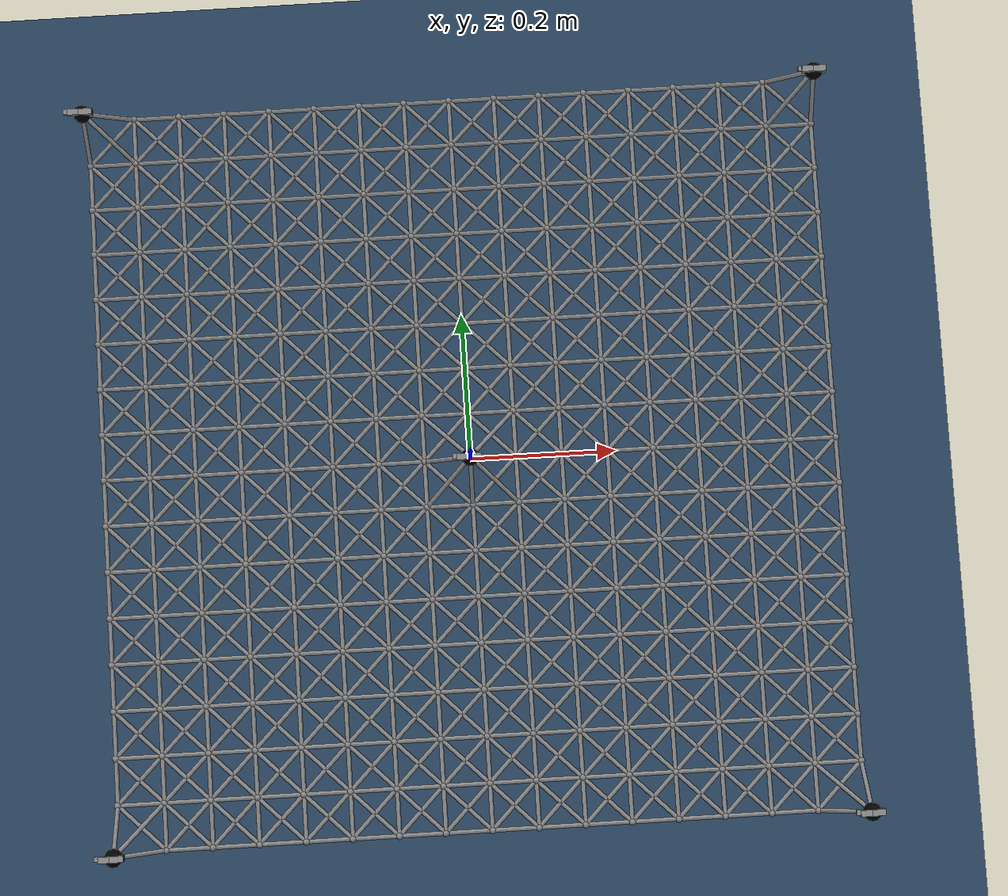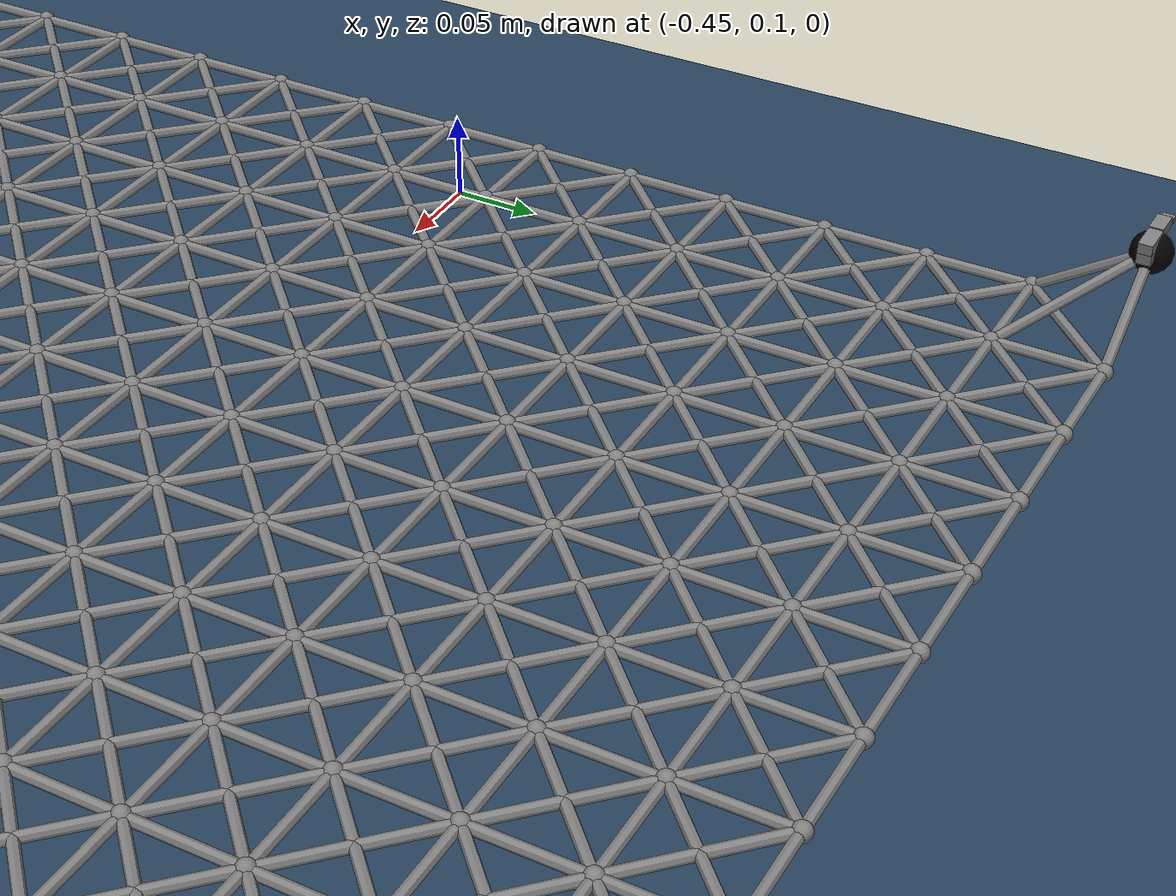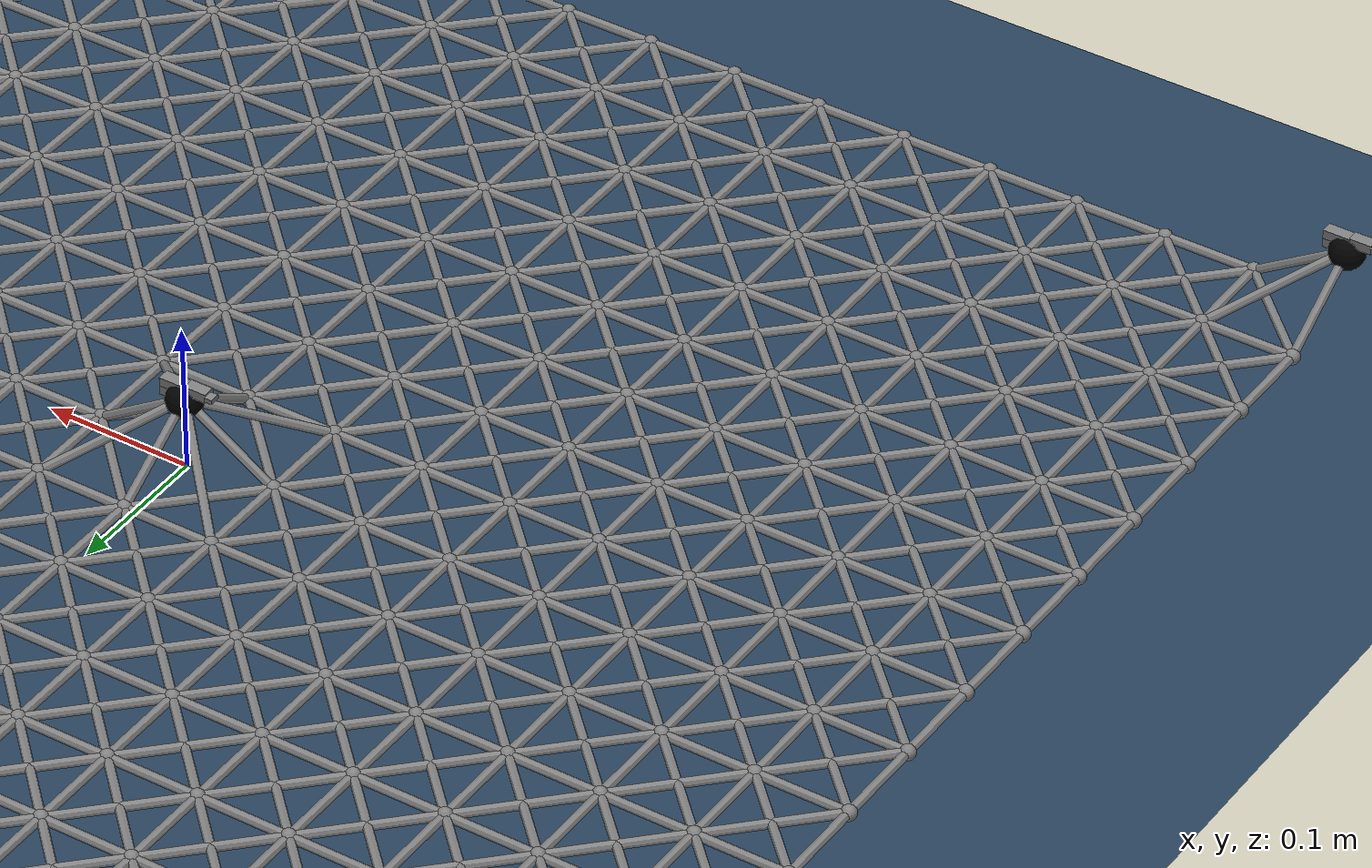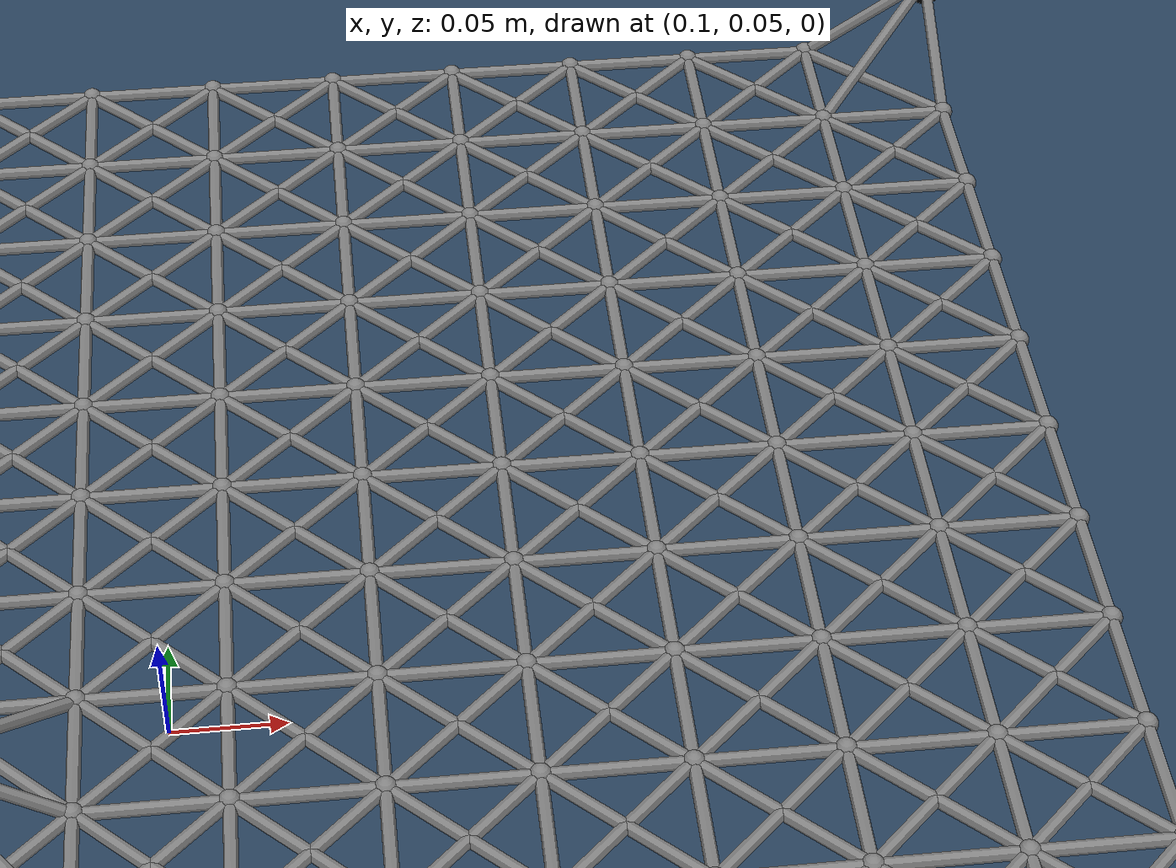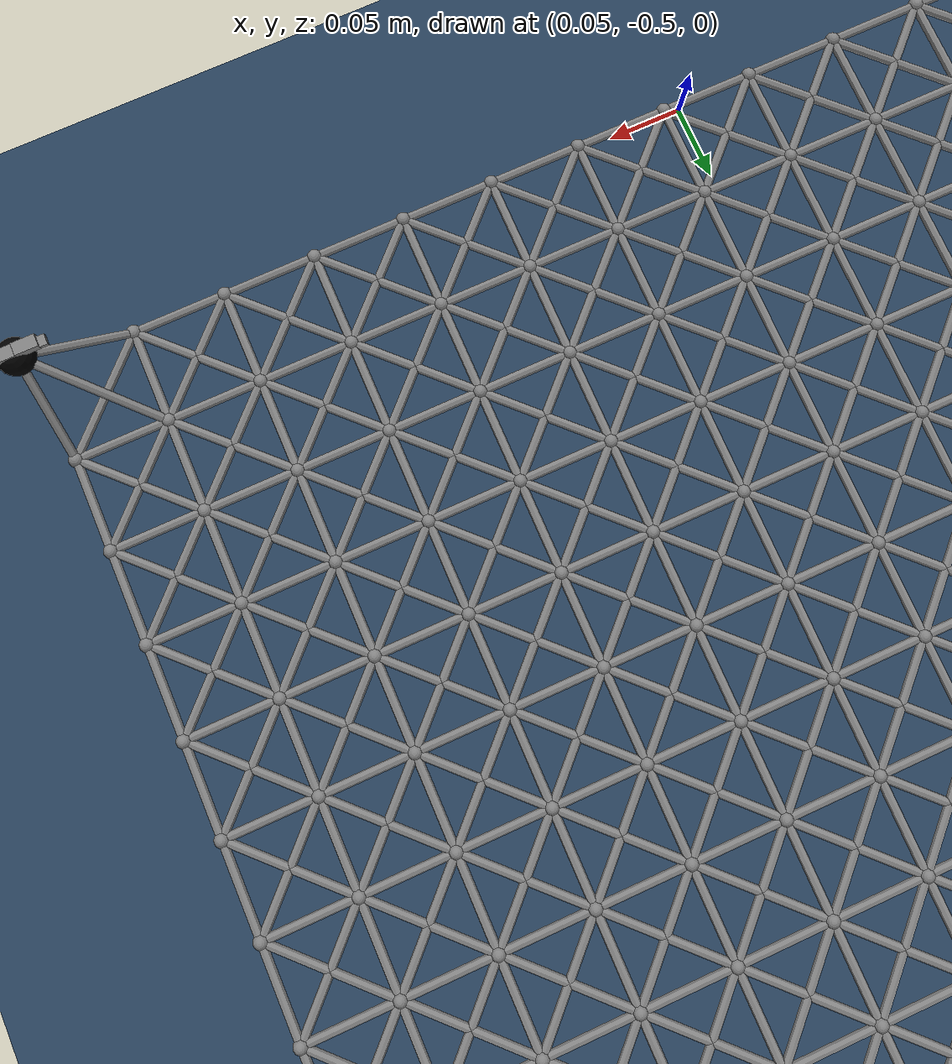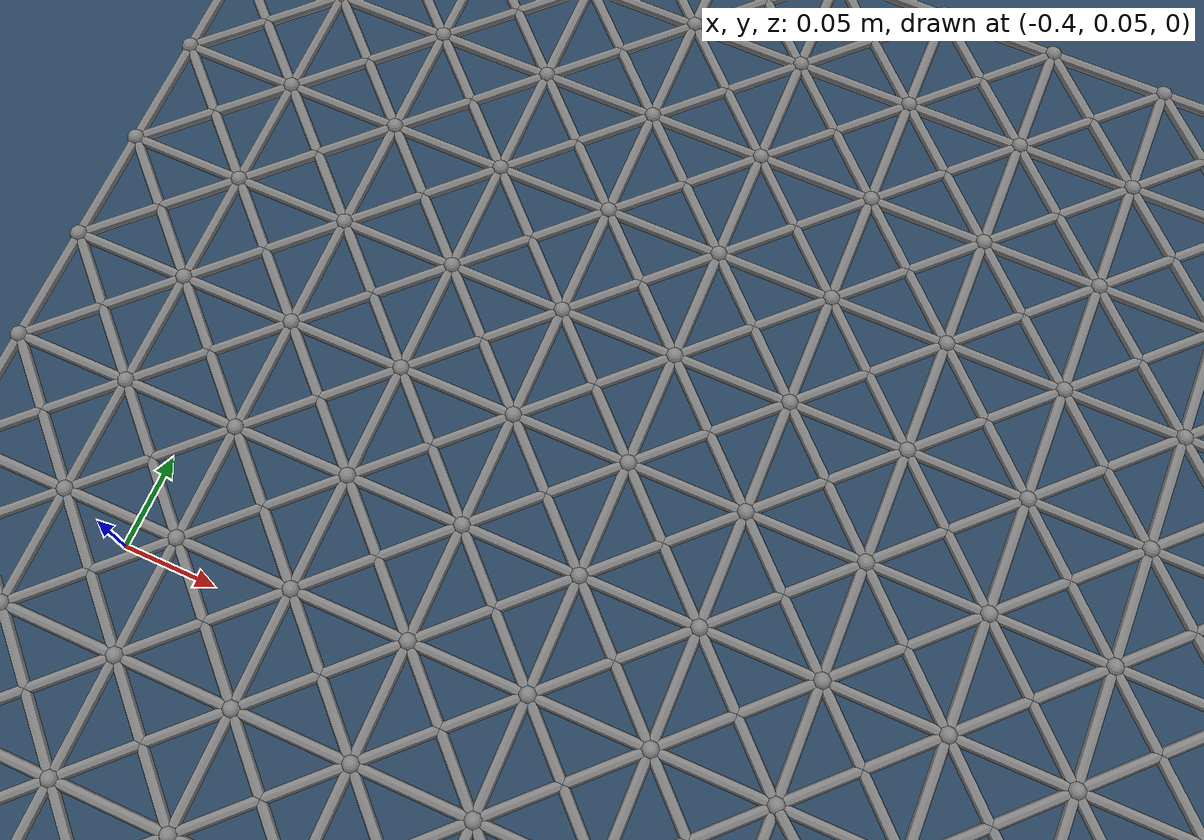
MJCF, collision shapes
<mujoco model="Skydio X2">
  <compiler angle="radian" meshdir="assets/" texturedir="assets/"/>

  <option timestep="0.005"/>

  <default>
    <default class="ball">
      <geom size="0.005 0 0"/>
    </default>
    <default class="x2">
      <site group="5"/>
      <general ctrlrange="0 13"/>
      <default class="visual">
        <geom type="mesh" contype="0" conaffinity="0" group="2"/>
      </default>
      <default class="collision">
        <geom type="box" group="3"/>
      </default>
    </default>
  </default>

  <asset>
    <texture type="2d" name="X2_lowpoly_texture_SpinningProps_1024" file="X2_lowpoly_texture_SpinningProps_1024.png"/>
    <texture type="skybox" builtin="gradient" rgb1="0.3 0.5 0.7" rgb2="0 0 0" width="512" height="3072"/>
    <texture type="2d" name="groundplane" builtin="checker" mark="edge" rgb1="0.2 0.3 0.4" rgb2="0.1 0.2 0.3" markrgb="0.8 0.8 0.8" width="300" height="300"/>
    <material name="phong3SG" texture="X2_lowpoly_texture_SpinningProps_1024"/>
    <material name="invisible" rgba="0 0 0 0"/>
    <material name="groundplane" texture="groundplane" texuniform="true" texrepeat="5 5" reflectance="0.2"/>
    <mesh name="X2_lowpoly" class="x2" file="X2_lowpoly.obj" scale="0.0015 0.0015 0.0015"/>
  </asset>

  <worldbody>
    <geom name="floor" size="0 0 0.05" type="plane" material="groundplane"/>
    <light pos="0 0 1.5" dir="0 0 -1" directional="true"/>
    <body name="quad_1" childclass="x2" pos="-0.5 -0.5 0.05">
      <joint type="free" limited="false" actuatorfrclimited="false" damping="0.05"/>
      <geom class="visual" pos="0.006 0 0.02" quat="0 0 0.707107 0.707107" mass="0" material="phong3SG" mesh="X2_lowpoly"/>
      <geom class="collision" size="0.009 0.00405 0.003" pos="0.006 0 0.003" mass="0"/>
      <geom class="collision" size="0.009 0.00405 0.003" pos="0.006 0 0.009" mass="0"/>
      <geom class="collision" size="0.0075 0.00405 0.003" pos="-0.0105 0 0.00975" mass="0"/>
      <geom class="collision" size="0.00345 0.00255 0.0015" pos="-0.02055 0.0012 0.00975" quat="0.707107 0 0 0.707107" mass="0"/>
      <geom name="point_mass_1" size="0.012" mass="0.04" material="invisible"/>
      <site name="ball_1_1" pos="0 0 0"/>
    </body>
    <body pos="-0.4375 -0.5 0.01">
      <joint type="free" limited="false" actuatorfrclimited="false" damping="0.001"/>
      <geom class="ball" mass="6.92042e-05"/>
      <site name="ball_1_2" pos="0 0 0"/>
    </body>
    <body pos="-0.375 -0.5 0.01">
      <joint type="free" limited="false" actuatorfrclimited="false" damping="0.001"/>
      <geom class="ball" mass="6.92042e-05"/>
      <site name="ball_1_3" pos="0 0 0"/>
    </body>
    <body pos="-0.3125 -0.5 0.01">
      <joint type="free" limited="false" actuatorfrclimited="false" damping="0.001"/>
      <geom class="ball" mass="6.92042e-05"/>
      <site name="ball_1_4" pos="0 0 0"/>
    </body>
    <body pos="-0.25 -0.5 0.01">
      <joint type="free" limited="false" actuatorfrclimited="false" damping="0.001"/>
      <geom class="ball" mass="6.92042e-05"/>
      <site name="ball_1_5" pos="0 0 0"/>
    </body>
    <body pos="-0.1875 -0.5 0.01">
      <joint type="free" limited="false" actuatorfrclimited="false" damping="0.001"/>
      <geom class="ball" mass="6.92042e-05"/>
      <site name="ball_1_6" pos="0 0 0"/>
    </body>
    <body pos="-0.125 -0.5 0.01">
      <joint type="free" limited="false" actuatorfrclimited="false" damping="0.001"/>
      <geom class="ball" mass="6.92042e-05"/>
      <site name="ball_1_7" pos="0 0 0"/>
    </body>
    <body pos="-0.0625 -0.5 0.01">
      <joint type="free" limited="false" actuatorfrclimited="false" damping="0.001"/>
      <geom class="ball" mass="6.92042e-05"/>
      <site name="ball_1_8" pos="0 0 0"/>
    </body>
    <body pos="0 -0.5 0.01">
      <joint type="free" limited="false" actuatorfrclimited="false" damping="0.001"/>
      <geom class="ball" mass="6.92042e-05"/>
      <site name="ball_1_9" pos="0 0 0"/>
    </body>
    <body pos="0.0625 -0.5 0.01">
      <joint type="free" limited="false" actuatorfrclimited="false" damping="0.001"/>
      <geom class="ball" mass="6.92042e-05"/>
      <site name="ball_1_10" pos="0 0 0"/>
    </body>
    <body pos="0.125 -0.5 0.01">
      <joint type="free" limited="false" actuatorfrclimited="false" damping="0.001"/>
      <geom class="ball" mass="6.92042e-05"/>
      <site name="ball_1_11" pos="0 0 0"/>
    </body>
    <body pos="0.1875 -0.5 0.01">
      <joint type="free" limited="false" actuatorfrclimited="false" damping="0.001"/>
      <geom class="ball" mass="6.92042e-05"/>
      <site name="ball_1_12" pos="0 0 0"/>
    </body>
    <body pos="0.25 -0.5 0.01">
      <joint type="free" limited="false" actuatorfrclimited="false" damping="0.001"/>
      <geom class="ball" mass="6.92042e-05"/>
      <site name="ball_1_13" pos="0 0 0"/>
    </body>
    <body pos="0.3125 -0.5 0.01">
      <joint type="free" limited="false" actuatorfrclimited="false" damping="0.001"/>
      <geom class="ball" mass="6.92042e-05"/>
      <site name="ball_1_14" pos="0 0 0"/>
    </body>
    <body pos="0.375 -0.5 0.01">
      <joint type="free" limited="false" actuatorfrclimited="false" damping="0.001"/>
      <geom class="ball" mass="6.92042e-05"/>
      <site name="ball_1_15" pos="0 0 0"/>
    </body>
    <body pos="0.4375 -0.5 0.01">
      <joint type="free" limited="false" actuatorfrclimited="false" damping="0.001"/>
      <geom class="ball" mass="6.92042e-05"/>
      <site name="ball_1_16" pos="0 0 0"/>
    </body>
    <body name="quad_2" childclass="x2" pos="0.5 -0.5 0.05">
      <joint type="free" limited="false" actuatorfrclimited="false" damping="0.05"/>
      <geom class="visual" pos="0.006 0 0.02" quat="0 0 0.707107 0.707107" mass="0" material="phong3SG" mesh="X2_lowpoly"/>
      <geom class="collision" size="0.009 0.00405 0.003" pos="0.006 0 0.003" mass="0"/>
      <geom class="collision" size="0.009 0.00405 0.003" pos="0.006 0 0.009" mass="0"/>
      <geom class="collision" size="0.0075 0.00405 0.003" pos="-0.0105 0 0.00975" mass="0"/>
      <geom class="collision" size="0.00345 0.00255 0.0015" pos="-0.02055 0.0012 0.00975" quat="0.707107 0 0 0.707107" mass="0"/>
      <geom name="point_mass_2" size="0.012" mass="0.04" material="invisible"/>
      <site name="ball_1_17" pos="0 0 0"/>
    </body>
    <body pos="-0.5 -0.4375 0.01">
      <joint type="free" limited="false" actuatorfrclimited="false" damping="0.001"/>
      <geom class="ball" mass="6.92042e-05"/>
      <site name="ball_2_1" pos="0 0 0"/>
    </body>
    <body pos="-0.4375 -0.4375 0.01">
      <joint type="free" limited="false" actuatorfrclimited="false" damping="0.001"/>
      <geom class="ball" mass="6.92042e-05"/>
      <site name="ball_2_2" pos="0 0 0"/>
    </body>
    <body pos="-0.375 -0.4375 0.01">
      <joint type="free" limited="false" actuatorfrclimited="false" damping="0.001"/>
      <geom class="ball" mass="6.92042e-05"/>
      <site name="ball_2_3" pos="0 0 0"/>
    </body>
    <body pos="-0.3125 -0.4375 0.01">
      <joint type="free" limited="false" actuatorfrclimited="false" damping="0.001"/>
      <geom class="ball" mass="6.92042e-05"/>
      <site name="ball_2_4" pos="0 0 0"/>
    </body>
    <body pos="-0.25 -0.4375 0.01">
      <joint type="free" limited="false" actuatorfrclimited="false" damping="0.001"/>
      <geom class="ball" mass="6.92042e-05"/>
      <site name="ball_2_5" pos="0 0 0"/>
    </body>
    <body pos="-0.1875 -0.4375 0.01">
      <joint type="free" limited="false" actuatorfrclimited="false" damping="0.001"/>
      <geom class="ball" mass="6.92042e-05"/>
      <site name="ball_2_6" pos="0 0 0"/>
    </body>
    <body pos="-0.125 -0.4375 0.01">
      <joint type="free" limited="false" actuatorfrclimited="false" damping="0.001"/>
      <geom class="ball" mass="6.92042e-05"/>
      <site name="ball_2_7" pos="0 0 0"/>
    </body>
    <body pos="-0.0625 -0.4375 0.01">
      <joint type="free" limited="false" actuatorfrclimited="false" damping="0.001"/>
      <geom class="ball" mass="6.92042e-05"/>
      <site name="ball_2_8" pos="0 0 0"/>
    </body>
    <body pos="0 -0.4375 0.01">
      <joint type="free" limited="false" actuatorfrclimited="false" damping="0.001"/>
      <geom class="ball" mass="6.92042e-05"/>
      <site name="ball_2_9" pos="0 0 0"/>
    </body>
    <body pos="0.0625 -0.4375 0.01">
      <joint type="free" limited="false" actuatorfrclimited="false" damping="0.001"/>
      <geom class="ball" mass="6.92042e-05"/>
      <site name="ball_2_10" pos="0 0 0"/>
    </body>
    <body pos="0.125 -0.4375 0.01">
      <joint type="free" limited="false" actuatorfrclimited="false" damping="0.001"/>
      <geom class="ball" mass="6.92042e-05"/>
      <site name="ball_2_11" pos="0 0 0"/>
    </body>
    <body pos="0.1875 -0.4375 0.01">
      <joint type="free" limited="false" actuatorfrclimited="false" damping="0.001"/>
      <geom class="ball" mass="6.92042e-05"/>
      <site name="ball_2_12" pos="0 0 0"/>
    </body>
    <body pos="0.25 -0.4375 0.01">
      <joint type="free" limited="false" actuatorfrclimited="false" damping="0.001"/>
      <geom class="ball" mass="6.92042e-05"/>
      <site name="ball_2_13" pos="0 0 0"/>
    </body>
    <body pos="0.3125 -0.4375 0.01">
      <joint type="free" limited="false" actuatorfrclimited="false" damping="0.001"/>
      <geom class="ball" mass="6.92042e-05"/>
      <site name="ball_2_14" pos="0 0 0"/>
    </body>
    <body pos="0.375 -0.4375 0.01">
      <joint type="free" limited="false" actuatorfrclimited="false" damping="0.001"/>
      <geom class="ball" mass="6.92042e-05"/>
      <site name="ball_2_15" pos="0 0 0"/>
    </body>
    <body pos="0.4375 -0.4375 0.01">
      <joint type="free" limited="false" actuatorfrclimited="false" damping="0.001"/>
      <geom class="ball" mass="6.92042e-05"/>
      <site name="ball_2_16" pos="0 0 0"/>
    </body>
    <body pos="0.5 -0.4375 0.01">
      <joint type="free" limited="false" actuatorfrclimited="false" damping="0.001"/>
      <geom class="ball" mass="6.92042e-05"/>
      <site name="ball_2_17" pos="0 0 0"/>
    </body>
    <body pos="-0.5 -0.375 0.01">
      <joint type="free" limited="false" actuatorfrclimited="false" damping="0.001"/>
      <geom class="ball" mass="6.92042e-05"/>
      <site name="ball_3_1" pos="0 0 0"/>
    </body>
    <body pos="-0.4375 -0.375 0.01">
      <joint type="free" limited="false" actuatorfrclimited="false" damping="0.001"/>
      <geom class="ball" mass="6.92042e-05"/>
      <site name="ball_3_2" pos="0 0 0"/>
    </body>
    <body pos="-0.375 -0.375 0.01">
      <joint type="free" limited="false" actuatorfrclimited="false" damping="0.001"/>
      <geom class="ball" mass="6.92042e-05"/>
      <site name="ball_3_3" pos="0 0 0"/>
    </body>
    <body pos="-0.3125 -0.375 0.01">
      <joint type="free" limited="false" actuatorfrclimited="false" damping="0.001"/>
      <geom class="ball" mass="6.92042e-05"/>
      <site name="ball_3_4" pos="0 0 0"/>
    </body>
    <body pos="-0.25 -0.375 0.01">
      <joint type="free" limited="false" actuatorfrclimited="false" damping="0.001"/>
      <geom class="ball" mass="6.92042e-05"/>
      <site name="ball_3_5" pos="0 0 0"/>
    </body>
    <body pos="-0.1875 -0.375 0.01">
      <joint type="free" limited="false" actuatorfrclimited="false" damping="0.001"/>
      <geom class="ball" mass="6.92042e-05"/>
      <site name="ball_3_6" pos="0 0 0"/>
    </body>
    <body pos="-0.125 -0.375 0.01">
      <joint type="free" limited="false" actuatorfrclimited="false" damping="0.001"/>
      <geom class="ball" mass="6.92042e-05"/>
      <site name="ball_3_7" pos="0 0 0"/>
    </body>
    <body pos="-0.0625 -0.375 0.01">
      <joint type="free" limited="false" actuatorfrclimited="false" damping="0.001"/>
      <geom class="ball" mass="6.92042e-05"/>
      <site name="ball_3_8" pos="0 0 0"/>
    </body>
    <body pos="0 -0.375 0.01">
      <joint type="free" limited="false" actuatorfrclimited="false" damping="0.001"/>
      <geom class="ball" mass="6.92042e-05"/>
      <site name="ball_3_9" pos="0 0 0"/>
    </body>
    <body pos="0.0625 -0.375 0.01">
      <joint type="free" limited="false" actuatorfrclimited="false" damping="0.001"/>
      <geom class="ball" mass="6.92042e-05"/>
      <site name="ball_3_10" pos="0 0 0"/>
    </body>
    <body pos="0.125 -0.375 0.01">
      <joint type="free" limited="false" actuatorfrclimited="false" damping="0.001"/>
      <geom class="ball" mass="6.92042e-05"/>
      <site name="ball_3_11" pos="0 0 0"/>
    </body>
    <body pos="0.1875 -0.375 0.01">
      <joint type="free" limited="false" actuatorfrclimited="false" damping="0.001"/>
      <geom class="ball" mass="6.92042e-05"/>
      <site name="ball_3_12" pos="0 0 0"/>
    </body>
    <body pos="0.25 -0.375 0.01">
      <joint type="free" limited="false" actuatorfrclimited="false" damping="0.001"/>
      <geom class="ball" mass="6.92042e-05"/>
      <site name="ball_3_13" pos="0 0 0"/>
    </body>
    <body pos="0.3125 -0.375 0.01">
      <joint type="free" limited="false" actuatorfrclimited="false" damping="0.001"/>
      <geom class="ball" mass="6.92042e-05"/>
      <site name="ball_3_14" pos="0 0 0"/>
    </body>
    <body pos="0.375 -0.375 0.01">
      <joint type="free" limited="false" actuatorfrclimited="false" damping="0.001"/>
      <geom class="ball" mass="6.92042e-05"/>
      <site name="ball_3_15" pos="0 0 0"/>
    </body>
    <body pos="0.4375 -0.375 0.01">
      <joint type="free" limited="false" actuatorfrclimited="false" damping="0.001"/>
      <geom class="ball" mass="6.92042e-05"/>
      <site name="ball_3_16" pos="0 0 0"/>
    </body>
    <body pos="0.5 -0.375 0.01">
      <joint type="free" limited="false" actuatorfrclimited="false" damping="0.001"/>
      <geom class="ball" mass="6.92042e-05"/>
      <site name="ball_3_17" pos="0 0 0"/>
    </body>
    <body pos="-0.5 -0.3125 0.01">
      <joint type="free" limited="false" actuatorfrclimited="false" damping="0.001"/>
      <geom class="ball" mass="6.92042e-05"/>
      <site name="ball_4_1" pos="0 0 0"/>
    </body>
    <body pos="-0.4375 -0.3125 0.01">
      <joint type="free" limited="false" actuatorfrclimited="false" damping="0.001"/>
      <geom class="ball" mass="6.92042e-05"/>
      <site name="ball_4_2" pos="0 0 0"/>
    </body>
    <body pos="-0.375 -0.3125 0.01">
      <joint type="free" limited="false" actuatorfrclimited="false" damping="0.001"/>
      <geom class="ball" mass="6.92042e-05"/>
      <site name="ball_4_3" pos="0 0 0"/>
    </body>
    <body pos="-0.3125 -0.3125 0.01">
      <joint type="free" limited="false" actuatorfrclimited="false" damping="0.001"/>
      <geom class="ball" mass="6.92042e-05"/>
      <site name="ball_4_4" pos="0 0 0"/>
    </body>
    <body pos="-0.25 -0.3125 0.01">
      <joint type="free" limited="false" actuatorfrclimited="false" damping="0.001"/>
      <geom class="ball" mass="6.92042e-05"/>
      <site name="ball_4_5" pos="0 0 0"/>
    </body>
    <body pos="-0.1875 -0.3125 0.01">
      <joint type="free" limited="false" actuatorfrclimited="false" damping="0.001"/>
      <geom class="ball" mass="6.92042e-05"/>
      <site name="ball_4_6" pos="0 0 0"/>
    </body>
    <body pos="-0.125 -0.3125 0.01">
      <joint type="free" limited="false" actuatorfrclimited="false" damping="0.001"/>
      <geom class="ball" mass="6.92042e-05"/>
      <site name="ball_4_7" pos="0 0 0"/>
    </body>
    <body pos="-0.0625 -0.3125 0.01">
      <joint type="free" limited="false" actuatorfrclimited="false" damping="0.001"/>
      <geom class="ball" mass="6.92042e-05"/>
      <site name="ball_4_8" pos="0 0 0"/>
    </body>
    <body pos="0 -0.3125 0.01">
      <joint type="free" limited="false" actuatorfrclimited="false" damping="0.001"/>
      <geom class="ball" mass="6.92042e-05"/>
      <site name="ball_4_9" pos="0 0 0"/>
    </body>
    <body pos="0.0625 -0.3125 0.01">
      <joint type="free" limited="false" actuatorfrclimited="false" damping="0.001"/>
      <geom class="ball" mass="6.92042e-05"/>
      <site name="ball_4_10" pos="0 0 0"/>
    </body>
    <body pos="0.125 -0.3125 0.01">
      <joint type="free" limited="false" actuatorfrclimited="false" damping="0.001"/>
      <geom class="ball" mass="6.92042e-05"/>
      <site name="ball_4_11" pos="0 0 0"/>
    </body>
    <body pos="0.1875 -0.3125 0.01">
      <joint type="free" limited="false" actuatorfrclimited="false" damping="0.001"/>
      <geom class="ball" mass="6.92042e-05"/>
      <site name="ball_4_12" pos="0 0 0"/>
    </body>
    <body pos="0.25 -0.3125 0.01">
      <joint type="free" limited="false" actuatorfrclimited="false" damping="0.001"/>
      <geom class="ball" mass="6.92042e-05"/>
      <site name="ball_4_13" pos="0 0 0"/>
    </body>
    <body pos="0.3125 -0.3125 0.01">
      <joint type="free" limited="false" actuatorfrclimited="false" damping="0.001"/>
      <geom class="ball" mass="6.92042e-05"/>
      <site name="ball_4_14" pos="0 0 0"/>
    </body>
    <body pos="0.375 -0.3125 0.01">
      <joint type="free" limited="false" actuatorfrclimited="false" damping="0.001"/>
      <geom class="ball" mass="6.92042e-05"/>
      <site name="ball_4_15" pos="0 0 0"/>
    </body>
    <body pos="0.4375 -0.3125 0.01">
      <joint type="free" limited="false" actuatorfrclimited="false" damping="0.001"/>
      <geom class="ball" mass="6.92042e-05"/>
      <site name="ball_4_16" pos="0 0 0"/>
    </body>
    <body pos="0.5 -0.3125 0.01">
      <joint type="free" limited="false" actuatorfrclimited="false" damping="0.001"/>
      <geom class="ball" mass="6.92042e-05"/>
      <site name="ball_4_17" pos="0 0 0"/>
    </body>
    <body pos="-0.5 -0.25 0.01">
      <joint type="free" limited="false" actuatorfrclimited="false" damping="0.001"/>
      <geom class="ball" mass="6.92042e-05"/>
      <site name="ball_5_1" pos="0 0 0"/>
    </body>
    <body pos="-0.4375 -0.25 0.01">
      <joint type="free" limited="false" actuatorfrclimited="false" damping="0.001"/>
      <geom class="ball" mass="6.92042e-05"/>
      <site name="ball_5_2" pos="0 0 0"/>
    </body>
    <body pos="-0.375 -0.25 0.01">
      <joint type="free" limited="false" actuatorfrclimited="false" damping="0.001"/>
      <geom class="ball" mass="6.92042e-05"/>
      <site name="ball_5_3" pos="0 0 0"/>
    </body>
    <body pos="-0.3125 -0.25 0.01">
      <joint type="free" limited="false" actuatorfrclimited="false" damping="0.001"/>
      <geom class="ball" mass="6.92042e-05"/>
      <site name="ball_5_4" pos="0 0 0"/>
    </body>
    <body pos="-0.25 -0.25 0.01">
      <joint type="free" limited="false" actuatorfrclimited="false" damping="0.001"/>
      <geom class="ball" mass="6.92042e-05"/>
      <site name="ball_5_5" pos="0 0 0"/>
    </body>
    <body pos="-0.1875 -0.25 0.01">
      <joint type="free" limited="false" actuatorfrclimited="false" damping="0.001"/>
      <geom class="ball" mass="6.92042e-05"/>
      <site name="ball_5_6" pos="0 0 0"/>
    </body>
    <body pos="-0.125 -0.25 0.01">
      <joint type="free" limited="false" actuatorfrclimited="false" damping="0.001"/>
      <geom class="ball" mass="6.92042e-05"/>
      <site name="ball_5_7" pos="0 0 0"/>
    </body>
    <body pos="-0.0625 -0.25 0.01">
      <joint type="free" limited="false" actuatorfrclimited="false" damping="0.001"/>
      <geom class="ball" mass="6.92042e-05"/>
      <site name="ball_5_8" pos="0 0 0"/>
    </body>
    <body pos="0 -0.25 0.01">
      <joint type="free" limited="false" actuatorfrclimited="false" damping="0.001"/>
      <geom class="ball" mass="6.92042e-05"/>
      <site name="ball_5_9" pos="0 0 0"/>
    </body>
    <body pos="0.0625 -0.25 0.01">
      <joint type="free" limited="false" actuatorfrclimited="false" damping="0.001"/>
      <geom class="ball" mass="6.92042e-05"/>
      <site name="ball_5_10" pos="0 0 0"/>
    </body>
    <body pos="0.125 -0.25 0.01">
      <joint type="free" limited="false" actuatorfrclimited="false" damping="0.001"/>
      <geom class="ball" mass="6.92042e-05"/>
      <site name="ball_5_11" pos="0 0 0"/>
    </body>
    <body pos="0.1875 -0.25 0.01">
      <joint type="free" limited="false" actuatorfrclimited="false" damping="0.001"/>
      <geom class="ball" mass="6.92042e-05"/>
      <site name="ball_5_12" pos="0 0 0"/>
    </body>
    <body pos="0.25 -0.25 0.01">
      <joint type="free" limited="false" actuatorfrclimited="false" damping="0.001"/>
      <geom class="ball" mass="6.92042e-05"/>
      <site name="ball_5_13" pos="0 0 0"/>
    </body>
    <body pos="0.3125 -0.25 0.01">
      <joint type="free" limited="false" actuatorfrclimited="false" damping="0.001"/>
      <geom class="ball" mass="6.92042e-05"/>
      <site name="ball_5_14" pos="0 0 0"/>
    </body>
    <body pos="0.375 -0.25 0.01">
      <joint type="free" limited="false" actuatorfrclimited="false" damping="0.001"/>
      <geom class="ball" mass="6.92042e-05"/>
      <site name="ball_5_15" pos="0 0 0"/>
    </body>
    <body pos="0.4375 -0.25 0.01">
      <joint type="free" limited="false" actuatorfrclimited="false" damping="0.001"/>
      <geom class="ball" mass="6.92042e-05"/>
      <site name="ball_5_16" pos="0 0 0"/>
    </body>
    <body pos="0.5 -0.25 0.01">
      <joint type="free" limited="false" actuatorfrclimited="false" damping="0.001"/>
      <geom class="ball" mass="6.92042e-05"/>
      <site name="ball_5_17" pos="0 0 0"/>
    </body>
    <body pos="-0.5 -0.1875 0.01">
      <joint type="free" limited="false" actuatorfrclimited="false" damping="0.001"/>
      <geom class="ball" mass="6.92042e-05"/>
      <site name="ball_6_1" pos="0 0 0"/>
    </body>
    <body pos="-0.4375 -0.1875 0.01">
      <joint type="free" limited="false" actuatorfrclimited="false" damping="0.001"/>
      <geom class="ball" mass="6.92042e-05"/>
      <site name="ball_6_2" pos="0 0 0"/>
    </body>
    <body pos="-0.375 -0.1875 0.01">
      <joint type="free" limited="false" actuatorfrclimited="false" damping="0.001"/>
      <geom class="ball" mass="6.92042e-05"/>
      <site name="ball_6_3" pos="0 0 0"/>
    </body>
    <body pos="-0.3125 -0.1875 0.01">
      <joint type="free" limited="false" actuatorfrclimited="false" damping="0.001"/>
      <geom class="ball" mass="6.92042e-05"/>
      <site name="ball_6_4" pos="0 0 0"/>
    </body>
    <body pos="-0.25 -0.1875 0.01">
      <joint type="free" limited="false" actuatorfrclimited="false" damping="0.001"/>
      <geom class="ball" mass="6.92042e-05"/>
      <site name="ball_6_5" pos="0 0 0"/>
    </body>
    <body pos="-0.1875 -0.1875 0.01">
      <joint type="free" limited="false" actuatorfrclimited="false" damping="0.001"/>
      <geom class="ball" mass="6.92042e-05"/>
      <site name="ball_6_6" pos="0 0 0"/>
    </body>
    <body pos="-0.125 -0.1875 0.01">
      <joint type="free" limited="false" actuatorfrclimited="false" damping="0.001"/>
      <geom class="ball" mass="6.92042e-05"/>
      <site name="ball_6_7" pos="0 0 0"/>
    </body>
    <body pos="-0.0625 -0.1875 0.01">
      <joint type="free" limited="false" actuatorfrclimited="false" damping="0.001"/>
      <geom class="ball" mass="6.92042e-05"/>
      <site name="ball_6_8" pos="0 0 0"/>
    </body>
    <body pos="0 -0.1875 0.01">
      <joint type="free" limited="false" actuatorfrclimited="false" damping="0.001"/>
      <geom class="ball" mass="6.92042e-05"/>
      <site name="ball_6_9" pos="0 0 0"/>
    </body>
    <body pos="0.0625 -0.1875 0.01">
      <joint type="free" limited="false" actuatorfrclimited="false" damping="0.001"/>
      <geom class="ball" mass="6.92042e-05"/>
      <site name="ball_6_10" pos="0 0 0"/>
    </body>
    <body pos="0.125 -0.1875 0.01">
      <joint type="free" limited="false" actuatorfrclimited="false" damping="0.001"/>
      <geom class="ball" mass="6.92042e-05"/>
      <site name="ball_6_11" pos="0 0 0"/>
    </body>
    <body pos="0.1875 -0.1875 0.01">
      <joint type="free" limited="false" actuatorfrclimited="false" damping="0.001"/>
      <geom class="ball" mass="6.92042e-05"/>
      <site name="ball_6_12" pos="0 0 0"/>
    </body>
    <body pos="0.25 -0.1875 0.01">
      <joint type="free" limited="false" actuatorfrclimited="false" damping="0.001"/>
      <geom class="ball" mass="6.92042e-05"/>
      <site name="ball_6_13" pos="0 0 0"/>
    </body>
    <body pos="0.3125 -0.1875 0.01">
      <joint type="free" limited="false" actuatorfrclimited="false" damping="0.001"/>
      <geom class="ball" mass="6.92042e-05"/>
      <site name="ball_6_14" pos="0 0 0"/>
    </body>
    <body pos="0.375 -0.1875 0.01">
      <joint type="free" limited="false" actuatorfrclimited="false" damping="0.001"/>
      <geom class="ball" mass="6.92042e-05"/>
      <site name="ball_6_15" pos="0 0 0"/>
    </body>
    <body pos="0.4375 -0.1875 0.01">
      <joint type="free" limited="false" actuatorfrclimited="false" damping="0.001"/>
      <geom class="ball" mass="6.92042e-05"/>
      <site name="ball_6_16" pos="0 0 0"/>
    </body>
    <body pos="0.5 -0.1875 0.01">
      <joint type="free" limited="false" actuatorfrclimited="false" damping="0.001"/>
      <geom class="ball" mass="6.92042e-05"/>
      <site name="ball_6_17" pos="0 0 0"/>
    </body>
    <body pos="-0.5 -0.125 0.01">
      <joint type="free" limited="false" actuatorfrclimited="false" damping="0.001"/>
      <geom class="ball" mass="6.92042e-05"/>
      <site name="ball_7_1" pos="0 0 0"/>
    </body>
    <body pos="-0.4375 -0.125 0.01">
      <joint type="free" limited="false" actuatorfrclimited="false" damping="0.001"/>
      <geom class="ball" mass="6.92042e-05"/>
      <site name="ball_7_2" pos="0 0 0"/>
    </body>
    <body pos="-0.375 -0.125 0.01">
      <joint type="free" limited="false" actuatorfrclimited="false" damping="0.001"/>
      <geom class="ball" mass="6.92042e-05"/>
      <site name="ball_7_3" pos="0 0 0"/>
    </body>
    <body pos="-0.3125 -0.125 0.01">
      <joint type="free" limited="false" actuatorfrclimited="false" damping="0.001"/>
      <geom class="ball" mass="6.92042e-05"/>
      <site name="ball_7_4" pos="0 0 0"/>
    </body>
    <body pos="-0.25 -0.125 0.01">
      <joint type="free" limited="false" actuatorfrclimited="false" damping="0.001"/>
      <geom class="ball" mass="6.92042e-05"/>
      <site name="ball_7_5" pos="0 0 0"/>
    </body>
    <body pos="-0.1875 -0.125 0.01">
      <joint type="free" limited="false" actuatorfrclimited="false" damping="0.001"/>
      <geom class="ball" mass="6.92042e-05"/>
      <site name="ball_7_6" pos="0 0 0"/>
    </body>
    <body pos="-0.125 -0.125 0.01">
      <joint type="free" limited="false" actuatorfrclimited="false" damping="0.001"/>
      <geom class="ball" mass="6.92042e-05"/>
      <site name="ball_7_7" pos="0 0 0"/>
    </body>
    <body pos="-0.0625 -0.125 0.01">
      <joint type="free" limited="false" actuatorfrclimited="false" damping="0.001"/>
      <geom class="ball" mass="6.92042e-05"/>
      <site name="ball_7_8" pos="0 0 0"/>
    </body>
    <body pos="0 -0.125 0.01">
      <joint type="free" limited="false" actuatorfrclimited="false" damping="0.001"/>
      <geom class="ball" mass="6.92042e-05"/>
      <site name="ball_7_9" pos="0 0 0"/>
    </body>
    <body pos="0.0625 -0.125 0.01">
      <joint type="free" limited="false" actuatorfrclimited="false" damping="0.001"/>
      <geom class="ball" mass="6.92042e-05"/>
      <site name="ball_7_10" pos="0 0 0"/>
    </body>
    <body pos="0.125 -0.125 0.01">
      <joint type="free" limited="false" actuatorfrclimited="false" damping="0.001"/>
      <geom class="ball" mass="6.92042e-05"/>
      <site name="ball_7_11" pos="0 0 0"/>
    </body>
    <body pos="0.1875 -0.125 0.01">
      <joint type="free" limited="false" actuatorfrclimited="false" damping="0.001"/>
      <geom class="ball" mass="6.92042e-05"/>
      <site name="ball_7_12" pos="0 0 0"/>
    </body>
    <body pos="0.25 -0.125 0.01">
      <joint type="free" limited="false" actuatorfrclimited="false" damping="0.001"/>
      <geom class="ball" mass="6.92042e-05"/>
      <site name="ball_7_13" pos="0 0 0"/>
    </body>
    <body pos="0.3125 -0.125 0.01">
      <joint type="free" limited="false" actuatorfrclimited="false" damping="0.001"/>
      <geom class="ball" mass="6.92042e-05"/>
      <site name="ball_7_14" pos="0 0 0"/>
    </body>
    <body pos="0.375 -0.125 0.01">
      <joint type="free" limited="false" actuatorfrclimited="false" damping="0.001"/>
      <geom class="ball" mass="6.92042e-05"/>
      <site name="ball_7_15" pos="0 0 0"/>
    </body>
    <body pos="0.4375 -0.125 0.01">
      <joint type="free" limited="false" actuatorfrclimited="false" damping="0.001"/>
      <geom class="ball" mass="6.92042e-05"/>
      <site name="ball_7_16" pos="0 0 0"/>
    </body>
    <body pos="0.5 -0.125 0.01">
      <joint type="free" limited="false" actuatorfrclimited="false" damping="0.001"/>
      <geom class="ball" mass="6.92042e-05"/>
      <site name="ball_7_17" pos="0 0 0"/>
    </body>
    <body pos="-0.5 -0.0625 0.01">
      <joint type="free" limited="false" actuatorfrclimited="false" damping="0.001"/>
      <geom class="ball" mass="6.92042e-05"/>
      <site name="ball_8_1" pos="0 0 0"/>
    </body>
    <body pos="-0.4375 -0.0625 0.01">
      <joint type="free" limited="false" actuatorfrclimited="false" damping="0.001"/>
      <geom class="ball" mass="6.92042e-05"/>
      <site name="ball_8_2" pos="0 0 0"/>
    </body>
    <body pos="-0.375 -0.0625 0.01">
      <joint type="free" limited="false" actuatorfrclimited="false" damping="0.001"/>
      <geom class="ball" mass="6.92042e-05"/>
      <site name="ball_8_3" pos="0 0 0"/>
    </body>
    <body pos="-0.3125 -0.0625 0.01">
      <joint type="free" limited="false" actuatorfrclimited="false" damping="0.001"/>
      <geom class="ball" mass="6.92042e-05"/>
      <site name="ball_8_4" pos="0 0 0"/>
    </body>
    <body pos="-0.25 -0.0625 0.01">
      <joint type="free" limited="false" actuatorfrclimited="false" damping="0.001"/>
      <geom class="ball" mass="6.92042e-05"/>
      <site name="ball_8_5" pos="0 0 0"/>
    </body>
    <body pos="-0.1875 -0.0625 0.01">
      <joint type="free" limited="false" actuatorfrclimited="false" damping="0.001"/>
      <geom class="ball" mass="6.92042e-05"/>
      <site name="ball_8_6" pos="0 0 0"/>
    </body>
    <body pos="-0.125 -0.0625 0.01">
      <joint type="free" limited="false" actuatorfrclimited="false" damping="0.001"/>
      <geom class="ball" mass="6.92042e-05"/>
      <site name="ball_8_7" pos="0 0 0"/>
    </body>
    <body pos="-0.0625 -0.0625 0.01">
      <joint type="free" limited="false" actuatorfrclimited="false" damping="0.001"/>
      <geom class="ball" mass="6.92042e-05"/>
      <site name="ball_8_8" pos="0 0 0"/>
    </body>
    <body pos="0 -0.0625 0.01">
      <joint type="free" limited="false" actuatorfrclimited="false" damping="0.001"/>
      <geom class="ball" mass="6.92042e-05"/>
      <site name="ball_8_9" pos="0 0 0"/>
    </body>
    <body pos="0.0625 -0.0625 0.01">
      <joint type="free" limited="false" actuatorfrclimited="false" damping="0.001"/>
      <geom class="ball" mass="6.92042e-05"/>
      <site name="ball_8_10" pos="0 0 0"/>
    </body>
    <body pos="0.125 -0.0625 0.01">
      <joint type="free" limited="false" actuatorfrclimited="false" damping="0.001"/>
      <geom class="ball" mass="6.92042e-05"/>
      <site name="ball_8_11" pos="0 0 0"/>
    </body>
    <body pos="0.1875 -0.0625 0.01">
      <joint type="free" limited="false" actuatorfrclimited="false" damping="0.001"/>
      <geom class="ball" mass="6.92042e-05"/>
      <site name="ball_8_12" pos="0 0 0"/>
    </body>
    <body pos="0.25 -0.0625 0.01">
      <joint type="free" limited="false" actuatorfrclimited="false" damping="0.001"/>
      <geom class="ball" mass="6.92042e-05"/>
      <site name="ball_8_13" pos="0 0 0"/>
    </body>
    <body pos="0.3125 -0.0625 0.01">
      <joint type="free" limited="false" actuatorfrclimited="false" damping="0.001"/>
      <geom class="ball" mass="6.92042e-05"/>
      <site name="ball_8_14" pos="0 0 0"/>
    </body>
    <body pos="0.375 -0.0625 0.01">
      <joint type="free" limited="false" actuatorfrclimited="false" damping="0.001"/>
      <geom class="ball" mass="6.92042e-05"/>
      <site name="ball_8_15" pos="0 0 0"/>
    </body>
    <body pos="0.4375 -0.0625 0.01">
      <joint type="free" limited="false" actuatorfrclimited="false" damping="0.001"/>
      <geom class="ball" mass="6.92042e-05"/>
      <site name="ball_8_16" pos="0 0 0"/>
    </body>
    <body pos="0.5 -0.0625 0.01">
      <joint type="free" limited="false" actuatorfrclimited="false" damping="0.001"/>
      <geom class="ball" mass="6.92042e-05"/>
      <site name="ball_8_17" pos="0 0 0"/>
    </body>
    <body pos="-0.5 0 0.01">
      <joint type="free" limited="false" actuatorfrclimited="false" damping="0.001"/>
      <geom class="ball" mass="6.92042e-05"/>
      <site name="ball_9_1" pos="0 0 0"/>
    </body>
    <body pos="-0.4375 0 0.01">
      <joint type="free" limited="false" actuatorfrclimited="false" damping="0.001"/>
      <geom class="ball" mass="6.92042e-05"/>
      <site name="ball_9_2" pos="0 0 0"/>
    </body>
    <body pos="-0.375 0 0.01">
      <joint type="free" limited="false" actuatorfrclimited="false" damping="0.001"/>
      <geom class="ball" mass="6.92042e-05"/>
      <site name="ball_9_3" pos="0 0 0"/>
    </body>
    <body pos="-0.3125 0 0.01">
      <joint type="free" limited="false" actuatorfrclimited="false" damping="0.001"/>
      <geom class="ball" mass="6.92042e-05"/>
      <site name="ball_9_4" pos="0 0 0"/>
    </body>
    <body pos="-0.25 0 0.01">
      <joint type="free" limited="false" actuatorfrclimited="false" damping="0.001"/>
      <geom class="ball" mass="6.92042e-05"/>
      <site name="ball_9_5" pos="0 0 0"/>
    </body>
    <body pos="-0.1875 0 0.01">
      <joint type="free" limited="false" actuatorfrclimited="false" damping="0.001"/>
      <geom class="ball" mass="6.92042e-05"/>
      <site name="ball_9_6" pos="0 0 0"/>
    </body>
    <body pos="-0.125 0 0.01">
      <joint type="free" limited="false" actuatorfrclimited="false" damping="0.001"/>
      <geom class="ball" mass="6.92042e-05"/>
      <site name="ball_9_7" pos="0 0 0"/>
    </body>
    <body pos="-0.0625 0 0.01">
      <joint type="free" limited="false" actuatorfrclimited="false" damping="0.001"/>
      <geom class="ball" mass="6.92042e-05"/>
      <site name="ball_9_8" pos="0 0 0"/>
    </body>
    <body name="quad_3" childclass="x2" pos="0 0 0.05">
      <joint type="free" limited="false" actuatorfrclimited="false" damping="0.05"/>
      <geom class="visual" pos="0.006 0 0.02" quat="0 0 0.707107 0.707107" mass="0" material="phong3SG" mesh="X2_lowpoly"/>
      <geom class="collision" size="0.009 0.00405 0.003" pos="0.006 0 0.003" mass="0"/>
      <geom class="collision" size="0.009 0.00405 0.003" pos="0.006 0 0.009" mass="0"/>
      <geom class="collision" size="0.0075 0.00405 0.003" pos="-0.0105 0 0.00975" mass="0"/>
      <geom class="collision" size="0.00345 0.00255 0.0015" pos="-0.02055 0.0012 0.00975" quat="0.707107 0 0 0.707107" mass="0"/>
      <geom name="point_mass_3" size="0.012" mass="0.04" material="invisible"/>
      <site name="ball_9_9" pos="0 0 0"/>
    </body>
    <body pos="0.0625 0 0.01">
      <joint type="free" limited="false" actuatorfrclimited="false" damping="0.001"/>
      <geom class="ball" mass="6.92042e-05"/>
      <site name="ball_9_10" pos="0 0 0"/>
    </body>
    <body pos="0.125 0 0.01">
      <joint type="free" limited="false" actuatorfrclimited="false" damping="0.001"/>
      <geom class="ball" mass="6.92042e-05"/>
      <site name="ball_9_11" pos="0 0 0"/>
    </body>
    <body pos="0.1875 0 0.01">
      <joint type="free" limited="false" actuatorfrclimited="false" damping="0.001"/>
      <geom class="ball" mass="6.92042e-05"/>
      <site name="ball_9_12" pos="0 0 0"/>
    </body>
    <body pos="0.25 0 0.01">
      <joint type="free" limited="false" actuatorfrclimited="false" damping="0.001"/>
      <geom class="ball" mass="6.92042e-05"/>
      <site name="ball_9_13" pos="0 0 0"/>
    </body>
    <body pos="0.3125 0 0.01">
      <joint type="free" limited="false" actuatorfrclimited="false" damping="0.001"/>
      <geom class="ball" mass="6.92042e-05"/>
      <site name="ball_9_14" pos="0 0 0"/>
    </body>
    <body pos="0.375 0 0.01">
      <joint type="free" limited="false" actuatorfrclimited="false" damping="0.001"/>
      <geom class="ball" mass="6.92042e-05"/>
      <site name="ball_9_15" pos="0 0 0"/>
    </body>
    <body pos="0.4375 0 0.01">
      <joint type="free" limited="false" actuatorfrclimited="false" damping="0.001"/>
      <geom class="ball" mass="6.92042e-05"/>
      <site name="ball_9_16" pos="0 0 0"/>
    </body>
    <body pos="0.5 0 0.01">
      <joint type="free" limited="false" actuatorfrclimited="false" damping="0.001"/>
      <geom class="ball" mass="6.92042e-05"/>
      <site name="ball_9_17" pos="0 0 0"/>
    </body>
    <body pos="-0.5 0.0625 0.01">
      <joint type="free" limited="false" actuatorfrclimited="false" damping="0.001"/>
      <geom class="ball" mass="6.92042e-05"/>
      <site name="ball_10_1" pos="0 0 0"/>
    </body>
    <body pos="-0.4375 0.0625 0.01">
      <joint type="free" limited="false" actuatorfrclimited="false" damping="0.001"/>
      <geom class="ball" mass="6.92042e-05"/>
      <site name="ball_10_2" pos="0 0 0"/>
    </body>
    <body pos="-0.375 0.0625 0.01">
      <joint type="free" limited="false" actuatorfrclimited="false" damping="0.001"/>
      <geom class="ball" mass="6.92042e-05"/>
      <site name="ball_10_3" pos="0 0 0"/>
    </body>
    <body pos="-0.3125 0.0625 0.01">
      <joint type="free" limited="false" actuatorfrclimited="false" damping="0.001"/>
      <geom class="ball" mass="6.92042e-05"/>
      <site name="ball_10_4" pos="0 0 0"/>
    </body>
    <body pos="-0.25 0.0625 0.01">
      <joint type="free" limited="false" actuatorfrclimited="false" damping="0.001"/>
      <geom class="ball" mass="6.92042e-05"/>
      <site name="ball_10_5" pos="0 0 0"/>
    </body>
    <body pos="-0.1875 0.0625 0.01">
      <joint type="free" limited="false" actuatorfrclimited="false" damping="0.001"/>
      <geom class="ball" mass="6.92042e-05"/>
      <site name="ball_10_6" pos="0 0 0"/>
    </body>
    <body pos="-0.125 0.0625 0.01">
      <joint type="free" limited="false" actuatorfrclimited="false" damping="0.001"/>
      <geom class="ball" mass="6.92042e-05"/>
      <site name="ball_10_7" pos="0 0 0"/>
    </body>
    <body pos="-0.0625 0.0625 0.01">
      <joint type="free" limited="false" actuatorfrclimited="false" damping="0.001"/>
      <geom class="ball" mass="6.92042e-05"/>
      <site name="ball_10_8" pos="0 0 0"/>
    </body>
    <body pos="0 0.0625 0.01">
      <joint type="free" limited="false" actuatorfrclimited="false" damping="0.001"/>
      <geom class="ball" mass="6.92042e-05"/>
      <site name="ball_10_9" pos="0 0 0"/>
    </body>
    <body pos="0.0625 0.0625 0.01">
      <joint type="free" limited="false" actuatorfrclimited="false" damping="0.001"/>
      <geom class="ball" mass="6.92042e-05"/>
      <site name="ball_10_10" pos="0 0 0"/>
    </body>
    <body pos="0.125 0.0625 0.01">
      <joint type="free" limited="false" actuatorfrclimited="false" damping="0.001"/>
      <geom class="ball" mass="6.92042e-05"/>
      <site name="ball_10_11" pos="0 0 0"/>
    </body>
    <body pos="0.1875 0.0625 0.01">
      <joint type="free" limited="false" actuatorfrclimited="false" damping="0.001"/>
      <geom class="ball" mass="6.92042e-05"/>
      <site name="ball_10_12" pos="0 0 0"/>
    </body>
    <body pos="0.25 0.0625 0.01">
      <joint type="free" limited="false" actuatorfrclimited="false" damping="0.001"/>
      <geom class="ball" mass="6.92042e-05"/>
      <site name="ball_10_13" pos="0 0 0"/>
    </body>
    <body pos="0.3125 0.0625 0.01">
      <joint type="free" limited="false" actuatorfrclimited="false" damping="0.001"/>
      <geom class="ball" mass="6.92042e-05"/>
      <site name="ball_10_14" pos="0 0 0"/>
    </body>
    <body pos="0.375 0.0625 0.01">
      <joint type="free" limited="false" actuatorfrclimited="false" damping="0.001"/>
      <geom class="ball" mass="6.92042e-05"/>
      <site name="ball_10_15" pos="0 0 0"/>
    </body>
    <body pos="0.4375 0.0625 0.01">
      <joint type="free" limited="false" actuatorfrclimited="false" damping="0.001"/>
      <geom class="ball" mass="6.92042e-05"/>
      <site name="ball_10_16" pos="0 0 0"/>
    </body>
    <body pos="0.5 0.0625 0.01">
      <joint type="free" limited="false" actuatorfrclimited="false" damping="0.001"/>
      <geom class="ball" mass="6.92042e-05"/>
      <site name="ball_10_17" pos="0 0 0"/>
    </body>
    <body pos="-0.5 0.125 0.01">
      <joint type="free" limited="false" actuatorfrclimited="false" damping="0.001"/>
      <geom class="ball" mass="6.92042e-05"/>
      <site name="ball_11_1" pos="0 0 0"/>
    </body>
    <body pos="-0.4375 0.125 0.01">
      <joint type="free" limited="false" actuatorfrclimited="false" damping="0.001"/>
      <geom class="ball" mass="6.92042e-05"/>
      <site name="ball_11_2" pos="0 0 0"/>
    </body>
    <body pos="-0.375 0.125 0.01">
      <joint type="free" limited="false" actuatorfrclimited="false" damping="0.001"/>
      <geom class="ball" mass="6.92042e-05"/>
      <site name="ball_11_3" pos="0 0 0"/>
    </body>
    <body pos="-0.3125 0.125 0.01">
      <joint type="free" limited="false" actuatorfrclimited="false" damping="0.001"/>
      <geom class="ball" mass="6.92042e-05"/>
      <site name="ball_11_4" pos="0 0 0"/>
    </body>
    <body pos="-0.25 0.125 0.01">
      <joint type="free" limited="false" actuatorfrclimited="false" damping="0.001"/>
      <geom class="ball" mass="6.92042e-05"/>
      <site name="ball_11_5" pos="0 0 0"/>
    </body>
    <body pos="-0.1875 0.125 0.01">
      <joint type="free" limited="false" actuatorfrclimited="false" damping="0.001"/>
      <geom class="ball" mass="6.92042e-05"/>
      <site name="ball_11_6" pos="0 0 0"/>
    </body>
    <body pos="-0.125 0.125 0.01">
      <joint type="free" limited="false" actuatorfrclimited="false" damping="0.001"/>
      <geom class="ball" mass="6.92042e-05"/>
      <site name="ball_11_7" pos="0 0 0"/>
    </body>
    <body pos="-0.0625 0.125 0.01">
      <joint type="free" limited="false" actuatorfrclimited="false" damping="0.001"/>
      <geom class="ball" mass="6.92042e-05"/>
      <site name="ball_11_8" pos="0 0 0"/>
    </body>
    <body pos="0 0.125 0.01">
      <joint type="free" limited="false" actuatorfrclimited="false" damping="0.001"/>
      <geom class="ball" mass="6.92042e-05"/>
      <site name="ball_11_9" pos="0 0 0"/>
    </body>
    <body pos="0.0625 0.125 0.01">
      <joint type="free" limited="false" actuatorfrclimited="false" damping="0.001"/>
      <geom class="ball" mass="6.92042e-05"/>
      <site name="ball_11_10" pos="0 0 0"/>
    </body>
    <body pos="0.125 0.125 0.01">
      <joint type="free" limited="false" actuatorfrclimited="false" damping="0.001"/>
      <geom class="ball" mass="6.92042e-05"/>
      <site name="ball_11_11" pos="0 0 0"/>
    </body>
    <body pos="0.1875 0.125 0.01">
      <joint type="free" limited="false" actuatorfrclimited="false" damping="0.001"/>
      <geom class="ball" mass="6.92042e-05"/>
      <site name="ball_11_12" pos="0 0 0"/>
    </body>
    <body pos="0.25 0.125 0.01">
      <joint type="free" limited="false" actuatorfrclimited="false" damping="0.001"/>
      <geom class="ball" mass="6.92042e-05"/>
      <site name="ball_11_13" pos="0 0 0"/>
    </body>
    <body pos="0.3125 0.125 0.01">
      <joint type="free" limited="false" actuatorfrclimited="false" damping="0.001"/>
      <geom class="ball" mass="6.92042e-05"/>
      <site name="ball_11_14" pos="0 0 0"/>
    </body>
    <body pos="0.375 0.125 0.01">
      <joint type="free" limited="false" actuatorfrclimited="false" damping="0.001"/>
      <geom class="ball" mass="6.92042e-05"/>
      <site name="ball_11_15" pos="0 0 0"/>
    </body>
    <body pos="0.4375 0.125 0.01">
      <joint type="free" limited="false" actuatorfrclimited="false" damping="0.001"/>
      <geom class="ball" mass="6.92042e-05"/>
      <site name="ball_11_16" pos="0 0 0"/>
    </body>
    <body pos="0.5 0.125 0.01">
      <joint type="free" limited="false" actuatorfrclimited="false" damping="0.001"/>
      <geom class="ball" mass="6.92042e-05"/>
      <site name="ball_11_17" pos="0 0 0"/>
    </body>
    <body pos="-0.5 0.1875 0.01">
      <joint type="free" limited="false" actuatorfrclimited="false" damping="0.001"/>
      <geom class="ball" mass="6.92042e-05"/>
      <site name="ball_12_1" pos="0 0 0"/>
    </body>
    <body pos="-0.4375 0.1875 0.01">
      <joint type="free" limited="false" actuatorfrclimited="false" damping="0.001"/>
      <geom class="ball" mass="6.92042e-05"/>
      <site name="ball_12_2" pos="0 0 0"/>
    </body>
    <body pos="-0.375 0.1875 0.01">
      <joint type="free" limited="false" actuatorfrclimited="false" damping="0.001"/>
      <geom class="ball" mass="6.92042e-05"/>
      <site name="ball_12_3" pos="0 0 0"/>
    </body>
    <body pos="-0.3125 0.1875 0.01">
      <joint type="free" limited="false" actuatorfrclimited="false" damping="0.001"/>
      <geom class="ball" mass="6.92042e-05"/>
      <site name="ball_12_4" pos="0 0 0"/>
    </body>
    <body pos="-0.25 0.1875 0.01">
      <joint type="free" limited="false" actuatorfrclimited="false" damping="0.001"/>
      <geom class="ball" mass="6.92042e-05"/>
      <site name="ball_12_5" pos="0 0 0"/>
    </body>
    <body pos="-0.1875 0.1875 0.01">
      <joint type="free" limited="false" actuatorfrclimited="false" damping="0.001"/>
      <geom class="ball" mass="6.92042e-05"/>
      <site name="ball_12_6" pos="0 0 0"/>
    </body>
    <body pos="-0.125 0.1875 0.01">
      <joint type="free" limited="false" actuatorfrclimited="false" damping="0.001"/>
      <geom class="ball" mass="6.92042e-05"/>
      <site name="ball_12_7" pos="0 0 0"/>
    </body>
    <body pos="-0.0625 0.1875 0.01">
      <joint type="free" limited="false" actuatorfrclimited="false" damping="0.001"/>
      <geom class="ball" mass="6.92042e-05"/>
      <site name="ball_12_8" pos="0 0 0"/>
    </body>
    <body pos="0 0.1875 0.01">
      <joint type="free" limited="false" actuatorfrclimited="false" damping="0.001"/>
      <geom class="ball" mass="6.92042e-05"/>
      <site name="ball_12_9" pos="0 0 0"/>
    </body>
    <body pos="0.0625 0.1875 0.01">
      <joint type="free" limited="false" actuatorfrclimited="false" damping="0.001"/>
      <geom class="ball" mass="6.92042e-05"/>
      <site name="ball_12_10" pos="0 0 0"/>
    </body>
    <body pos="0.125 0.1875 0.01">
      <joint type="free" limited="false" actuatorfrclimited="false" damping="0.001"/>
      <geom class="ball" mass="6.92042e-05"/>
      <site name="ball_12_11" pos="0 0 0"/>
    </body>
    <body pos="0.1875 0.1875 0.01">
      <joint type="free" limited="false" actuatorfrclimited="false" damping="0.001"/>
      <geom class="ball" mass="6.92042e-05"/>
      <site name="ball_12_12" pos="0 0 0"/>
    </body>
    <body pos="0.25 0.1875 0.01">
      <joint type="free" limited="false" actuatorfrclimited="false" damping="0.001"/>
      <geom class="ball" mass="6.92042e-05"/>
      <site name="ball_12_13" pos="0 0 0"/>
    </body>
    <body pos="0.3125 0.1875 0.01">
      <joint type="free" limited="false" actuatorfrclimited="false" damping="0.001"/>
      <geom class="ball" mass="6.92042e-05"/>
      <site name="ball_12_14" pos="0 0 0"/>
    </body>
    <body pos="0.375 0.1875 0.01">
      <joint type="free" limited="false" actuatorfrclimited="false" damping="0.001"/>
      <geom class="ball" mass="6.92042e-05"/>
      <site name="ball_12_15" pos="0 0 0"/>
    </body>
    <body pos="0.4375 0.1875 0.01">
      <joint type="free" limited="false" actuatorfrclimited="false" damping="0.001"/>
      <geom class="ball" mass="6.92042e-05"/>
      <site name="ball_12_16" pos="0 0 0"/>
    </body>
    <body pos="0.5 0.1875 0.01">
      <joint type="free" limited="false" actuatorfrclimited="false" damping="0.001"/>
      <geom class="ball" mass="6.92042e-05"/>
      <site name="ball_12_17" pos="0 0 0"/>
    </body>
    <body pos="-0.5 0.25 0.01">
      <joint type="free" limited="false" actuatorfrclimited="false" damping="0.001"/>
      <geom class="ball" mass="6.92042e-05"/>
      <site name="ball_13_1" pos="0 0 0"/>
    </body>
    <body pos="-0.4375 0.25 0.01">
      <joint type="free" limited="false" actuatorfrclimited="false" damping="0.001"/>
      <geom class="ball" mass="6.92042e-05"/>
      <site name="ball_13_2" pos="0 0 0"/>
    </body>
    <body pos="-0.375 0.25 0.01">
      <joint type="free" limited="false" actuatorfrclimited="false" damping="0.001"/>
      <geom class="ball" mass="6.92042e-05"/>
      <site name="ball_13_3" pos="0 0 0"/>
    </body>
    <body pos="-0.3125 0.25 0.01">
      <joint type="free" limited="false" actuatorfrclimited="false" damping="0.001"/>
      <geom class="ball" mass="6.92042e-05"/>
      <site name="ball_13_4" pos="0 0 0"/>
    </body>
    <body pos="-0.25 0.25 0.01">
      <joint type="free" limited="false" actuatorfrclimited="false" damping="0.001"/>
      <geom class="ball" mass="6.92042e-05"/>
      <site name="ball_13_5" pos="0 0 0"/>
    </body>
    <body pos="-0.1875 0.25 0.01">
      <joint type="free" limited="false" actuatorfrclimited="false" damping="0.001"/>
      <geom class="ball" mass="6.92042e-05"/>
      <site name="ball_13_6" pos="0 0 0"/>
    </body>
    <body pos="-0.125 0.25 0.01">
      <joint type="free" limited="false" actuatorfrclimited="false" damping="0.001"/>
      <geom class="ball" mass="6.92042e-05"/>
      <site name="ball_13_7" pos="0 0 0"/>
    </body>
    <body pos="-0.0625 0.25 0.01">
      <joint type="free" limited="false" actuatorfrclimited="false" damping="0.001"/>
      <geom class="ball" mass="6.92042e-05"/>
      <site name="ball_13_8" pos="0 0 0"/>
    </body>
    <body pos="0 0.25 0.01">
      <joint type="free" limited="false" actuatorfrclimited="false" damping="0.001"/>
      <geom class="ball" mass="6.92042e-05"/>
      <site name="ball_13_9" pos="0 0 0"/>
    </body>
    <body pos="0.0625 0.25 0.01">
      <joint type="free" limited="false" actuatorfrclimited="false" damping="0.001"/>
      <geom class="ball" mass="6.92042e-05"/>
      <site name="ball_13_10" pos="0 0 0"/>
    </body>
    <body pos="0.125 0.25 0.01">
      <joint type="free" limited="false" actuatorfrclimited="false" damping="0.001"/>
      <geom class="ball" mass="6.92042e-05"/>
      <site name="ball_13_11" pos="0 0 0"/>
    </body>
    <body pos="0.1875 0.25 0.01">
      <joint type="free" limited="false" actuatorfrclimited="false" damping="0.001"/>
      <geom class="ball" mass="6.92042e-05"/>
      <site name="ball_13_12" pos="0 0 0"/>
    </body>
    <body pos="0.25 0.25 0.01">
      <joint type="free" limited="false" actuatorfrclimited="false" damping="0.001"/>
      <geom class="ball" mass="6.92042e-05"/>
      <site name="ball_13_13" pos="0 0 0"/>
    </body>
    <body pos="0.3125 0.25 0.01">
      <joint type="free" limited="false" actuatorfrclimited="false" damping="0.001"/>
      <geom class="ball" mass="6.92042e-05"/>
      <site name="ball_13_14" pos="0 0 0"/>
    </body>
    <body pos="0.375 0.25 0.01">
      <joint type="free" limited="false" actuatorfrclimited="false" damping="0.001"/>
      <geom class="ball" mass="6.92042e-05"/>
      <site name="ball_13_15" pos="0 0 0"/>
    </body>
    <body pos="0.4375 0.25 0.01">
      <joint type="free" limited="false" actuatorfrclimited="false" damping="0.001"/>
      <geom class="ball" mass="6.92042e-05"/>
      <site name="ball_13_16" pos="0 0 0"/>
    </body>
    <body pos="0.5 0.25 0.01">
      <joint type="free" limited="false" actuatorfrclimited="false" damping="0.001"/>
      <geom class="ball" mass="6.92042e-05"/>
      <site name="ball_13_17" pos="0 0 0"/>
    </body>
    <body pos="-0.5 0.3125 0.01">
      <joint type="free" limited="false" actuatorfrclimited="false" damping="0.001"/>
      <geom class="ball" mass="6.92042e-05"/>
      <site name="ball_14_1" pos="0 0 0"/>
    </body>
    <body pos="-0.4375 0.3125 0.01">
      <joint type="free" limited="false" actuatorfrclimited="false" damping="0.001"/>
      <geom class="ball" mass="6.92042e-05"/>
      <site name="ball_14_2" pos="0 0 0"/>
    </body>
    <body pos="-0.375 0.3125 0.01">
      <joint type="free" limited="false" actuatorfrclimited="false" damping="0.001"/>
      <geom class="ball" mass="6.92042e-05"/>
      <site name="ball_14_3" pos="0 0 0"/>
    </body>
    <body pos="-0.3125 0.3125 0.01">
      <joint type="free" limited="false" actuatorfrclimited="false" damping="0.001"/>
      <geom class="ball" mass="6.92042e-05"/>
      <site name="ball_14_4" pos="0 0 0"/>
    </body>
    <body pos="-0.25 0.3125 0.01">
      <joint type="free" limited="false" actuatorfrclimited="false" damping="0.001"/>
      <geom class="ball" mass="6.92042e-05"/>
      <site name="ball_14_5" pos="0 0 0"/>
    </body>
    <body pos="-0.1875 0.3125 0.01">
      <joint type="free" limited="false" actuatorfrclimited="false" damping="0.001"/>
      <geom class="ball" mass="6.92042e-05"/>
      <site name="ball_14_6" pos="0 0 0"/>
    </body>
    <body pos="-0.125 0.3125 0.01">
      <joint type="free" limited="false" actuatorfrclimited="false" damping="0.001"/>
      <geom class="ball" mass="6.92042e-05"/>
      <site name="ball_14_7" pos="0 0 0"/>
    </body>
    <body pos="-0.0625 0.3125 0.01">
      <joint type="free" limited="false" actuatorfrclimited="false" damping="0.001"/>
      <geom class="ball" mass="6.92042e-05"/>
      <site name="ball_14_8" pos="0 0 0"/>
    </body>
    <body pos="0 0.3125 0.01">
      <joint type="free" limited="false" actuatorfrclimited="false" damping="0.001"/>
      <geom class="ball" mass="6.92042e-05"/>
      <site name="ball_14_9" pos="0 0 0"/>
    </body>
    <body pos="0.0625 0.3125 0.01">
      <joint type="free" limited="false" actuatorfrclimited="false" damping="0.001"/>
      <geom class="ball" mass="6.92042e-05"/>
      <site name="ball_14_10" pos="0 0 0"/>
    </body>
    <body pos="0.125 0.3125 0.01">
      <joint type="free" limited="false" actuatorfrclimited="false" damping="0.001"/>
      <geom class="ball" mass="6.92042e-05"/>
      <site name="ball_14_11" pos="0 0 0"/>
    </body>
    <body pos="0.1875 0.3125 0.01">
      <joint type="free" limited="false" actuatorfrclimited="false" damping="0.001"/>
      <geom class="ball" mass="6.92042e-05"/>
      <site name="ball_14_12" pos="0 0 0"/>
    </body>
    <body pos="0.25 0.3125 0.01">
      <joint type="free" limited="false" actuatorfrclimited="false" damping="0.001"/>
      <geom class="ball" mass="6.92042e-05"/>
      <site name="ball_14_13" pos="0 0 0"/>
    </body>
    <body pos="0.3125 0.3125 0.01">
      <joint type="free" limited="false" actuatorfrclimited="false" damping="0.001"/>
      <geom class="ball" mass="6.92042e-05"/>
      <site name="ball_14_14" pos="0 0 0"/>
    </body>
    <body pos="0.375 0.3125 0.01">
      <joint type="free" limited="false" actuatorfrclimited="false" damping="0.001"/>
      <geom class="ball" mass="6.92042e-05"/>
      <site name="ball_14_15" pos="0 0 0"/>
    </body>
    <body pos="0.4375 0.3125 0.01">
      <joint type="free" limited="false" actuatorfrclimited="false" damping="0.001"/>
      <geom class="ball" mass="6.92042e-05"/>
      <site name="ball_14_16" pos="0 0 0"/>
    </body>
    <body pos="0.5 0.3125 0.01">
      <joint type="free" limited="false" actuatorfrclimited="false" damping="0.001"/>
      <geom class="ball" mass="6.92042e-05"/>
      <site name="ball_14_17" pos="0 0 0"/>
    </body>
    <body pos="-0.5 0.375 0.01">
      <joint type="free" limited="false" actuatorfrclimited="false" damping="0.001"/>
      <geom class="ball" mass="6.92042e-05"/>
      <site name="ball_15_1" pos="0 0 0"/>
    </body>
    <body pos="-0.4375 0.375 0.01">
      <joint type="free" limited="false" actuatorfrclimited="false" damping="0.001"/>
      <geom class="ball" mass="6.92042e-05"/>
      <site name="ball_15_2" pos="0 0 0"/>
    </body>
    <body pos="-0.375 0.375 0.01">
      <joint type="free" limited="false" actuatorfrclimited="false" damping="0.001"/>
      <geom class="ball" mass="6.92042e-05"/>
      <site name="ball_15_3" pos="0 0 0"/>
    </body>
    <body pos="-0.3125 0.375 0.01">
      <joint type="free" limited="false" actuatorfrclimited="false" damping="0.001"/>
      <geom class="ball" mass="6.92042e-05"/>
      <site name="ball_15_4" pos="0 0 0"/>
    </body>
    <body pos="-0.25 0.375 0.01">
      <joint type="free" limited="false" actuatorfrclimited="false" damping="0.001"/>
      <geom class="ball" mass="6.92042e-05"/>
      <site name="ball_15_5" pos="0 0 0"/>
    </body>
    <body pos="-0.1875 0.375 0.01">
      <joint type="free" limited="false" actuatorfrclimited="false" damping="0.001"/>
      <geom class="ball" mass="6.92042e-05"/>
      <site name="ball_15_6" pos="0 0 0"/>
    </body>
    <body pos="-0.125 0.375 0.01">
      <joint type="free" limited="false" actuatorfrclimited="false" damping="0.001"/>
      <geom class="ball" mass="6.92042e-05"/>
      <site name="ball_15_7" pos="0 0 0"/>
    </body>
    <body pos="-0.0625 0.375 0.01">
      <joint type="free" limited="false" actuatorfrclimited="false" damping="0.001"/>
      <geom class="ball" mass="6.92042e-05"/>
      <site name="ball_15_8" pos="0 0 0"/>
    </body>
    <body pos="0 0.375 0.01">
      <joint type="free" limited="false" actuatorfrclimited="false" damping="0.001"/>
      <geom class="ball" mass="6.92042e-05"/>
      <site name="ball_15_9" pos="0 0 0"/>
    </body>
    <body pos="0.0625 0.375 0.01">
      <joint type="free" limited="false" actuatorfrclimited="false" damping="0.001"/>
      <geom class="ball" mass="6.92042e-05"/>
      <site name="ball_15_10" pos="0 0 0"/>
    </body>
    <body pos="0.125 0.375 0.01">
      <joint type="free" limited="false" actuatorfrclimited="false" damping="0.001"/>
      <geom class="ball" mass="6.92042e-05"/>
      <site name="ball_15_11" pos="0 0 0"/>
    </body>
    <body pos="0.1875 0.375 0.01">
      <joint type="free" limited="false" actuatorfrclimited="false" damping="0.001"/>
      <geom class="ball" mass="6.92042e-05"/>
      <site name="ball_15_12" pos="0 0 0"/>
    </body>
    <body pos="0.25 0.375 0.01">
      <joint type="free" limited="false" actuatorfrclimited="false" damping="0.001"/>
      <geom class="ball" mass="6.92042e-05"/>
      <site name="ball_15_13" pos="0 0 0"/>
    </body>
    <body pos="0.3125 0.375 0.01">
      <joint type="free" limited="false" actuatorfrclimited="false" damping="0.001"/>
      <geom class="ball" mass="6.92042e-05"/>
      <site name="ball_15_14" pos="0 0 0"/>
    </body>
    <body pos="0.375 0.375 0.01">
      <joint type="free" limited="false" actuatorfrclimited="false" damping="0.001"/>
      <geom class="ball" mass="6.92042e-05"/>
      <site name="ball_15_15" pos="0 0 0"/>
    </body>
    <body pos="0.4375 0.375 0.01">
      <joint type="free" limited="false" actuatorfrclimited="false" damping="0.001"/>
      <geom class="ball" mass="6.92042e-05"/>
      <site name="ball_15_16" pos="0 0 0"/>
    </body>
    <body pos="0.5 0.375 0.01">
      <joint type="free" limited="false" actuatorfrclimited="false" damping="0.001"/>
      <geom class="ball" mass="6.92042e-05"/>
      <site name="ball_15_17" pos="0 0 0"/>
    </body>
    <body pos="-0.5 0.4375 0.01">
      <joint type="free" limited="false" actuatorfrclimited="false" damping="0.001"/>
      <geom class="ball" mass="6.92042e-05"/>
      <site name="ball_16_1" pos="0 0 0"/>
    </body>
    <body pos="-0.4375 0.4375 0.01">
      <joint type="free" limited="false" actuatorfrclimited="false" damping="0.001"/>
      <geom class="ball" mass="6.92042e-05"/>
      <site name="ball_16_2" pos="0 0 0"/>
    </body>
    <body pos="-0.375 0.4375 0.01">
      <joint type="free" limited="false" actuatorfrclimited="false" damping="0.001"/>
      <geom class="ball" mass="6.92042e-05"/>
      <site name="ball_16_3" pos="0 0 0"/>
    </body>
    <body pos="-0.3125 0.4375 0.01">
      <joint type="free" limited="false" actuatorfrclimited="false" damping="0.001"/>
      <geom class="ball" mass="6.92042e-05"/>
      <site name="ball_16_4" pos="0 0 0"/>
    </body>
    <body pos="-0.25 0.4375 0.01">
      <joint type="free" limited="false" actuatorfrclimited="false" damping="0.001"/>
      <geom class="ball" mass="6.92042e-05"/>
      <site name="ball_16_5" pos="0 0 0"/>
    </body>
    <body pos="-0.1875 0.4375 0.01">
      <joint type="free" limited="false" actuatorfrclimited="false" damping="0.001"/>
      <geom class="ball" mass="6.92042e-05"/>
      <site name="ball_16_6" pos="0 0 0"/>
    </body>
    <body pos="-0.125 0.4375 0.01">
      <joint type="free" limited="false" actuatorfrclimited="false" damping="0.001"/>
      <geom class="ball" mass="6.92042e-05"/>
      <site name="ball_16_7" pos="0 0 0"/>
    </body>
    <body pos="-0.0625 0.4375 0.01">
      <joint type="free" limited="false" actuatorfrclimited="false" damping="0.001"/>
      <geom class="ball" mass="6.92042e-05"/>
      <site name="ball_16_8" pos="0 0 0"/>
    </body>
    <body pos="0 0.4375 0.01">
      <joint type="free" limited="false" actuatorfrclimited="false" damping="0.001"/>
      <geom class="ball" mass="6.92042e-05"/>
      <site name="ball_16_9" pos="0 0 0"/>
    </body>
    <body pos="0.0625 0.4375 0.01">
      <joint type="free" limited="false" actuatorfrclimited="false" damping="0.001"/>
      <geom class="ball" mass="6.92042e-05"/>
      <site name="ball_16_10" pos="0 0 0"/>
    </body>
    <body pos="0.125 0.4375 0.01">
      <joint type="free" limited="false" actuatorfrclimited="false" damping="0.001"/>
      <geom class="ball" mass="6.92042e-05"/>
      <site name="ball_16_11" pos="0 0 0"/>
    </body>
    <body pos="0.1875 0.4375 0.01">
      <joint type="free" limited="false" actuatorfrclimited="false" damping="0.001"/>
      <geom class="ball" mass="6.92042e-05"/>
      <site name="ball_16_12" pos="0 0 0"/>
    </body>
    <body pos="0.25 0.4375 0.01">
      <joint type="free" limited="false" actuatorfrclimited="false" damping="0.001"/>
      <geom class="ball" mass="6.92042e-05"/>
      <site name="ball_16_13" pos="0 0 0"/>
    </body>
    <body pos="0.3125 0.4375 0.01">
      <joint type="free" limited="false" actuatorfrclimited="false" damping="0.001"/>
      <geom class="ball" mass="6.92042e-05"/>
      <site name="ball_16_14" pos="0 0 0"/>
    </body>
    <body pos="0.375 0.4375 0.01">
      <joint type="free" limited="false" actuatorfrclimited="false" damping="0.001"/>
      <geom class="ball" mass="6.92042e-05"/>
      <site name="ball_16_15" pos="0 0 0"/>
    </body>
    <body pos="0.4375 0.4375 0.01">
      <joint type="free" limited="false" actuatorfrclimited="false" damping="0.001"/>
      <geom class="ball" mass="6.92042e-05"/>
      <site name="ball_16_16" pos="0 0 0"/>
    </body>
    <body pos="0.5 0.4375 0.01">
      <joint type="free" limited="false" actuatorfrclimited="false" damping="0.001"/>
      <geom class="ball" mass="6.92042e-05"/>
      <site name="ball_16_17" pos="0 0 0"/>
    </body>
    <body name="quad_4" childclass="x2" pos="-0.5 0.5 0.05">
      <joint type="free" limited="false" actuatorfrclimited="false" damping="0.05"/>
      <geom class="visual" pos="0.006 0 0.02" quat="0 0 0.707107 0.707107" mass="0" material="phong3SG" mesh="X2_lowpoly"/>
      <geom class="collision" size="0.009 0.00405 0.003" pos="0.006 0 0.003" mass="0"/>
      <geom class="collision" size="0.009 0.00405 0.003" pos="0.006 0 0.009" mass="0"/>
      <geom class="collision" size="0.0075 0.00405 0.003" pos="-0.0105 0 0.00975" mass="0"/>
      <geom class="collision" size="0.00345 0.00255 0.0015" pos="-0.02055 0.0012 0.00975" quat="0.707107 0 0 0.707107" mass="0"/>
      <geom name="point_mass_4" size="0.012" mass="0.04" material="invisible"/>
      <site name="ball_17_1" pos="0 0 0"/>
    </body>
    <body pos="-0.4375 0.5 0.01">
      <joint type="free" limited="false" actuatorfrclimited="false" damping="0.001"/>
      <geom class="ball" mass="6.92042e-05"/>
      <site name="ball_17_2" pos="0 0 0"/>
    </body>
    <body pos="-0.375 0.5 0.01">
      <joint type="free" limited="false" actuatorfrclimited="false" damping="0.001"/>
      <geom class="ball" mass="6.92042e-05"/>
      <site name="ball_17_3" pos="0 0 0"/>
    </body>
    <body pos="-0.3125 0.5 0.01">
      <joint type="free" limited="false" actuatorfrclimited="false" damping="0.001"/>
      <geom class="ball" mass="6.92042e-05"/>
      <site name="ball_17_4" pos="0 0 0"/>
    </body>
    <body pos="-0.25 0.5 0.01">
      <joint type="free" limited="false" actuatorfrclimited="false" damping="0.001"/>
      <geom class="ball" mass="6.92042e-05"/>
      <site name="ball_17_5" pos="0 0 0"/>
    </body>
    <body pos="-0.1875 0.5 0.01">
      <joint type="free" limited="false" actuatorfrclimited="false" damping="0.001"/>
      <geom class="ball" mass="6.92042e-05"/>
      <site name="ball_17_6" pos="0 0 0"/>
    </body>
    <body pos="-0.125 0.5 0.01">
      <joint type="free" limited="false" actuatorfrclimited="false" damping="0.001"/>
      <geom class="ball" mass="6.92042e-05"/>
      <site name="ball_17_7" pos="0 0 0"/>
    </body>
    <body pos="-0.0625 0.5 0.01">
      <joint type="free" limited="false" actuatorfrclimited="false" damping="0.001"/>
      <geom class="ball" mass="6.92042e-05"/>
      <site name="ball_17_8" pos="0 0 0"/>
    </body>
    <body pos="0 0.5 0.01">
      <joint type="free" limited="false" actuatorfrclimited="false" damping="0.001"/>
      <geom class="ball" mass="6.92042e-05"/>
      <site name="ball_17_9" pos="0 0 0"/>
    </body>
    <body pos="0.0625 0.5 0.01">
      <joint type="free" limited="false" actuatorfrclimited="false" damping="0.001"/>
      <geom class="ball" mass="6.92042e-05"/>
      <site name="ball_17_10" pos="0 0 0"/>
    </body>
    <body pos="0.125 0.5 0.01">
      <joint type="free" limited="false" actuatorfrclimited="false" damping="0.001"/>
      <geom class="ball" mass="6.92042e-05"/>
      <site name="ball_17_11" pos="0 0 0"/>
    </body>
    <body pos="0.1875 0.5 0.01">
      <joint type="free" limited="false" actuatorfrclimited="false" damping="0.001"/>
      <geom class="ball" mass="6.92042e-05"/>
      <site name="ball_17_12" pos="0 0 0"/>
    </body>
    <body pos="0.25 0.5 0.01">
      <joint type="free" limited="false" actuatorfrclimited="false" damping="0.001"/>
      <geom class="ball" mass="6.92042e-05"/>
      <site name="ball_17_13" pos="0 0 0"/>
    </body>
    <body pos="0.3125 0.5 0.01">
      <joint type="free" limited="false" actuatorfrclimited="false" damping="0.001"/>
      <geom class="ball" mass="6.92042e-05"/>
      <site name="ball_17_14" pos="0 0 0"/>
    </body>
    <body pos="0.375 0.5 0.01">
      <joint type="free" limited="false" actuatorfrclimited="false" damping="0.001"/>
      <geom class="ball" mass="6.92042e-05"/>
      <site name="ball_17_15" pos="0 0 0"/>
    </body>
    <body pos="0.4375 0.5 0.01">
      <joint type="free" limited="false" actuatorfrclimited="false" damping="0.001"/>
      <geom class="ball" mass="6.92042e-05"/>
      <site name="ball_17_16" pos="0 0 0"/>
    </body>
    <body name="quad_5" childclass="x2" pos="0.5 0.5 0.05">
      <joint type="free" limited="false" actuatorfrclimited="false" damping="0.05"/>
      <geom class="visual" pos="0.006 0 0.02" quat="0 0 0.707107 0.707107" mass="0" material="phong3SG" mesh="X2_lowpoly"/>
      <geom class="collision" size="0.009 0.00405 0.003" pos="0.006 0 0.003" mass="0"/>
      <geom class="collision" size="0.009 0.00405 0.003" pos="0.006 0 0.009" mass="0"/>
      <geom class="collision" size="0.0075 0.00405 0.003" pos="-0.0105 0 0.00975" mass="0"/>
      <geom class="collision" size="0.00345 0.00255 0.0015" pos="-0.02055 0.0012 0.00975" quat="0.707107 0 0 0.707107" mass="0"/>
      <geom name="point_mass_5" size="0.012" mass="0.04" material="invisible"/>
      <site name="ball_17_17" pos="0 0 0"/>
    </body>
  </worldbody>

  <tendon>
    <spatial limited="true" range="0.0615 0.0635" stiffness="0.1">
      <site site="ball_1_1"/>
      <site site="ball_1_2"/>
    </spatial>
    <spatial limited="true" range="0.0615 0.0635" stiffness="0.1">
      <site site="ball_1_2"/>
      <site site="ball_1_3"/>
    </spatial>
    <spatial limited="true" range="0.0615 0.0635" stiffness="0.1">
      <site site="ball_1_3"/>
      <site site="ball_1_4"/>
    </spatial>
    <spatial limited="true" range="0.0615 0.0635" stiffness="0.1">
      <site site="ball_1_4"/>
      <site site="ball_1_5"/>
    </spatial>
    <spatial limited="true" range="0.0615 0.0635" stiffness="0.1">
      <site site="ball_1_5"/>
      <site site="ball_1_6"/>
    </spatial>
    <spatial limited="true" range="0.0615 0.0635" stiffness="0.1">
      <site site="ball_1_6"/>
      <site site="ball_1_7"/>
    </spatial>
    <spatial limited="true" range="0.0615 0.0635" stiffness="0.1">
      <site site="ball_1_7"/>
      <site site="ball_1_8"/>
    </spatial>
    <spatial limited="true" range="0.0615 0.0635" stiffness="0.1">
      <site site="ball_1_8"/>
      <site site="ball_1_9"/>
    </spatial>
    <spatial limited="true" range="0.0615 0.0635" stiffness="0.1">
      <site site="ball_1_9"/>
      <site site="ball_1_10"/>
    </spatial>
    <spatial limited="true" range="0.0615 0.0635" stiffness="0.1">
      <site site="ball_1_10"/>
      <site site="ball_1_11"/>
    </spatial>
    <spatial limited="true" range="0.0615 0.0635" stiffness="0.1">
      <site site="ball_1_11"/>
      <site site="ball_1_12"/>
    </spatial>
    <spatial limited="true" range="0.0615 0.0635" stiffness="0.1">
      <site site="ball_1_12"/>
      <site site="ball_1_13"/>
    </spatial>
    <spatial limited="true" range="0.0615 0.0635" stiffness="0.1">
      <site site="ball_1_13"/>
      <site site="ball_1_14"/>
    </spatial>
    <spatial limited="true" range="0.0615 0.0635" stiffness="0.1">
      <site site="ball_1_14"/>
      <site site="ball_1_15"/>
    </spatial>
    <spatial limited="true" range="0.0615 0.0635" stiffness="0.1">
      <site site="ball_1_15"/>
      <site site="ball_1_16"/>
    </spatial>
    <spatial limited="true" range="0.0615 0.0635" stiffness="0.1">
      <site site="ball_1_16"/>
      <site site="ball_1_17"/>
    </spatial>
    <spatial limited="true" range="0.0615 0.0635" stiffness="0.1">
      <site site="ball_2_1"/>
      <site site="ball_2_2"/>
    </spatial>
    <spatial limited="true" range="0.0615 0.0635" stiffness="0.1">
      <site site="ball_2_2"/>
      <site site="ball_2_3"/>
    </spatial>
    <spatial limited="true" range="0.0615 0.0635" stiffness="0.1">
      <site site="ball_2_3"/>
      <site site="ball_2_4"/>
    </spatial>
    <spatial limited="true" range="0.0615 0.0635" stiffness="0.1">
      <site site="ball_2_4"/>
      <site site="ball_2_5"/>
    </spatial>
    <spatial limited="true" range="0.0615 0.0635" stiffness="0.1">
      <site site="ball_2_5"/>
      <site site="ball_2_6"/>
    </spatial>
    <spatial limited="true" range="0.0615 0.0635" stiffness="0.1">
      <site site="ball_2_6"/>
      <site site="ball_2_7"/>
    </spatial>
    <spatial limited="true" range="0.0615 0.0635" stiffness="0.1">
      <site site="ball_2_7"/>
      <site site="ball_2_8"/>
    </spatial>
    <spatial limited="true" range="0.0615 0.0635" stiffness="0.1">
      <site site="ball_2_8"/>
      <site site="ball_2_9"/>
    </spatial>
    <spatial limited="true" range="0.0615 0.0635" stiffness="0.1">
      <site site="ball_2_9"/>
      <site site="ball_2_10"/>
    </spatial>
    <spatial limited="true" range="0.0615 0.0635" stiffness="0.1">
      <site site="ball_2_10"/>
      <site site="ball_2_11"/>
    </spatial>
    <spatial limited="true" range="0.0615 0.0635" stiffness="0.1">
      <site site="ball_2_11"/>
      <site site="ball_2_12"/>
    </spatial>
    <spatial limited="true" range="0.0615 0.0635" stiffness="0.1">
      <site site="ball_2_12"/>
      <site site="ball_2_13"/>
    </spatial>
    <spatial limited="true" range="0.0615 0.0635" stiffness="0.1">
      <site site="ball_2_13"/>
      <site site="ball_2_14"/>
    </spatial>
    <spatial limited="true" range="0.0615 0.0635" stiffness="0.1">
      <site site="ball_2_14"/>
      <site site="ball_2_15"/>
    </spatial>
    <spatial limited="true" range="0.0615 0.0635" stiffness="0.1">
      <site site="ball_2_15"/>
      <site site="ball_2_16"/>
    </spatial>
    <spatial limited="true" range="0.0615 0.0635" stiffness="0.1">
      <site site="ball_2_16"/>
      <site site="ball_2_17"/>
    </spatial>
    <spatial limited="true" range="0.0615 0.0635" stiffness="0.1">
      <site site="ball_3_1"/>
      <site site="ball_3_2"/>
    </spatial>
    <spatial limited="true" range="0.0615 0.0635" stiffness="0.1">
      <site site="ball_3_2"/>
      <site site="ball_3_3"/>
    </spatial>
    <spatial limited="true" range="0.0615 0.0635" stiffness="0.1">
      <site site="ball_3_3"/>
      <site site="ball_3_4"/>
    </spatial>
    <spatial limited="true" range="0.0615 0.0635" stiffness="0.1">
      <site site="ball_3_4"/>
      <site site="ball_3_5"/>
    </spatial>
    <spatial limited="true" range="0.0615 0.0635" stiffness="0.1">
      <site site="ball_3_5"/>
      <site site="ball_3_6"/>
    </spatial>
    <spatial limited="true" range="0.0615 0.0635" stiffness="0.1">
      <site site="ball_3_6"/>
      <site site="ball_3_7"/>
    </spatial>
    <spatial limited="true" range="0.0615 0.0635" stiffness="0.1">
      <site site="ball_3_7"/>
      <site site="ball_3_8"/>
    </spatial>
    <spatial limited="true" range="0.0615 0.0635" stiffness="0.1">
      <site site="ball_3_8"/>
      <site site="ball_3_9"/>
    </spatial>
    <spatial limited="true" range="0.0615 0.0635" stiffness="0.1">
      <site site="ball_3_9"/>
      <site site="ball_3_10"/>
    </spatial>
    <spatial limited="true" range="0.0615 0.0635" stiffness="0.1">
      <site site="ball_3_10"/>
      <site site="ball_3_11"/>
    </spatial>
    <spatial limited="true" range="0.0615 0.0635" stiffness="0.1">
      <site site="ball_3_11"/>
      <site site="ball_3_12"/>
    </spatial>
    <spatial limited="true" range="0.0615 0.0635" stiffness="0.1">
      <site site="ball_3_12"/>
      <site site="ball_3_13"/>
    </spatial>
    <spatial limited="true" range="0.0615 0.0635" stiffness="0.1">
      <site site="ball_3_13"/>
      <site site="ball_3_14"/>
    </spatial>
    <spatial limited="true" range="0.0615 0.0635" stiffness="0.1">
      <site site="ball_3_14"/>
      <site site="ball_3_15"/>
    </spatial>
    <spatial limited="true" range="0.0615 0.0635" stiffness="0.1">
      <site site="ball_3_15"/>
      <site site="ball_3_16"/>
    </spatial>
    <spatial limited="true" range="0.0615 0.0635" stiffness="0.1">
      <site site="ball_3_16"/>
      <site site="ball_3_17"/>
    </spatial>
    <spatial limited="true" range="0.0615 0.0635" stiffness="0.1">
      <site site="ball_4_1"/>
      <site site="ball_4_2"/>
    </spatial>
    <spatial limited="true" range="0.0615 0.0635" stiffness="0.1">
      <site site="ball_4_2"/>
      <site site="ball_4_3"/>
    </spatial>
    <spatial limited="true" range="0.0615 0.0635" stiffness="0.1">
      <site site="ball_4_3"/>
      <site site="ball_4_4"/>
    </spatial>
    <spatial limited="true" range="0.0615 0.0635" stiffness="0.1">
      <site site="ball_4_4"/>
      <site site="ball_4_5"/>
    </spatial>
    <spatial limited="true" range="0.0615 0.0635" stiffness="0.1">
      <site site="ball_4_5"/>
      <site site="ball_4_6"/>
    </spatial>
    <spatial limited="true" range="0.0615 0.0635" stiffness="0.1">
      <site site="ball_4_6"/>
      <site site="ball_4_7"/>
    </spatial>
    <spatial limited="true" range="0.0615 0.0635" stiffness="0.1">
      <site site="ball_4_7"/>
      <site site="ball_4_8"/>
    </spatial>
    <spatial limited="true" range="0.0615 0.0635" stiffness="0.1">
      <site site="ball_4_8"/>
      <site site="ball_4_9"/>
    </spatial>
    <spatial limited="true" range="0.0615 0.0635" stiffness="0.1">
      <site site="ball_4_9"/>
      <site site="ball_4_10"/>
    </spatial>
    <spatial limited="true" range="0.0615 0.0635" stiffness="0.1">
      <site site="ball_4_10"/>
      <site site="ball_4_11"/>
    </spatial>
    <spatial limited="true" range="0.0615 0.0635" stiffness="0.1">
      <site site="ball_4_11"/>
      <site site="ball_4_12"/>
    </spatial>
    <spatial limited="true" range="0.0615 0.0635" stiffness="0.1">
      <site site="ball_4_12"/>
      <site site="ball_4_13"/>
    </spatial>
    <spatial limited="true" range="0.0615 0.0635" stiffness="0.1">
      <site site="ball_4_13"/>
      <site site="ball_4_14"/>
    </spatial>
    <spatial limited="true" range="0.0615 0.0635" stiffness="0.1">
      <site site="ball_4_14"/>
      <site site="ball_4_15"/>
    </spatial>
    <spatial limited="true" range="0.0615 0.0635" stiffness="0.1">
      <site site="ball_4_15"/>
      <site site="ball_4_16"/>
    </spatial>
    <spatial limited="true" range="0.0615 0.0635" stiffness="0.1">
      <site site="ball_4_16"/>
      <site site="ball_4_17"/>
    </spatial>
    <spatial limited="true" range="0.0615 0.0635" stiffness="0.1">
      <site site="ball_5_1"/>
      <site site="ball_5_2"/>
    </spatial>
    <spatial limited="true" range="0.0615 0.0635" stiffness="0.1">
      <site site="ball_5_2"/>
      <site site="ball_5_3"/>
    </spatial>
    <spatial limited="true" range="0.0615 0.0635" stiffness="0.1">
      <site site="ball_5_3"/>
      <site site="ball_5_4"/>
    </spatial>
    <spatial limited="true" range="0.0615 0.0635" stiffness="0.1">
      <site site="ball_5_4"/>
      <site site="ball_5_5"/>
    </spatial>
    <spatial limited="true" range="0.0615 0.0635" stiffness="0.1">
      <site site="ball_5_5"/>
      <site site="ball_5_6"/>
    </spatial>
    <spatial limited="true" range="0.0615 0.0635" stiffness="0.1">
      <site site="ball_5_6"/>
      <site site="ball_5_7"/>
    </spatial>
    <spatial limited="true" range="0.0615 0.0635" stiffness="0.1">
      <site site="ball_5_7"/>
      <site site="ball_5_8"/>
    </spatial>
    <spatial limited="true" range="0.0615 0.0635" stiffness="0.1">
      <site site="ball_5_8"/>
      <site site="ball_5_9"/>
    </spatial>
    <spatial limited="true" range="0.0615 0.0635" stiffness="0.1">
      <site site="ball_5_9"/>
      <site site="ball_5_10"/>
    </spatial>
    <spatial limited="true" range="0.0615 0.0635" stiffness="0.1">
      <site site="ball_5_10"/>
      <site site="ball_5_11"/>
    </spatial>
    <spatial limited="true" range="0.0615 0.0635" stiffness="0.1">
      <site site="ball_5_11"/>
      <site site="ball_5_12"/>
    </spatial>
    <spatial limited="true" range="0.0615 0.0635" stiffness="0.1">
      <site site="ball_5_12"/>
      <site site="ball_5_13"/>
    </spatial>
    <spatial limited="true" range="0.0615 0.0635" stiffness="0.1">
      <site site="ball_5_13"/>
      <site site="ball_5_14"/>
    </spatial>
    <spatial limited="true" range="0.0615 0.0635" stiffness="0.1">
      <site site="ball_5_14"/>
      <site site="ball_5_15"/>
    </spatial>
    <spatial limited="true" range="0.0615 0.0635" stiffness="0.1">
      <site site="ball_5_15"/>
      <site site="ball_5_16"/>
    </spatial>
    <spatial limited="true" range="0.0615 0.0635" stiffness="0.1">
      <site site="ball_5_16"/>
      <site site="ball_5_17"/>
    </spatial>
    <spatial limited="true" range="0.0615 0.0635" stiffness="0.1">
      <site site="ball_6_1"/>
      <site site="ball_6_2"/>
    </spatial>
    <spatial limited="true" range="0.0615 0.0635" stiffness="0.1">
      <site site="ball_6_2"/>
      <site site="ball_6_3"/>
    </spatial>
    <spatial limited="true" range="0.0615 0.0635" stiffness="0.1">
      <site site="ball_6_3"/>
      <site site="ball_6_4"/>
    </spatial>
    <spatial limited="true" range="0.0615 0.0635" stiffness="0.1">
      <site site="ball_6_4"/>
      <site site="ball_6_5"/>
    </spatial>
    <spatial limited="true" range="0.0615 0.0635" stiffness="0.1">
      <site site="ball_6_5"/>
      <site site="ball_6_6"/>
    </spatial>
    <spatial limited="true" range="0.0615 0.0635" stiffness="0.1">
      <site site="ball_6_6"/>
      <site site="ball_6_7"/>
    </spatial>
    <spatial limited="true" range="0.0615 0.0635" stiffness="0.1">
      <site site="ball_6_7"/>
      <site site="ball_6_8"/>
    </spatial>
    <spatial limited="true" range="0.0615 0.0635" stiffness="0.1">
      <site site="ball_6_8"/>
      <site site="ball_6_9"/>
    </spatial>
    <spatial limited="true" range="0.0615 0.0635" stiffness="0.1">
      <site site="ball_6_9"/>
      <site site="ball_6_10"/>
    </spatial>
    <spatial limited="true" range="0.0615 0.0635" stiffness="0.1">
      <site site="ball_6_10"/>
      <site site="ball_6_11"/>
    </spatial>
    <spatial limited="true" range="0.0615 0.0635" stiffness="0.1">
      <site site="ball_6_11"/>
      <site site="ball_6_12"/>
    </spatial>
    <spatial limited="true" range="0.0615 0.0635" stiffness="0.1">
      <site site="ball_6_12"/>
      <site site="ball_6_13"/>
    </spatial>
    <spatial limited="true" range="0.0615 0.0635" stiffness="0.1">
      <site site="ball_6_13"/>
      <site site="ball_6_14"/>
    </spatial>
    <spatial limited="true" range="0.0615 0.0635" stiffness="0.1">
      <site site="ball_6_14"/>
      <site site="ball_6_15"/>
    </spatial>
    <spatial limited="true" range="0.0615 0.0635" stiffness="0.1">
      <site site="ball_6_15"/>
      <site site="ball_6_16"/>
    </spatial>
    <spatial limited="true" range="0.0615 0.0635" stiffness="0.1">
      <site site="ball_6_16"/>
      <site site="ball_6_17"/>
    </spatial>
    <spatial limited="true" range="0.0615 0.0635" stiffness="0.1">
      <site site="ball_7_1"/>
      <site site="ball_7_2"/>
    </spatial>
    <spatial limited="true" range="0.0615 0.0635" stiffness="0.1">
      <site site="ball_7_2"/>
      <site site="ball_7_3"/>
    </spatial>
    <spatial limited="true" range="0.0615 0.0635" stiffness="0.1">
      <site site="ball_7_3"/>
      <site site="ball_7_4"/>
    </spatial>
    <spatial limited="true" range="0.0615 0.0635" stiffness="0.1">
      <site site="ball_7_4"/>
      <site site="ball_7_5"/>
    </spatial>
    <spatial limited="true" range="0.0615 0.0635" stiffness="0.1">
      <site site="ball_7_5"/>
      <site site="ball_7_6"/>
    </spatial>
    <spatial limited="true" range="0.0615 0.0635" stiffness="0.1">
      <site site="ball_7_6"/>
      <site site="ball_7_7"/>
    </spatial>
    <spatial limited="true" range="0.0615 0.0635" stiffness="0.1">
      <site site="ball_7_7"/>
      <site site="ball_7_8"/>
    </spatial>
    <spatial limited="true" range="0.0615 0.0635" stiffness="0.1">
      <site site="ball_7_8"/>
      <site site="ball_7_9"/>
    </spatial>
    <spatial limited="true" range="0.0615 0.0635" stiffness="0.1">
      <site site="ball_7_9"/>
      <site site="ball_7_10"/>
    </spatial>
    <spatial limited="true" range="0.0615 0.0635" stiffness="0.1">
      <site site="ball_7_10"/>
      <site site="ball_7_11"/>
    </spatial>
    <spatial limited="true" range="0.0615 0.0635" stiffness="0.1">
      <site site="ball_7_11"/>
      <site site="ball_7_12"/>
    </spatial>
    <spatial limited="true" range="0.0615 0.0635" stiffness="0.1">
      <site site="ball_7_12"/>
      <site site="ball_7_13"/>
    </spatial>
    <spatial limited="true" range="0.0615 0.0635" stiffness="0.1">
      <site site="ball_7_13"/>
      <site site="ball_7_14"/>
    </spatial>
    <spatial limited="true" range="0.0615 0.0635" stiffness="0.1">
      <site site="ball_7_14"/>
      <site site="ball_7_15"/>
    </spatial>
    <spatial limited="true" range="0.0615 0.0635" stiffness="0.1">
      <site site="ball_7_15"/>
      <site site="ball_7_16"/>
    </spatial>
    <spatial limited="true" range="0.0615 0.0635" stiffness="0.1">
      <site site="ball_7_16"/>
      <site site="ball_7_17"/>
    </spatial>
    <spatial limited="true" range="0.0615 0.0635" stiffness="0.1">
      <site site="ball_8_1"/>
      <site site="ball_8_2"/>
    </spatial>
    <spatial limited="true" range="0.0615 0.0635" stiffness="0.1">
      <site site="ball_8_2"/>
      <site site="ball_8_3"/>
    </spatial>
    <spatial limited="true" range="0.0615 0.0635" stiffness="0.1">
      <site site="ball_8_3"/>
      <site site="ball_8_4"/>
    </spatial>
    <spatial limited="true" range="0.0615 0.0635" stiffness="0.1">
      <site site="ball_8_4"/>
      <site site="ball_8_5"/>
    </spatial>
    <spatial limited="true" range="0.0615 0.0635" stiffness="0.1">
      <site site="ball_8_5"/>
      <site site="ball_8_6"/>
    </spatial>
    <spatial limited="true" range="0.0615 0.0635" stiffness="0.1">
      <site site="ball_8_6"/>
      <site site="ball_8_7"/>
    </spatial>
    <spatial limited="true" range="0.0615 0.0635" stiffness="0.1">
      <site site="ball_8_7"/>
      <site site="ball_8_8"/>
    </spatial>
    <spatial limited="true" range="0.0615 0.0635" stiffness="0.1">
      <site site="ball_8_8"/>
      <site site="ball_8_9"/>
    </spatial>
    <spatial limited="true" range="0.0615 0.0635" stiffness="0.1">
      <site site="ball_8_9"/>
      <site site="ball_8_10"/>
    </spatial>
    <spatial limited="true" range="0.0615 0.0635" stiffness="0.1">
      <site site="ball_8_10"/>
      <site site="ball_8_11"/>
    </spatial>
    <spatial limited="true" range="0.0615 0.0635" stiffness="0.1">
      <site site="ball_8_11"/>
      <site site="ball_8_12"/>
    </spatial>
    <spatial limited="true" range="0.0615 0.0635" stiffness="0.1">
      <site site="ball_8_12"/>
      <site site="ball_8_13"/>
    </spatial>
    <spatial limited="true" range="0.0615 0.0635" stiffness="0.1">
      <site site="ball_8_13"/>
      <site site="ball_8_14"/>
    </spatial>
    <spatial limited="true" range="0.0615 0.0635" stiffness="0.1">
      <site site="ball_8_14"/>
      <site site="ball_8_15"/>
    </spatial>
    <spatial limited="true" range="0.0615 0.0635" stiffness="0.1">
      <site site="ball_8_15"/>
      <site site="ball_8_16"/>
    </spatial>
    <spatial limited="true" range="0.0615 0.0635" stiffness="0.1">
      <site site="ball_8_16"/>
      <site site="ball_8_17"/>
    </spatial>
    <spatial limited="true" range="0.0615 0.0635" stiffness="0.1">
      <site site="ball_9_1"/>
      <site site="ball_9_2"/>
    </spatial>
    <spatial limited="true" range="0.0615 0.0635" stiffness="0.1">
      <site site="ball_9_2"/>
      <site site="ball_9_3"/>
    </spatial>
    <spatial limited="true" range="0.0615 0.0635" stiffness="0.1">
      <site site="ball_9_3"/>
      <site site="ball_9_4"/>
    </spatial>
    <spatial limited="true" range="0.0615 0.0635" stiffness="0.1">
      <site site="ball_9_4"/>
      <site site="ball_9_5"/>
    </spatial>
    <spatial limited="true" range="0.0615 0.0635" stiffness="0.1">
      <site site="ball_9_5"/>
      <site site="ball_9_6"/>
    </spatial>
    <spatial limited="true" range="0.0615 0.0635" stiffness="0.1">
      <site site="ball_9_6"/>
      <site site="ball_9_7"/>
    </spatial>
    <spatial limited="true" range="0.0615 0.0635" stiffness="0.1">
      <site site="ball_9_7"/>
      <site site="ball_9_8"/>
    </spatial>
    <spatial limited="true" range="0.0615 0.0635" stiffness="0.1">
      <site site="ball_9_8"/>
      <site site="ball_9_9"/>
    </spatial>
    <spatial limited="true" range="0.0615 0.0635" stiffness="0.1">
      <site site="ball_9_9"/>
      <site site="ball_9_10"/>
    </spatial>
    <spatial limited="true" range="0.0615 0.0635" stiffness="0.1">
      <site site="ball_9_10"/>
      <site site="ball_9_11"/>
    </spatial>
    <spatial limited="true" range="0.0615 0.0635" stiffness="0.1">
      <site site="ball_9_11"/>
      <site site="ball_9_12"/>
    </spatial>
    <spatial limited="true" range="0.0615 0.0635" stiffness="0.1">
      <site site="ball_9_12"/>
      <site site="ball_9_13"/>
    </spatial>
    <spatial limited="true" range="0.0615 0.0635" stiffness="0.1">
      <site site="ball_9_13"/>
      <site site="ball_9_14"/>
    </spatial>
    <spatial limited="true" range="0.0615 0.0635" stiffness="0.1">
      <site site="ball_9_14"/>
      <site site="ball_9_15"/>
    </spatial>
    <spatial limited="true" range="0.0615 0.0635" stiffness="0.1">
      <site site="ball_9_15"/>
      <site site="ball_9_16"/>
    </spatial>
    <spatial limited="true" range="0.0615 0.0635" stiffness="0.1">
      <site site="ball_9_16"/>
      <site site="ball_9_17"/>
    </spatial>
    <spatial limited="true" range="0.0615 0.0635" stiffness="0.1">
      <site site="ball_10_1"/>
      <site site="ball_10_2"/>
    </spatial>
    <spatial limited="true" range="0.0615 0.0635" stiffness="0.1">
      <site site="ball_10_2"/>
      <site site="ball_10_3"/>
    </spatial>
    <spatial limited="true" range="0.0615 0.0635" stiffness="0.1">
      <site site="ball_10_3"/>
      <site site="ball_10_4"/>
    </spatial>
    <spatial limited="true" range="0.0615 0.0635" stiffness="0.1">
      <site site="ball_10_4"/>
      <site site="ball_10_5"/>
    </spatial>
    <spatial limited="true" range="0.0615 0.0635" stiffness="0.1">
      <site site="ball_10_5"/>
      <site site="ball_10_6"/>
    </spatial>
    <spatial limited="true" range="0.0615 0.0635" stiffness="0.1">
      <site site="ball_10_6"/>
      <site site="ball_10_7"/>
    </spatial>
    <spatial limited="true" range="0.0615 0.0635" stiffness="0.1">
      <site site="ball_10_7"/>
      <site site="ball_10_8"/>
    </spatial>
    <spatial limited="true" range="0.0615 0.0635" stiffness="0.1">
      <site site="ball_10_8"/>
      <site site="ball_10_9"/>
    </spatial>
    <spatial limited="true" range="0.0615 0.0635" stiffness="0.1">
      <site site="ball_10_9"/>
      <site site="ball_10_10"/>
    </spatial>
    <spatial limited="true" range="0.0615 0.0635" stiffness="0.1">
      <site site="ball_10_10"/>
      <site site="ball_10_11"/>
    </spatial>
    <spatial limited="true" range="0.0615 0.0635" stiffness="0.1">
      <site site="ball_10_11"/>
      <site site="ball_10_12"/>
    </spatial>
    <spatial limited="true" range="0.0615 0.0635" stiffness="0.1">
      <site site="ball_10_12"/>
      <site site="ball_10_13"/>
    </spatial>
    <spatial limited="true" range="0.0615 0.0635" stiffness="0.1">
      <site site="ball_10_13"/>
      <site site="ball_10_14"/>
    </spatial>
    <spatial limited="true" range="0.0615 0.0635" stiffness="0.1">
      <site site="ball_10_14"/>
      <site site="ball_10_15"/>
    </spatial>
    <spatial limited="true" range="0.0615 0.0635" stiffness="0.1">
      <site site="ball_10_15"/>
      <site site="ball_10_16"/>
    </spatial>
    <spatial limited="true" range="0.0615 0.0635" stiffness="0.1">
      <site site="ball_10_16"/>
      <site site="ball_10_17"/>
    </spatial>
    <spatial limited="true" range="0.0615 0.0635" stiffness="0.1">
      <site site="ball_11_1"/>
      <site site="ball_11_2"/>
    </spatial>
    <spatial limited="true" range="0.0615 0.0635" stiffness="0.1">
      <site site="ball_11_2"/>
      <site site="ball_11_3"/>
    </spatial>
    <spatial limited="true" range="0.0615 0.0635" stiffness="0.1">
      <site site="ball_11_3"/>
      <site site="ball_11_4"/>
    </spatial>
    <spatial limited="true" range="0.0615 0.0635" stiffness="0.1">
      <site site="ball_11_4"/>
      <site site="ball_11_5"/>
    </spatial>
    <spatial limited="true" range="0.0615 0.0635" stiffness="0.1">
      <site site="ball_11_5"/>
      <site site="ball_11_6"/>
    </spatial>
    <spatial limited="true" range="0.0615 0.0635" stiffness="0.1">
      <site site="ball_11_6"/>
      <site site="ball_11_7"/>
    </spatial>
    <spatial limited="true" range="0.0615 0.0635" stiffness="0.1">
      <site site="ball_11_7"/>
      <site site="ball_11_8"/>
    </spatial>
    <spatial limited="true" range="0.0615 0.0635" stiffness="0.1">
      <site site="ball_11_8"/>
      <site site="ball_11_9"/>
    </spatial>
    <spatial limited="true" range="0.0615 0.0635" stiffness="0.1">
      <site site="ball_11_9"/>
      <site site="ball_11_10"/>
    </spatial>
    <spatial limited="true" range="0.0615 0.0635" stiffness="0.1">
      <site site="ball_11_10"/>
      <site site="ball_11_11"/>
    </spatial>
    <spatial limited="true" range="0.0615 0.0635" stiffness="0.1">
      <site site="ball_11_11"/>
      <site site="ball_11_12"/>
    </spatial>
    <spatial limited="true" range="0.0615 0.0635" stiffness="0.1">
      <site site="ball_11_12"/>
      <site site="ball_11_13"/>
    </spatial>
    <spatial limited="true" range="0.0615 0.0635" stiffness="0.1">
      <site site="ball_11_13"/>
      <site site="ball_11_14"/>
    </spatial>
    <spatial limited="true" range="0.0615 0.0635" stiffness="0.1">
      <site site="ball_11_14"/>
      <site site="ball_11_15"/>
    </spatial>
    <spatial limited="true" range="0.0615 0.0635" stiffness="0.1">
      <site site="ball_11_15"/>
      <site site="ball_11_16"/>
    </spatial>
    <spatial limited="true" range="0.0615 0.0635" stiffness="0.1">
      <site site="ball_11_16"/>
      <site site="ball_11_17"/>
    </spatial>
    <spatial limited="true" range="0.0615 0.0635" stiffness="0.1">
      <site site="ball_12_1"/>
      <site site="ball_12_2"/>
    </spatial>
    <spatial limited="true" range="0.0615 0.0635" stiffness="0.1">
      <site site="ball_12_2"/>
      <site site="ball_12_3"/>
    </spatial>
    <spatial limited="true" range="0.0615 0.0635" stiffness="0.1">
      <site site="ball_12_3"/>
      <site site="ball_12_4"/>
    </spatial>
    <spatial limited="true" range="0.0615 0.0635" stiffness="0.1">
      <site site="ball_12_4"/>
      <site site="ball_12_5"/>
    </spatial>
    <spatial limited="true" range="0.0615 0.0635" stiffness="0.1">
      <site site="ball_12_5"/>
      <site site="ball_12_6"/>
    </spatial>
    <spatial limited="true" range="0.0615 0.0635" stiffness="0.1">
      <site site="ball_12_6"/>
      <site site="ball_12_7"/>
    </spatial>
    <spatial limited="true" range="0.0615 0.0635" stiffness="0.1">
      <site site="ball_12_7"/>
      <site site="ball_12_8"/>
    </spatial>
    <spatial limited="true" range="0.0615 0.0635" stiffness="0.1">
      <site site="ball_12_8"/>
      <site site="ball_12_9"/>
    </spatial>
    <spatial limited="true" range="0.0615 0.0635" stiffness="0.1">
      <site site="ball_12_9"/>
      <site site="ball_12_10"/>
    </spatial>
    <spatial limited="true" range="0.0615 0.0635" stiffness="0.1">
      <site site="ball_12_10"/>
      <site site="ball_12_11"/>
    </spatial>
    <spatial limited="true" range="0.0615 0.0635" stiffness="0.1">
      <site site="ball_12_11"/>
      <site site="ball_12_12"/>
    </spatial>
    <spatial limited="true" range="0.0615 0.0635" stiffness="0.1">
      <site site="ball_12_12"/>
      <site site="ball_12_13"/>
    </spatial>
    <spatial limited="true" range="0.0615 0.0635" stiffness="0.1">
      <site site="ball_12_13"/>
      <site site="ball_12_14"/>
    </spatial>
    <spatial limited="true" range="0.0615 0.0635" stiffness="0.1">
      <site site="ball_12_14"/>
      <site site="ball_12_15"/>
    </spatial>
    <spatial limited="true" range="0.0615 0.0635" stiffness="0.1">
      <site site="ball_12_15"/>
      <site site="ball_12_16"/>
    </spatial>
    <spatial limited="true" range="0.0615 0.0635" stiffness="0.1">
      <site site="ball_12_16"/>
      <site site="ball_12_17"/>
    </spatial>
    <spatial limited="true" range="0.0615 0.0635" stiffness="0.1">
      <site site="ball_13_1"/>
      <site site="ball_13_2"/>
    </spatial>
    <spatial limited="true" range="0.0615 0.0635" stiffness="0.1">
      <site site="ball_13_2"/>
      <site site="ball_13_3"/>
    </spatial>
    <spatial limited="true" range="0.0615 0.0635" stiffness="0.1">
      <site site="ball_13_3"/>
      <site site="ball_13_4"/>
    </spatial>
    <spatial limited="true" range="0.0615 0.0635" stiffness="0.1">
      <site site="ball_13_4"/>
      <site site="ball_13_5"/>
    </spatial>
    <spatial limited="true" range="0.0615 0.0635" stiffness="0.1">
      <site site="ball_13_5"/>
      <site site="ball_13_6"/>
    </spatial>
    <spatial limited="true" range="0.0615 0.0635" stiffness="0.1">
      <site site="ball_13_6"/>
      <site site="ball_13_7"/>
    </spatial>
    <spatial limited="true" range="0.0615 0.0635" stiffness="0.1">
      <site site="ball_13_7"/>
      <site site="ball_13_8"/>
    </spatial>
    <spatial limited="true" range="0.0615 0.0635" stiffness="0.1">
      <site site="ball_13_8"/>
      <site site="ball_13_9"/>
    </spatial>
    <spatial limited="true" range="0.0615 0.0635" stiffness="0.1">
      <site site="ball_13_9"/>
      <site site="ball_13_10"/>
    </spatial>
    <spatial limited="true" range="0.0615 0.0635" stiffness="0.1">
      <site site="ball_13_10"/>
      <site site="ball_13_11"/>
    </spatial>
    <spatial limited="true" range="0.0615 0.0635" stiffness="0.1">
      <site site="ball_13_11"/>
      <site site="ball_13_12"/>
    </spatial>
    <spatial limited="true" range="0.0615 0.0635" stiffness="0.1">
      <site site="ball_13_12"/>
      <site site="ball_13_13"/>
    </spatial>
    <spatial limited="true" range="0.0615 0.0635" stiffness="0.1">
      <site site="ball_13_13"/>
      <site site="ball_13_14"/>
    </spatial>
    <spatial limited="true" range="0.0615 0.0635" stiffness="0.1">
      <site site="ball_13_14"/>
      <site site="ball_13_15"/>
    </spatial>
    <spatial limited="true" range="0.0615 0.0635" stiffness="0.1">
      <site site="ball_13_15"/>
      <site site="ball_13_16"/>
    </spatial>
    <spatial limited="true" range="0.0615 0.0635" stiffness="0.1">
      <site site="ball_13_16"/>
      <site site="ball_13_17"/>
    </spatial>
    <spatial limited="true" range="0.0615 0.0635" stiffness="0.1">
      <site site="ball_14_1"/>
      <site site="ball_14_2"/>
    </spatial>
    <spatial limited="true" range="0.0615 0.0635" stiffness="0.1">
      <site site="ball_14_2"/>
      <site site="ball_14_3"/>
    </spatial>
    <spatial limited="true" range="0.0615 0.0635" stiffness="0.1">
      <site site="ball_14_3"/>
      <site site="ball_14_4"/>
    </spatial>
    <spatial limited="true" range="0.0615 0.0635" stiffness="0.1">
      <site site="ball_14_4"/>
      <site site="ball_14_5"/>
    </spatial>
    <spatial limited="true" range="0.0615 0.0635" stiffness="0.1">
      <site site="ball_14_5"/>
      <site site="ball_14_6"/>
    </spatial>
    <spatial limited="true" range="0.0615 0.0635" stiffness="0.1">
      <site site="ball_14_6"/>
      <site site="ball_14_7"/>
    </spatial>
    <spatial limited="true" range="0.0615 0.0635" stiffness="0.1">
      <site site="ball_14_7"/>
      <site site="ball_14_8"/>
    </spatial>
    <spatial limited="true" range="0.0615 0.0635" stiffness="0.1">
      <site site="ball_14_8"/>
      <site site="ball_14_9"/>
    </spatial>
    <spatial limited="true" range="0.0615 0.0635" stiffness="0.1">
      <site site="ball_14_9"/>
      <site site="ball_14_10"/>
    </spatial>
    <spatial limited="true" range="0.0615 0.0635" stiffness="0.1">
      <site site="ball_14_10"/>
      <site site="ball_14_11"/>
    </spatial>
    <spatial limited="true" range="0.0615 0.0635" stiffness="0.1">
      <site site="ball_14_11"/>
      <site site="ball_14_12"/>
    </spatial>
    <spatial limited="true" range="0.0615 0.0635" stiffness="0.1">
      <site site="ball_14_12"/>
      <site site="ball_14_13"/>
    </spatial>
    <spatial limited="true" range="0.0615 0.0635" stiffness="0.1">
      <site site="ball_14_13"/>
      <site site="ball_14_14"/>
    </spatial>
    <spatial limited="true" range="0.0615 0.0635" stiffness="0.1">
      <site site="ball_14_14"/>
      <site site="ball_14_15"/>
    </spatial>
    <spatial limited="true" range="0.0615 0.0635" stiffness="0.1">
      <site site="ball_14_15"/>
      <site site="ball_14_16"/>
    </spatial>
    <spatial limited="true" range="0.0615 0.0635" stiffness="0.1">
      <site site="ball_14_16"/>
      <site site="ball_14_17"/>
    </spatial>
    <spatial limited="true" range="0.0615 0.0635" stiffness="0.1">
      <site site="ball_15_1"/>
      <site site="ball_15_2"/>
    </spatial>
    <spatial limited="true" range="0.0615 0.0635" stiffness="0.1">
      <site site="ball_15_2"/>
      <site site="ball_15_3"/>
    </spatial>
    <spatial limited="true" range="0.0615 0.0635" stiffness="0.1">
      <site site="ball_15_3"/>
      <site site="ball_15_4"/>
    </spatial>
    <spatial limited="true" range="0.0615 0.0635" stiffness="0.1">
      <site site="ball_15_4"/>
      <site site="ball_15_5"/>
    </spatial>
    <spatial limited="true" range="0.0615 0.0635" stiffness="0.1">
      <site site="ball_15_5"/>
      <site site="ball_15_6"/>
    </spatial>
    <spatial limited="true" range="0.0615 0.0635" stiffness="0.1">
      <site site="ball_15_6"/>
      <site site="ball_15_7"/>
    </spatial>
    <spatial limited="true" range="0.0615 0.0635" stiffness="0.1">
      <site site="ball_15_7"/>
      <site site="ball_15_8"/>
    </spatial>
    <spatial limited="true" range="0.0615 0.0635" stiffness="0.1">
      <site site="ball_15_8"/>
      <site site="ball_15_9"/>
    </spatial>
    <spatial limited="true" range="0.0615 0.0635" stiffness="0.1">
      <site site="ball_15_9"/>
      <site site="ball_15_10"/>
    </spatial>
    <spatial limited="true" range="0.0615 0.0635" stiffness="0.1">
      <site site="ball_15_10"/>
      <site site="ball_15_11"/>
    </spatial>
    <spatial limited="true" range="0.0615 0.0635" stiffness="0.1">
      <site site="ball_15_11"/>
      <site site="ball_15_12"/>
    </spatial>
    <spatial limited="true" range="0.0615 0.0635" stiffness="0.1">
      <site site="ball_15_12"/>
      <site site="ball_15_13"/>
    </spatial>
    <spatial limited="true" range="0.0615 0.0635" stiffness="0.1">
      <site site="ball_15_13"/>
      <site site="ball_15_14"/>
    </spatial>
    <spatial limited="true" range="0.0615 0.0635" stiffness="0.1">
      <site site="ball_15_14"/>
      <site site="ball_15_15"/>
    </spatial>
    <spatial limited="true" range="0.0615 0.0635" stiffness="0.1">
      <site site="ball_15_15"/>
      <site site="ball_15_16"/>
    </spatial>
    <spatial limited="true" range="0.0615 0.0635" stiffness="0.1">
      <site site="ball_15_16"/>
      <site site="ball_15_17"/>
    </spatial>
    <spatial limited="true" range="0.0615 0.0635" stiffness="0.1">
      <site site="ball_16_1"/>
      <site site="ball_16_2"/>
    </spatial>
    <spatial limited="true" range="0.0615 0.0635" stiffness="0.1">
      <site site="ball_16_2"/>
      <site site="ball_16_3"/>
    </spatial>
    <spatial limited="true" range="0.0615 0.0635" stiffness="0.1">
      <site site="ball_16_3"/>
      <site site="ball_16_4"/>
    </spatial>
    <spatial limited="true" range="0.0615 0.0635" stiffness="0.1">
      <site site="ball_16_4"/>
      <site site="ball_16_5"/>
    </spatial>
    <spatial limited="true" range="0.0615 0.0635" stiffness="0.1">
      <site site="ball_16_5"/>
      <site site="ball_16_6"/>
    </spatial>
    <spatial limited="true" range="0.0615 0.0635" stiffness="0.1">
      <site site="ball_16_6"/>
      <site site="ball_16_7"/>
    </spatial>
    <spatial limited="true" range="0.0615 0.0635" stiffness="0.1">
      <site site="ball_16_7"/>
      <site site="ball_16_8"/>
    </spatial>
    <spatial limited="true" range="0.0615 0.0635" stiffness="0.1">
      <site site="ball_16_8"/>
      <site site="ball_16_9"/>
    </spatial>
    <spatial limited="true" range="0.0615 0.0635" stiffness="0.1">
      <site site="ball_16_9"/>
      <site site="ball_16_10"/>
    </spatial>
    <spatial limited="true" range="0.0615 0.0635" stiffness="0.1">
      <site site="ball_16_10"/>
      <site site="ball_16_11"/>
    </spatial>
    <spatial limited="true" range="0.0615 0.0635" stiffness="0.1">
      <site site="ball_16_11"/>
      <site site="ball_16_12"/>
    </spatial>
    <spatial limited="true" range="0.0615 0.0635" stiffness="0.1">
      <site site="ball_16_12"/>
      <site site="ball_16_13"/>
    </spatial>
    <spatial limited="true" range="0.0615 0.0635" stiffness="0.1">
      <site site="ball_16_13"/>
      <site site="ball_16_14"/>
    </spatial>
    <spatial limited="true" range="0.0615 0.0635" stiffness="0.1">
      <site site="ball_16_14"/>
      <site site="ball_16_15"/>
    </spatial>
    <spatial limited="true" range="0.0615 0.0635" stiffness="0.1">
      <site site="ball_16_15"/>
      <site site="ball_16_16"/>
    </spatial>
    <spatial limited="true" range="0.0615 0.0635" stiffness="0.1">
      <site site="ball_16_16"/>
      <site site="ball_16_17"/>
    </spatial>
    <spatial limited="true" range="0.0615 0.0635" stiffness="0.1">
      <site site="ball_17_1"/>
      <site site="ball_17_2"/>
    </spatial>
    <spatial limited="true" range="0.0615 0.0635" stiffness="0.1">
      <site site="ball_17_2"/>
      <site site="ball_17_3"/>
    </spatial>
    <spatial limited="true" range="0.0615 0.0635" stiffness="0.1">
      <site site="ball_17_3"/>
      <site site="ball_17_4"/>
    </spatial>
    <spatial limited="true" range="0.0615 0.0635" stiffness="0.1">
      <site site="ball_17_4"/>
      <site site="ball_17_5"/>
    </spatial>
    <spatial limited="true" range="0.0615 0.0635" stiffness="0.1">
      <site site="ball_17_5"/>
      <site site="ball_17_6"/>
    </spatial>
    <spatial limited="true" range="0.0615 0.0635" stiffness="0.1">
      <site site="ball_17_6"/>
      <site site="ball_17_7"/>
    </spatial>
    <spatial limited="true" range="0.0615 0.0635" stiffness="0.1">
      <site site="ball_17_7"/>
      <site site="ball_17_8"/>
    </spatial>
    <spatial limited="true" range="0.0615 0.0635" stiffness="0.1">
      <site site="ball_17_8"/>
      <site site="ball_17_9"/>
    </spatial>
    <spatial limited="true" range="0.0615 0.0635" stiffness="0.1">
      <site site="ball_17_9"/>
      <site site="ball_17_10"/>
    </spatial>
    <spatial limited="true" range="0.0615 0.0635" stiffness="0.1">
      <site site="ball_17_10"/>
      <site site="ball_17_11"/>
    </spatial>
    <spatial limited="true" range="0.0615 0.0635" stiffness="0.1">
      <site site="ball_17_11"/>
      <site site="ball_17_12"/>
    </spatial>
    <spatial limited="true" range="0.0615 0.0635" stiffness="0.1">
      <site site="ball_17_12"/>
      <site site="ball_17_13"/>
    </spatial>
    <spatial limited="true" range="0.0615 0.0635" stiffness="0.1">
      <site site="ball_17_13"/>
      <site site="ball_17_14"/>
    </spatial>
    <spatial limited="true" range="0.0615 0.0635" stiffness="0.1">
      <site site="ball_17_14"/>
      <site site="ball_17_15"/>
    </spatial>
    <spatial limited="true" range="0.0615 0.0635" stiffness="0.1">
      <site site="ball_17_15"/>
      <site site="ball_17_16"/>
    </spatial>
    <spatial limited="true" range="0.0615 0.0635" stiffness="0.1">
      <site site="ball_17_16"/>
      <site site="ball_17_17"/>
    </spatial>
    <spatial limited="true" range="0.0615 0.0635" stiffness="0.1">
      <site site="ball_1_1"/>
      <site site="ball_2_1"/>
    </spatial>
    <spatial limited="true" range="0.0615 0.0635" stiffness="0.1">
      <site site="ball_1_2"/>
      <site site="ball_2_2"/>
    </spatial>
    <spatial limited="true" range="0.0615 0.0635" stiffness="0.1">
      <site site="ball_1_3"/>
      <site site="ball_2_3"/>
    </spatial>
    <spatial limited="true" range="0.0615 0.0635" stiffness="0.1">
      <site site="ball_1_4"/>
      <site site="ball_2_4"/>
    </spatial>
    <spatial limited="true" range="0.0615 0.0635" stiffness="0.1">
      <site site="ball_1_5"/>
      <site site="ball_2_5"/>
    </spatial>
    <spatial limited="true" range="0.0615 0.0635" stiffness="0.1">
      <site site="ball_1_6"/>
      <site site="ball_2_6"/>
    </spatial>
    <spatial limited="true" range="0.0615 0.0635" stiffness="0.1">
      <site site="ball_1_7"/>
      <site site="ball_2_7"/>
    </spatial>
    <spatial limited="true" range="0.0615 0.0635" stiffness="0.1">
      <site site="ball_1_8"/>
      <site site="ball_2_8"/>
    </spatial>
    <spatial limited="true" range="0.0615 0.0635" stiffness="0.1">
      <site site="ball_1_9"/>
      <site site="ball_2_9"/>
    </spatial>
    <spatial limited="true" range="0.0615 0.0635" stiffness="0.1">
      <site site="ball_1_10"/>
      <site site="ball_2_10"/>
    </spatial>
    <spatial limited="true" range="0.0615 0.0635" stiffness="0.1">
      <site site="ball_1_11"/>
      <site site="ball_2_11"/>
    </spatial>
    <spatial limited="true" range="0.0615 0.0635" stiffness="0.1">
      <site site="ball_1_12"/>
      <site site="ball_2_12"/>
    </spatial>
    <spatial limited="true" range="0.0615 0.0635" stiffness="0.1">
      <site site="ball_1_13"/>
      <site site="ball_2_13"/>
    </spatial>
    <spatial limited="true" range="0.0615 0.0635" stiffness="0.1">
      <site site="ball_1_14"/>
      <site site="ball_2_14"/>
    </spatial>
    <spatial limited="true" range="0.0615 0.0635" stiffness="0.1">
      <site site="ball_1_15"/>
      <site site="ball_2_15"/>
    </spatial>
    <spatial limited="true" range="0.0615 0.0635" stiffness="0.1">
      <site site="ball_1_16"/>
      <site site="ball_2_16"/>
    </spatial>
    <spatial limited="true" range="0.0615 0.0635" stiffness="0.1">
      <site site="ball_1_17"/>
      <site site="ball_2_17"/>
    </spatial>
    <spatial limited="true" range="0.0615 0.0635" stiffness="0.1">
      <site site="ball_2_1"/>
      <site site="ball_3_1"/>
    </spatial>
    <spatial limited="true" range="0.0615 0.0635" stiffness="0.1">
      <site site="ball_2_2"/>
      <site site="ball_3_2"/>
    </spatial>
    <spatial limited="true" range="0.0615 0.0635" stiffness="0.1">
      <site site="ball_2_3"/>
      <site site="ball_3_3"/>
    </spatial>
    <spatial limited="true" range="0.0615 0.0635" stiffness="0.1">
      <site site="ball_2_4"/>
      <site site="ball_3_4"/>
    </spatial>
    <spatial limited="true" range="0.0615 0.0635" stiffness="0.1">
      <site site="ball_2_5"/>
      <site site="ball_3_5"/>
    </spatial>
    <spatial limited="true" range="0.0615 0.0635" stiffness="0.1">
      <site site="ball_2_6"/>
      <site site="ball_3_6"/>
    </spatial>
    <spatial limited="true" range="0.0615 0.0635" stiffness="0.1">
      <site site="ball_2_7"/>
      <site site="ball_3_7"/>
    </spatial>
    <spatial limited="true" range="0.0615 0.0635" stiffness="0.1">
      <site site="ball_2_8"/>
      <site site="ball_3_8"/>
    </spatial>
    <spatial limited="true" range="0.0615 0.0635" stiffness="0.1">
      <site site="ball_2_9"/>
      <site site="ball_3_9"/>
    </spatial>
    <spatial limited="true" range="0.0615 0.0635" stiffness="0.1">
      <site site="ball_2_10"/>
      <site site="ball_3_10"/>
    </spatial>
    <spatial limited="true" range="0.0615 0.0635" stiffness="0.1">
      <site site="ball_2_11"/>
      <site site="ball_3_11"/>
    </spatial>
    <spatial limited="true" range="0.0615 0.0635" stiffness="0.1">
      <site site="ball_2_12"/>
      <site site="ball_3_12"/>
    </spatial>
    <spatial limited="true" range="0.0615 0.0635" stiffness="0.1">
      <site site="ball_2_13"/>
      <site site="ball_3_13"/>
    </spatial>
    <spatial limited="true" range="0.0615 0.0635" stiffness="0.1">
      <site site="ball_2_14"/>
      <site site="ball_3_14"/>
    </spatial>
    <spatial limited="true" range="0.0615 0.0635" stiffness="0.1">
      <site site="ball_2_15"/>
      <site site="ball_3_15"/>
    </spatial>
    <spatial limited="true" range="0.0615 0.0635" stiffness="0.1">
      <site site="ball_2_16"/>
      <site site="ball_3_16"/>
    </spatial>
    <spatial limited="true" range="0.0615 0.0635" stiffness="0.1">
      <site site="ball_2_17"/>
      <site site="ball_3_17"/>
    </spatial>
    <spatial limited="true" range="0.0615 0.0635" stiffness="0.1">
      <site site="ball_3_1"/>
      <site site="ball_4_1"/>
    </spatial>
    <spatial limited="true" range="0.0615 0.0635" stiffness="0.1">
      <site site="ball_3_2"/>
      <site site="ball_4_2"/>
    </spatial>
    <spatial limited="true" range="0.0615 0.0635" stiffness="0.1">
      <site site="ball_3_3"/>
      <site site="ball_4_3"/>
    </spatial>
    <spatial limited="true" range="0.0615 0.0635" stiffness="0.1">
      <site site="ball_3_4"/>
      <site site="ball_4_4"/>
    </spatial>
    <spatial limited="true" range="0.0615 0.0635" stiffness="0.1">
      <site site="ball_3_5"/>
      <site site="ball_4_5"/>
    </spatial>
    <spatial limited="true" range="0.0615 0.0635" stiffness="0.1">
      <site site="ball_3_6"/>
      <site site="ball_4_6"/>
    </spatial>
    <spatial limited="true" range="0.0615 0.0635" stiffness="0.1">
      <site site="ball_3_7"/>
      <site site="ball_4_7"/>
    </spatial>
    <spatial limited="true" range="0.0615 0.0635" stiffness="0.1">
      <site site="ball_3_8"/>
      <site site="ball_4_8"/>
    </spatial>
    <spatial limited="true" range="0.0615 0.0635" stiffness="0.1">
      <site site="ball_3_9"/>
      <site site="ball_4_9"/>
    </spatial>
    <spatial limited="true" range="0.0615 0.0635" stiffness="0.1">
      <site site="ball_3_10"/>
      <site site="ball_4_10"/>
    </spatial>
    <spatial limited="true" range="0.0615 0.0635" stiffness="0.1">
      <site site="ball_3_11"/>
      <site site="ball_4_11"/>
    </spatial>
    <spatial limited="true" range="0.0615 0.0635" stiffness="0.1">
      <site site="ball_3_12"/>
      <site site="ball_4_12"/>
    </spatial>
    <spatial limited="true" range="0.0615 0.0635" stiffness="0.1">
      <site site="ball_3_13"/>
      <site site="ball_4_13"/>
    </spatial>
    <spatial limited="true" range="0.0615 0.0635" stiffness="0.1">
      <site site="ball_3_14"/>
      <site site="ball_4_14"/>
    </spatial>
    <spatial limited="true" range="0.0615 0.0635" stiffness="0.1">
      <site site="ball_3_15"/>
      <site site="ball_4_15"/>
    </spatial>
    <spatial limited="true" range="0.0615 0.0635" stiffness="0.1">
      <site site="ball_3_16"/>
      <site site="ball_4_16"/>
    </spatial>
    <spatial limited="true" range="0.0615 0.0635" stiffness="0.1">
      <site site="ball_3_17"/>
      <site site="ball_4_17"/>
    </spatial>
    <spatial limited="true" range="0.0615 0.0635" stiffness="0.1">
      <site site="ball_4_1"/>
      <site site="ball_5_1"/>
    </spatial>
    <spatial limited="true" range="0.0615 0.0635" stiffness="0.1">
      <site site="ball_4_2"/>
      <site site="ball_5_2"/>
    </spatial>
    <spatial limited="true" range="0.0615 0.0635" stiffness="0.1">
      <site site="ball_4_3"/>
      <site site="ball_5_3"/>
    </spatial>
    <spatial limited="true" range="0.0615 0.0635" stiffness="0.1">
      <site site="ball_4_4"/>
      <site site="ball_5_4"/>
    </spatial>
    <spatial limited="true" range="0.0615 0.0635" stiffness="0.1">
      <site site="ball_4_5"/>
      <site site="ball_5_5"/>
    </spatial>
    <spatial limited="true" range="0.0615 0.0635" stiffness="0.1">
      <site site="ball_4_6"/>
      <site site="ball_5_6"/>
    </spatial>
    <spatial limited="true" range="0.0615 0.0635" stiffness="0.1">
      <site site="ball_4_7"/>
      <site site="ball_5_7"/>
    </spatial>
    <spatial limited="true" range="0.0615 0.0635" stiffness="0.1">
      <site site="ball_4_8"/>
      <site site="ball_5_8"/>
    </spatial>
    <spatial limited="true" range="0.0615 0.0635" stiffness="0.1">
      <site site="ball_4_9"/>
      <site site="ball_5_9"/>
    </spatial>
    <spatial limited="true" range="0.0615 0.0635" stiffness="0.1">
      <site site="ball_4_10"/>
      <site site="ball_5_10"/>
    </spatial>
    <spatial limited="true" range="0.0615 0.0635" stiffness="0.1">
      <site site="ball_4_11"/>
      <site site="ball_5_11"/>
    </spatial>
    <spatial limited="true" range="0.0615 0.0635" stiffness="0.1">
      <site site="ball_4_12"/>
      <site site="ball_5_12"/>
    </spatial>
    <spatial limited="true" range="0.0615 0.0635" stiffness="0.1">
      <site site="ball_4_13"/>
      <site site="ball_5_13"/>
    </spatial>
    <spatial limited="true" range="0.0615 0.0635" stiffness="0.1">
      <site site="ball_4_14"/>
      <site site="ball_5_14"/>
    </spatial>
    <spatial limited="true" range="0.0615 0.0635" stiffness="0.1">
      <site site="ball_4_15"/>
      <site site="ball_5_15"/>
    </spatial>
    <spatial limited="true" range="0.0615 0.0635" stiffness="0.1">
      <site site="ball_4_16"/>
      <site site="ball_5_16"/>
    </spatial>
    <spatial limited="true" range="0.0615 0.0635" stiffness="0.1">
      <site site="ball_4_17"/>
      <site site="ball_5_17"/>
    </spatial>
    <spatial limited="true" range="0.0615 0.0635" stiffness="0.1">
      <site site="ball_5_1"/>
      <site site="ball_6_1"/>
    </spatial>
    <spatial limited="true" range="0.0615 0.0635" stiffness="0.1">
      <site site="ball_5_2"/>
      <site site="ball_6_2"/>
    </spatial>
    <spatial limited="true" range="0.0615 0.0635" stiffness="0.1">
      <site site="ball_5_3"/>
      <site site="ball_6_3"/>
    </spatial>
    <spatial limited="true" range="0.0615 0.0635" stiffness="0.1">
      <site site="ball_5_4"/>
      <site site="ball_6_4"/>
    </spatial>
    <spatial limited="true" range="0.0615 0.0635" stiffness="0.1">
      <site site="ball_5_5"/>
      <site site="ball_6_5"/>
    </spatial>
    <spatial limited="true" range="0.0615 0.0635" stiffness="0.1">
      <site site="ball_5_6"/>
      <site site="ball_6_6"/>
    </spatial>
    <spatial limited="true" range="0.0615 0.0635" stiffness="0.1">
      <site site="ball_5_7"/>
      <site site="ball_6_7"/>
    </spatial>
    <spatial limited="true" range="0.0615 0.0635" stiffness="0.1">
      <site site="ball_5_8"/>
      <site site="ball_6_8"/>
    </spatial>
    <spatial limited="true" range="0.0615 0.0635" stiffness="0.1">
      <site site="ball_5_9"/>
      <site site="ball_6_9"/>
    </spatial>
    <spatial limited="true" range="0.0615 0.0635" stiffness="0.1">
      <site site="ball_5_10"/>
      <site site="ball_6_10"/>
    </spatial>
    <spatial limited="true" range="0.0615 0.0635" stiffness="0.1">
      <site site="ball_5_11"/>
      <site site="ball_6_11"/>
    </spatial>
    <spatial limited="true" range="0.0615 0.0635" stiffness="0.1">
      <site site="ball_5_12"/>
      <site site="ball_6_12"/>
    </spatial>
    <spatial limited="true" range="0.0615 0.0635" stiffness="0.1">
      <site site="ball_5_13"/>
      <site site="ball_6_13"/>
    </spatial>
    <spatial limited="true" range="0.0615 0.0635" stiffness="0.1">
      <site site="ball_5_14"/>
      <site site="ball_6_14"/>
    </spatial>
    <spatial limited="true" range="0.0615 0.0635" stiffness="0.1">
      <site site="ball_5_15"/>
      <site site="ball_6_15"/>
    </spatial>
    <spatial limited="true" range="0.0615 0.0635" stiffness="0.1">
      <site site="ball_5_16"/>
      <site site="ball_6_16"/>
    </spatial>
    <spatial limited="true" range="0.0615 0.0635" stiffness="0.1">
      <site site="ball_5_17"/>
      <site site="ball_6_17"/>
    </spatial>
    <spatial limited="true" range="0.0615 0.0635" stiffness="0.1">
      <site site="ball_6_1"/>
      <site site="ball_7_1"/>
    </spatial>
    <spatial limited="true" range="0.0615 0.0635" stiffness="0.1">
      <site site="ball_6_2"/>
      <site site="ball_7_2"/>
    </spatial>
    <spatial limited="true" range="0.0615 0.0635" stiffness="0.1">
      <site site="ball_6_3"/>
      <site site="ball_7_3"/>
    </spatial>
    <spatial limited="true" range="0.0615 0.0635" stiffness="0.1">
      <site site="ball_6_4"/>
      <site site="ball_7_4"/>
    </spatial>
    <spatial limited="true" range="0.0615 0.0635" stiffness="0.1">
      <site site="ball_6_5"/>
      <site site="ball_7_5"/>
    </spatial>
    <spatial limited="true" range="0.0615 0.0635" stiffness="0.1">
      <site site="ball_6_6"/>
      <site site="ball_7_6"/>
    </spatial>
    <spatial limited="true" range="0.0615 0.0635" stiffness="0.1">
      <site site="ball_6_7"/>
      <site site="ball_7_7"/>
    </spatial>
    <spatial limited="true" range="0.0615 0.0635" stiffness="0.1">
      <site site="ball_6_8"/>
      <site site="ball_7_8"/>
    </spatial>
    <spatial limited="true" range="0.0615 0.0635" stiffness="0.1">
      <site site="ball_6_9"/>
      <site site="ball_7_9"/>
    </spatial>
    <spatial limited="true" range="0.0615 0.0635" stiffness="0.1">
      <site site="ball_6_10"/>
      <site site="ball_7_10"/>
    </spatial>
    <spatial limited="true" range="0.0615 0.0635" stiffness="0.1">
      <site site="ball_6_11"/>
      <site site="ball_7_11"/>
    </spatial>
    <spatial limited="true" range="0.0615 0.0635" stiffness="0.1">
      <site site="ball_6_12"/>
      <site site="ball_7_12"/>
    </spatial>
    <spatial limited="true" range="0.0615 0.0635" stiffness="0.1">
      <site site="ball_6_13"/>
      <site site="ball_7_13"/>
    </spatial>
    <spatial limited="true" range="0.0615 0.0635" stiffness="0.1">
      <site site="ball_6_14"/>
      <site site="ball_7_14"/>
    </spatial>
    <spatial limited="true" range="0.0615 0.0635" stiffness="0.1">
      <site site="ball_6_15"/>
      <site site="ball_7_15"/>
    </spatial>
    <spatial limited="true" range="0.0615 0.0635" stiffness="0.1">
      <site site="ball_6_16"/>
      <site site="ball_7_16"/>
    </spatial>
    <spatial limited="true" range="0.0615 0.0635" stiffness="0.1">
      <site site="ball_6_17"/>
      <site site="ball_7_17"/>
    </spatial>
    <spatial limited="true" range="0.0615 0.0635" stiffness="0.1">
      <site site="ball_7_1"/>
      <site site="ball_8_1"/>
    </spatial>
    <spatial limited="true" range="0.0615 0.0635" stiffness="0.1">
      <site site="ball_7_2"/>
      <site site="ball_8_2"/>
    </spatial>
    <spatial limited="true" range="0.0615 0.0635" stiffness="0.1">
      <site site="ball_7_3"/>
      <site site="ball_8_3"/>
    </spatial>
    <spatial limited="true" range="0.0615 0.0635" stiffness="0.1">
      <site site="ball_7_4"/>
      <site site="ball_8_4"/>
    </spatial>
    <spatial limited="true" range="0.0615 0.0635" stiffness="0.1">
      <site site="ball_7_5"/>
      <site site="ball_8_5"/>
    </spatial>
    <spatial limited="true" range="0.0615 0.0635" stiffness="0.1">
      <site site="ball_7_6"/>
      <site site="ball_8_6"/>
    </spatial>
    <spatial limited="true" range="0.0615 0.0635" stiffness="0.1">
      <site site="ball_7_7"/>
      <site site="ball_8_7"/>
    </spatial>
    <spatial limited="true" range="0.0615 0.0635" stiffness="0.1">
      <site site="ball_7_8"/>
      <site site="ball_8_8"/>
    </spatial>
    <spatial limited="true" range="0.0615 0.0635" stiffness="0.1">
      <site site="ball_7_9"/>
      <site site="ball_8_9"/>
    </spatial>
    <spatial limited="true" range="0.0615 0.0635" stiffness="0.1">
      <site site="ball_7_10"/>
      <site site="ball_8_10"/>
    </spatial>
    <spatial limited="true" range="0.0615 0.0635" stiffness="0.1">
      <site site="ball_7_11"/>
      <site site="ball_8_11"/>
    </spatial>
    <spatial limited="true" range="0.0615 0.0635" stiffness="0.1">
      <site site="ball_7_12"/>
      <site site="ball_8_12"/>
    </spatial>
    <spatial limited="true" range="0.0615 0.0635" stiffness="0.1">
      <site site="ball_7_13"/>
      <site site="ball_8_13"/>
    </spatial>
    <spatial limited="true" range="0.0615 0.0635" stiffness="0.1">
      <site site="ball_7_14"/>
      <site site="ball_8_14"/>
    </spatial>
    <spatial limited="true" range="0.0615 0.0635" stiffness="0.1">
      <site site="ball_7_15"/>
      <site site="ball_8_15"/>
    </spatial>
    <spatial limited="true" range="0.0615 0.0635" stiffness="0.1">
      <site site="ball_7_16"/>
      <site site="ball_8_16"/>
    </spatial>
    <spatial limited="true" range="0.0615 0.0635" stiffness="0.1">
      <site site="ball_7_17"/>
      <site site="ball_8_17"/>
    </spatial>
    <spatial limited="true" range="0.0615 0.0635" stiffness="0.1">
      <site site="ball_8_1"/>
      <site site="ball_9_1"/>
    </spatial>
    <spatial limited="true" range="0.0615 0.0635" stiffness="0.1">
      <site site="ball_8_2"/>
      <site site="ball_9_2"/>
    </spatial>
    <spatial limited="true" range="0.0615 0.0635" stiffness="0.1">
      <site site="ball_8_3"/>
      <site site="ball_9_3"/>
    </spatial>
    <spatial limited="true" range="0.0615 0.0635" stiffness="0.1">
      <site site="ball_8_4"/>
      <site site="ball_9_4"/>
    </spatial>
    <spatial limited="true" range="0.0615 0.0635" stiffness="0.1">
      <site site="ball_8_5"/>
      <site site="ball_9_5"/>
    </spatial>
    <spatial limited="true" range="0.0615 0.0635" stiffness="0.1">
      <site site="ball_8_6"/>
      <site site="ball_9_6"/>
    </spatial>
    <spatial limited="true" range="0.0615 0.0635" stiffness="0.1">
      <site site="ball_8_7"/>
      <site site="ball_9_7"/>
    </spatial>
    <spatial limited="true" range="0.0615 0.0635" stiffness="0.1">
      <site site="ball_8_8"/>
      <site site="ball_9_8"/>
    </spatial>
    <spatial limited="true" range="0.0615 0.0635" stiffness="0.1">
      <site site="ball_8_9"/>
      <site site="ball_9_9"/>
    </spatial>
    <spatial limited="true" range="0.0615 0.0635" stiffness="0.1">
      <site site="ball_8_10"/>
      <site site="ball_9_10"/>
    </spatial>
    <spatial limited="true" range="0.0615 0.0635" stiffness="0.1">
      <site site="ball_8_11"/>
      <site site="ball_9_11"/>
    </spatial>
    <spatial limited="true" range="0.0615 0.0635" stiffness="0.1">
      <site site="ball_8_12"/>
      <site site="ball_9_12"/>
    </spatial>
    <spatial limited="true" range="0.0615 0.0635" stiffness="0.1">
      <site site="ball_8_13"/>
      <site site="ball_9_13"/>
    </spatial>
    <spatial limited="true" range="0.0615 0.0635" stiffness="0.1">
      <site site="ball_8_14"/>
      <site site="ball_9_14"/>
    </spatial>
    <spatial limited="true" range="0.0615 0.0635" stiffness="0.1">
      <site site="ball_8_15"/>
      <site site="ball_9_15"/>
    </spatial>
    <spatial limited="true" range="0.0615 0.0635" stiffness="0.1">
      <site site="ball_8_16"/>
      <site site="ball_9_16"/>
    </spatial>
    <spatial limited="true" range="0.0615 0.0635" stiffness="0.1">
      <site site="ball_8_17"/>
      <site site="ball_9_17"/>
    </spatial>
    <spatial limited="true" range="0.0615 0.0635" stiffness="0.1">
      <site site="ball_9_1"/>
      <site site="ball_10_1"/>
    </spatial>
    <spatial limited="true" range="0.0615 0.0635" stiffness="0.1">
      <site site="ball_9_2"/>
      <site site="ball_10_2"/>
    </spatial>
    <spatial limited="true" range="0.0615 0.0635" stiffness="0.1">
      <site site="ball_9_3"/>
      <site site="ball_10_3"/>
    </spatial>
    <spatial limited="true" range="0.0615 0.0635" stiffness="0.1">
      <site site="ball_9_4"/>
      <site site="ball_10_4"/>
    </spatial>
    <spatial limited="true" range="0.0615 0.0635" stiffness="0.1">
      <site site="ball_9_5"/>
      <site site="ball_10_5"/>
    </spatial>
    <spatial limited="true" range="0.0615 0.0635" stiffness="0.1">
      <site site="ball_9_6"/>
      <site site="ball_10_6"/>
    </spatial>
    <spatial limited="true" range="0.0615 0.0635" stiffness="0.1">
      <site site="ball_9_7"/>
      <site site="ball_10_7"/>
    </spatial>
    <spatial limited="true" range="0.0615 0.0635" stiffness="0.1">
      <site site="ball_9_8"/>
      <site site="ball_10_8"/>
    </spatial>
    <spatial limited="true" range="0.0615 0.0635" stiffness="0.1">
      <site site="ball_9_9"/>
      <site site="ball_10_9"/>
    </spatial>
    <spatial limited="true" range="0.0615 0.0635" stiffness="0.1">
      <site site="ball_9_10"/>
      <site site="ball_10_10"/>
    </spatial>
    <spatial limited="true" range="0.0615 0.0635" stiffness="0.1">
      <site site="ball_9_11"/>
      <site site="ball_10_11"/>
    </spatial>
    <spatial limited="true" range="0.0615 0.0635" stiffness="0.1">
      <site site="ball_9_12"/>
      <site site="ball_10_12"/>
    </spatial>
    <spatial limited="true" range="0.0615 0.0635" stiffness="0.1">
      <site site="ball_9_13"/>
      <site site="ball_10_13"/>
    </spatial>
    <spatial limited="true" range="0.0615 0.0635" stiffness="0.1">
      <site site="ball_9_14"/>
      <site site="ball_10_14"/>
    </spatial>
    <spatial limited="true" range="0.0615 0.0635" stiffness="0.1">
      <site site="ball_9_15"/>
      <site site="ball_10_15"/>
    </spatial>
    <spatial limited="true" range="0.0615 0.0635" stiffness="0.1">
      <site site="ball_9_16"/>
      <site site="ball_10_16"/>
    </spatial>
    <spatial limited="true" range="0.0615 0.0635" stiffness="0.1">
      <site site="ball_9_17"/>
      <site site="ball_10_17"/>
    </spatial>
    <spatial limited="true" range="0.0615 0.0635" stiffness="0.1">
      <site site="ball_10_1"/>
      <site site="ball_11_1"/>
    </spatial>
    <spatial limited="true" range="0.0615 0.0635" stiffness="0.1">
      <site site="ball_10_2"/>
      <site site="ball_11_2"/>
    </spatial>
    <spatial limited="true" range="0.0615 0.0635" stiffness="0.1">
      <site site="ball_10_3"/>
      <site site="ball_11_3"/>
    </spatial>
    <spatial limited="true" range="0.0615 0.0635" stiffness="0.1">
      <site site="ball_10_4"/>
      <site site="ball_11_4"/>
    </spatial>
    <spatial limited="true" range="0.0615 0.0635" stiffness="0.1">
      <site site="ball_10_5"/>
      <site site="ball_11_5"/>
    </spatial>
    <spatial limited="true" range="0.0615 0.0635" stiffness="0.1">
      <site site="ball_10_6"/>
      <site site="ball_11_6"/>
    </spatial>
    <spatial limited="true" range="0.0615 0.0635" stiffness="0.1">
      <site site="ball_10_7"/>
      <site site="ball_11_7"/>
    </spatial>
    <spatial limited="true" range="0.0615 0.0635" stiffness="0.1">
      <site site="ball_10_8"/>
      <site site="ball_11_8"/>
    </spatial>
    <spatial limited="true" range="0.0615 0.0635" stiffness="0.1">
      <site site="ball_10_9"/>
      <site site="ball_11_9"/>
    </spatial>
    <spatial limited="true" range="0.0615 0.0635" stiffness="0.1">
      <site site="ball_10_10"/>
      <site site="ball_11_10"/>
    </spatial>
    <spatial limited="true" range="0.0615 0.0635" stiffness="0.1">
      <site site="ball_10_11"/>
      <site site="ball_11_11"/>
    </spatial>
    <spatial limited="true" range="0.0615 0.0635" stiffness="0.1">
      <site site="ball_10_12"/>
      <site site="ball_11_12"/>
    </spatial>
    <spatial limited="true" range="0.0615 0.0635" stiffness="0.1">
      <site site="ball_10_13"/>
      <site site="ball_11_13"/>
    </spatial>
    <spatial limited="true" range="0.0615 0.0635" stiffness="0.1">
      <site site="ball_10_14"/>
      <site site="ball_11_14"/>
    </spatial>
    <spatial limited="true" range="0.0615 0.0635" stiffness="0.1">
      <site site="ball_10_15"/>
      <site site="ball_11_15"/>
    </spatial>
    <spatial limited="true" range="0.0615 0.0635" stiffness="0.1">
      <site site="ball_10_16"/>
      <site site="ball_11_16"/>
    </spatial>
    <spatial limited="true" range="0.0615 0.0635" stiffness="0.1">
      <site site="ball_10_17"/>
      <site site="ball_11_17"/>
    </spatial>
    <spatial limited="true" range="0.0615 0.0635" stiffness="0.1">
      <site site="ball_11_1"/>
      <site site="ball_12_1"/>
    </spatial>
    <spatial limited="true" range="0.0615 0.0635" stiffness="0.1">
      <site site="ball_11_2"/>
      <site site="ball_12_2"/>
    </spatial>
    <spatial limited="true" range="0.0615 0.0635" stiffness="0.1">
      <site site="ball_11_3"/>
      <site site="ball_12_3"/>
    </spatial>
    <spatial limited="true" range="0.0615 0.0635" stiffness="0.1">
      <site site="ball_11_4"/>
      <site site="ball_12_4"/>
    </spatial>
    <spatial limited="true" range="0.0615 0.0635" stiffness="0.1">
      <site site="ball_11_5"/>
      <site site="ball_12_5"/>
    </spatial>
    <spatial limited="true" range="0.0615 0.0635" stiffness="0.1">
      <site site="ball_11_6"/>
      <site site="ball_12_6"/>
    </spatial>
    <spatial limited="true" range="0.0615 0.0635" stiffness="0.1">
      <site site="ball_11_7"/>
      <site site="ball_12_7"/>
    </spatial>
    <spatial limited="true" range="0.0615 0.0635" stiffness="0.1">
      <site site="ball_11_8"/>
      <site site="ball_12_8"/>
    </spatial>
    <spatial limited="true" range="0.0615 0.0635" stiffness="0.1">
      <site site="ball_11_9"/>
      <site site="ball_12_9"/>
    </spatial>
    <spatial limited="true" range="0.0615 0.0635" stiffness="0.1">
      <site site="ball_11_10"/>
      <site site="ball_12_10"/>
    </spatial>
    <spatial limited="true" range="0.0615 0.0635" stiffness="0.1">
      <site site="ball_11_11"/>
      <site site="ball_12_11"/>
    </spatial>
    <spatial limited="true" range="0.0615 0.0635" stiffness="0.1">
      <site site="ball_11_12"/>
      <site site="ball_12_12"/>
    </spatial>
    <spatial limited="true" range="0.0615 0.0635" stiffness="0.1">
      <site site="ball_11_13"/>
      <site site="ball_12_13"/>
    </spatial>
    <spatial limited="true" range="0.0615 0.0635" stiffness="0.1">
      <site site="ball_11_14"/>
      <site site="ball_12_14"/>
    </spatial>
    <spatial limited="true" range="0.0615 0.0635" stiffness="0.1">
      <site site="ball_11_15"/>
      <site site="ball_12_15"/>
    </spatial>
    <spatial limited="true" range="0.0615 0.0635" stiffness="0.1">
      <site site="ball_11_16"/>
      <site site="ball_12_16"/>
    </spatial>
    <spatial limited="true" range="0.0615 0.0635" stiffness="0.1">
      <site site="ball_11_17"/>
      <site site="ball_12_17"/>
    </spatial>
    <spatial limited="true" range="0.0615 0.0635" stiffness="0.1">
      <site site="ball_12_1"/>
      <site site="ball_13_1"/>
    </spatial>
    <spatial limited="true" range="0.0615 0.0635" stiffness="0.1">
      <site site="ball_12_2"/>
      <site site="ball_13_2"/>
    </spatial>
    <spatial limited="true" range="0.0615 0.0635" stiffness="0.1">
      <site site="ball_12_3"/>
      <site site="ball_13_3"/>
    </spatial>
    <spatial limited="true" range="0.0615 0.0635" stiffness="0.1">
      <site site="ball_12_4"/>
      <site site="ball_13_4"/>
    </spatial>
    <spatial limited="true" range="0.0615 0.0635" stiffness="0.1">
      <site site="ball_12_5"/>
      <site site="ball_13_5"/>
    </spatial>
    <spatial limited="true" range="0.0615 0.0635" stiffness="0.1">
      <site site="ball_12_6"/>
      <site site="ball_13_6"/>
    </spatial>
    <spatial limited="true" range="0.0615 0.0635" stiffness="0.1">
      <site site="ball_12_7"/>
      <site site="ball_13_7"/>
    </spatial>
    <spatial limited="true" range="0.0615 0.0635" stiffness="0.1">
      <site site="ball_12_8"/>
      <site site="ball_13_8"/>
    </spatial>
    <spatial limited="true" range="0.0615 0.0635" stiffness="0.1">
      <site site="ball_12_9"/>
      <site site="ball_13_9"/>
    </spatial>
    <spatial limited="true" range="0.0615 0.0635" stiffness="0.1">
      <site site="ball_12_10"/>
      <site site="ball_13_10"/>
    </spatial>
    <spatial limited="true" range="0.0615 0.0635" stiffness="0.1">
      <site site="ball_12_11"/>
      <site site="ball_13_11"/>
    </spatial>
    <spatial limited="true" range="0.0615 0.0635" stiffness="0.1">
      <site site="ball_12_12"/>
      <site site="ball_13_12"/>
    </spatial>
    <spatial limited="true" range="0.0615 0.0635" stiffness="0.1">
      <site site="ball_12_13"/>
      <site site="ball_13_13"/>
    </spatial>
    <spatial limited="true" range="0.0615 0.0635" stiffness="0.1">
      <site site="ball_12_14"/>
      <site site="ball_13_14"/>
    </spatial>
    <spatial limited="true" range="0.0615 0.0635" stiffness="0.1">
      <site site="ball_12_15"/>
      <site site="ball_13_15"/>
    </spatial>
    <spatial limited="true" range="0.0615 0.0635" stiffness="0.1">
      <site site="ball_12_16"/>
      <site site="ball_13_16"/>
    </spatial>
    <spatial limited="true" range="0.0615 0.0635" stiffness="0.1">
      <site site="ball_12_17"/>
      <site site="ball_13_17"/>
    </spatial>
    <spatial limited="true" range="0.0615 0.0635" stiffness="0.1">
      <site site="ball_13_1"/>
      <site site="ball_14_1"/>
    </spatial>
    <spatial limited="true" range="0.0615 0.0635" stiffness="0.1">
      <site site="ball_13_2"/>
      <site site="ball_14_2"/>
    </spatial>
    <spatial limited="true" range="0.0615 0.0635" stiffness="0.1">
      <site site="ball_13_3"/>
      <site site="ball_14_3"/>
    </spatial>
    <spatial limited="true" range="0.0615 0.0635" stiffness="0.1">
      <site site="ball_13_4"/>
      <site site="ball_14_4"/>
    </spatial>
    <spatial limited="true" range="0.0615 0.0635" stiffness="0.1">
      <site site="ball_13_5"/>
      <site site="ball_14_5"/>
    </spatial>
    <spatial limited="true" range="0.0615 0.0635" stiffness="0.1">
      <site site="ball_13_6"/>
      <site site="ball_14_6"/>
    </spatial>
    <spatial limited="true" range="0.0615 0.0635" stiffness="0.1">
      <site site="ball_13_7"/>
      <site site="ball_14_7"/>
    </spatial>
    <spatial limited="true" range="0.0615 0.0635" stiffness="0.1">
      <site site="ball_13_8"/>
      <site site="ball_14_8"/>
    </spatial>
    <spatial limited="true" range="0.0615 0.0635" stiffness="0.1">
      <site site="ball_13_9"/>
      <site site="ball_14_9"/>
    </spatial>
    <spatial limited="true" range="0.0615 0.0635" stiffness="0.1">
      <site site="ball_13_10"/>
      <site site="ball_14_10"/>
    </spatial>
    <spatial limited="true" range="0.0615 0.0635" stiffness="0.1">
      <site site="ball_13_11"/>
      <site site="ball_14_11"/>
    </spatial>
    <spatial limited="true" range="0.0615 0.0635" stiffness="0.1">
      <site site="ball_13_12"/>
      <site site="ball_14_12"/>
    </spatial>
    <spatial limited="true" range="0.0615 0.0635" stiffness="0.1">
      <site site="ball_13_13"/>
      <site site="ball_14_13"/>
    </spatial>
    <spatial limited="true" range="0.0615 0.0635" stiffness="0.1">
      <site site="ball_13_14"/>
      <site site="ball_14_14"/>
    </spatial>
    <spatial limited="true" range="0.0615 0.0635" stiffness="0.1">
      <site site="ball_13_15"/>
      <site site="ball_14_15"/>
    </spatial>
    <spatial limited="true" range="0.0615 0.0635" stiffness="0.1">
      <site site="ball_13_16"/>
      <site site="ball_14_16"/>
    </spatial>
    <spatial limited="true" range="0.0615 0.0635" stiffness="0.1">
      <site site="ball_13_17"/>
      <site site="ball_14_17"/>
    </spatial>
    <spatial limited="true" range="0.0615 0.0635" stiffness="0.1">
      <site site="ball_14_1"/>
      <site site="ball_15_1"/>
    </spatial>
    <spatial limited="true" range="0.0615 0.0635" stiffness="0.1">
      <site site="ball_14_2"/>
      <site site="ball_15_2"/>
    </spatial>
    <spatial limited="true" range="0.0615 0.0635" stiffness="0.1">
      <site site="ball_14_3"/>
      <site site="ball_15_3"/>
    </spatial>
    <spatial limited="true" range="0.0615 0.0635" stiffness="0.1">
      <site site="ball_14_4"/>
      <site site="ball_15_4"/>
    </spatial>
    <spatial limited="true" range="0.0615 0.0635" stiffness="0.1">
      <site site="ball_14_5"/>
      <site site="ball_15_5"/>
    </spatial>
    <spatial limited="true" range="0.0615 0.0635" stiffness="0.1">
      <site site="ball_14_6"/>
      <site site="ball_15_6"/>
    </spatial>
    <spatial limited="true" range="0.0615 0.0635" stiffness="0.1">
      <site site="ball_14_7"/>
      <site site="ball_15_7"/>
    </spatial>
    <spatial limited="true" range="0.0615 0.0635" stiffness="0.1">
      <site site="ball_14_8"/>
      <site site="ball_15_8"/>
    </spatial>
    <spatial limited="true" range="0.0615 0.0635" stiffness="0.1">
      <site site="ball_14_9"/>
      <site site="ball_15_9"/>
    </spatial>
    <spatial limited="true" range="0.0615 0.0635" stiffness="0.1">
      <site site="ball_14_10"/>
      <site site="ball_15_10"/>
    </spatial>
    <spatial limited="true" range="0.0615 0.0635" stiffness="0.1">
      <site site="ball_14_11"/>
      <site site="ball_15_11"/>
    </spatial>
    <spatial limited="true" range="0.0615 0.0635" stiffness="0.1">
      <site site="ball_14_12"/>
      <site site="ball_15_12"/>
    </spatial>
    <spatial limited="true" range="0.0615 0.0635" stiffness="0.1">
      <site site="ball_14_13"/>
      <site site="ball_15_13"/>
    </spatial>
    <spatial limited="true" range="0.0615 0.0635" stiffness="0.1">
      <site site="ball_14_14"/>
      <site site="ball_15_14"/>
    </spatial>
    <spatial limited="true" range="0.0615 0.0635" stiffness="0.1">
      <site site="ball_14_15"/>
      <site site="ball_15_15"/>
    </spatial>
    <spatial limited="true" range="0.0615 0.0635" stiffness="0.1">
      <site site="ball_14_16"/>
      <site site="ball_15_16"/>
    </spatial>
    <spatial limited="true" range="0.0615 0.0635" stiffness="0.1">
      <site site="ball_14_17"/>
      <site site="ball_15_17"/>
    </spatial>
    <spatial limited="true" range="0.0615 0.0635" stiffness="0.1">
      <site site="ball_15_1"/>
      <site site="ball_16_1"/>
    </spatial>
    <spatial limited="true" range="0.0615 0.0635" stiffness="0.1">
      <site site="ball_15_2"/>
      <site site="ball_16_2"/>
    </spatial>
    <spatial limited="true" range="0.0615 0.0635" stiffness="0.1">
      <site site="ball_15_3"/>
      <site site="ball_16_3"/>
    </spatial>
    <spatial limited="true" range="0.0615 0.0635" stiffness="0.1">
      <site site="ball_15_4"/>
      <site site="ball_16_4"/>
    </spatial>
    <spatial limited="true" range="0.0615 0.0635" stiffness="0.1">
      <site site="ball_15_5"/>
      <site site="ball_16_5"/>
    </spatial>
    <spatial limited="true" range="0.0615 0.0635" stiffness="0.1">
      <site site="ball_15_6"/>
      <site site="ball_16_6"/>
    </spatial>
    <spatial limited="true" range="0.0615 0.0635" stiffness="0.1">
      <site site="ball_15_7"/>
      <site site="ball_16_7"/>
    </spatial>
    <spatial limited="true" range="0.0615 0.0635" stiffness="0.1">
      <site site="ball_15_8"/>
      <site site="ball_16_8"/>
    </spatial>
    <spatial limited="true" range="0.0615 0.0635" stiffness="0.1">
      <site site="ball_15_9"/>
      <site site="ball_16_9"/>
    </spatial>
    <spatial limited="true" range="0.0615 0.0635" stiffness="0.1">
      <site site="ball_15_10"/>
      <site site="ball_16_10"/>
    </spatial>
    <spatial limited="true" range="0.0615 0.0635" stiffness="0.1">
      <site site="ball_15_11"/>
      <site site="ball_16_11"/>
    </spatial>
    <spatial limited="true" range="0.0615 0.0635" stiffness="0.1">
      <site site="ball_15_12"/>
      <site site="ball_16_12"/>
    </spatial>
    <spatial limited="true" range="0.0615 0.0635" stiffness="0.1">
      <site site="ball_15_13"/>
      <site site="ball_16_13"/>
    </spatial>
    <spatial limited="true" range="0.0615 0.0635" stiffness="0.1">
      <site site="ball_15_14"/>
      <site site="ball_16_14"/>
    </spatial>
    <spatial limited="true" range="0.0615 0.0635" stiffness="0.1">
      <site site="ball_15_15"/>
      <site site="ball_16_15"/>
    </spatial>
    <spatial limited="true" range="0.0615 0.0635" stiffness="0.1">
      <site site="ball_15_16"/>
      <site site="ball_16_16"/>
    </spatial>
    <spatial limited="true" range="0.0615 0.0635" stiffness="0.1">
      <site site="ball_15_17"/>
      <site site="ball_16_17"/>
    </spatial>
    <spatial limited="true" range="0.0615 0.0635" stiffness="0.1">
      <site site="ball_16_1"/>
      <site site="ball_17_1"/>
    </spatial>
    <spatial limited="true" range="0.0615 0.0635" stiffness="0.1">
      <site site="ball_16_2"/>
      <site site="ball_17_2"/>
    </spatial>
    <spatial limited="true" range="0.0615 0.0635" stiffness="0.1">
      <site site="ball_16_3"/>
      <site site="ball_17_3"/>
    </spatial>
    <spatial limited="true" range="0.0615 0.0635" stiffness="0.1">
      <site site="ball_16_4"/>
      <site site="ball_17_4"/>
    </spatial>
    <spatial limited="true" range="0.0615 0.0635" stiffness="0.1">
      <site site="ball_16_5"/>
      <site site="ball_17_5"/>
    </spatial>
    <spatial limited="true" range="0.0615 0.0635" stiffness="0.1">
      <site site="ball_16_6"/>
      <site site="ball_17_6"/>
    </spatial>
    <spatial limited="true" range="0.0615 0.0635" stiffness="0.1">
      <site site="ball_16_7"/>
      <site site="ball_17_7"/>
    </spatial>
    <spatial limited="true" range="0.0615 0.0635" stiffness="0.1">
      <site site="ball_16_8"/>
      <site site="ball_17_8"/>
    </spatial>
    <spatial limited="true" range="0.0615 0.0635" stiffness="0.1">
      <site site="ball_16_9"/>
      <site site="ball_17_9"/>
    </spatial>
    <spatial limited="true" range="0.0615 0.0635" stiffness="0.1">
      <site site="ball_16_10"/>
      <site site="ball_17_10"/>
    </spatial>
    <spatial limited="true" range="0.0615 0.0635" stiffness="0.1">
      <site site="ball_16_11"/>
      <site site="ball_17_11"/>
    </spatial>
    <spatial limited="true" range="0.0615 0.0635" stiffness="0.1">
      <site site="ball_16_12"/>
      <site site="ball_17_12"/>
    </spatial>
    <spatial limited="true" range="0.0615 0.0635" stiffness="0.1">
      <site site="ball_16_13"/>
      <site site="ball_17_13"/>
    </spatial>
    <spatial limited="true" range="0.0615 0.0635" stiffness="0.1">
      <site site="ball_16_14"/>
      <site site="ball_17_14"/>
    </spatial>
    <spatial limited="true" range="0.0615 0.0635" stiffness="0.1">
      <site site="ball_16_15"/>
      <site site="ball_17_15"/>
    </spatial>
    <spatial limited="true" range="0.0615 0.0635" stiffness="0.1">
      <site site="ball_16_16"/>
      <site site="ball_17_16"/>
    </spatial>
    <spatial limited="true" range="0.0615 0.0635" stiffness="0.1">
      <site site="ball_16_17"/>
      <site site="ball_17_17"/>
    </spatial>
    <spatial limited="true" range="0.123 0.127" stiffness="0.1" rgba="0.5 0.5 0.5 0">
      <site site="ball_1_1"/>
      <site site="ball_1_3"/>
    </spatial>
    <spatial limited="true" range="0.123 0.127" stiffness="0.1" rgba="0.5 0.5 0.5 0">
      <site site="ball_1_1"/>
      <site site="ball_3_1"/>
    </spatial>
    <spatial limited="true" range="0.123 0.127" stiffness="0.1" rgba="0.5 0.5 0.5 0">
      <site site="ball_1_2"/>
      <site site="ball_1_4"/>
    </spatial>
    <spatial limited="true" range="0.123 0.127" stiffness="0.1" rgba="0.5 0.5 0.5 0">
      <site site="ball_1_2"/>
      <site site="ball_3_2"/>
    </spatial>
    <spatial limited="true" range="0.123 0.127" stiffness="0.1" rgba="0.5 0.5 0.5 0">
      <site site="ball_1_3"/>
      <site site="ball_1_5"/>
    </spatial>
    <spatial limited="true" range="0.123 0.127" stiffness="0.1" rgba="0.5 0.5 0.5 0">
      <site site="ball_1_3"/>
      <site site="ball_3_3"/>
    </spatial>
    <spatial limited="true" range="0.123 0.127" stiffness="0.1" rgba="0.5 0.5 0.5 0">
      <site site="ball_1_4"/>
      <site site="ball_1_6"/>
    </spatial>
    <spatial limited="true" range="0.123 0.127" stiffness="0.1" rgba="0.5 0.5 0.5 0">
      <site site="ball_1_4"/>
      <site site="ball_3_4"/>
    </spatial>
    <spatial limited="true" range="0.123 0.127" stiffness="0.1" rgba="0.5 0.5 0.5 0">
      <site site="ball_1_5"/>
      <site site="ball_1_7"/>
    </spatial>
    <spatial limited="true" range="0.123 0.127" stiffness="0.1" rgba="0.5 0.5 0.5 0">
      <site site="ball_1_5"/>
      <site site="ball_3_5"/>
    </spatial>
    <spatial limited="true" range="0.123 0.127" stiffness="0.1" rgba="0.5 0.5 0.5 0">
      <site site="ball_1_6"/>
      <site site="ball_1_8"/>
    </spatial>
    <spatial limited="true" range="0.123 0.127" stiffness="0.1" rgba="0.5 0.5 0.5 0">
      <site site="ball_1_6"/>
      <site site="ball_3_6"/>
    </spatial>
    <spatial limited="true" range="0.123 0.127" stiffness="0.1" rgba="0.5 0.5 0.5 0">
      <site site="ball_1_7"/>
      <site site="ball_1_9"/>
    </spatial>
    <spatial limited="true" range="0.123 0.127" stiffness="0.1" rgba="0.5 0.5 0.5 0">
      <site site="ball_1_7"/>
      <site site="ball_3_7"/>
    </spatial>
    <spatial limited="true" range="0.123 0.127" stiffness="0.1" rgba="0.5 0.5 0.5 0">
      <site site="ball_1_8"/>
      <site site="ball_1_10"/>
    </spatial>
    <spatial limited="true" range="0.123 0.127" stiffness="0.1" rgba="0.5 0.5 0.5 0">
      <site site="ball_1_8"/>
      <site site="ball_3_8"/>
    </spatial>
    <spatial limited="true" range="0.123 0.127" stiffness="0.1" rgba="0.5 0.5 0.5 0">
      <site site="ball_1_9"/>
      <site site="ball_1_11"/>
    </spatial>
    <spatial limited="true" range="0.123 0.127" stiffness="0.1" rgba="0.5 0.5 0.5 0">
      <site site="ball_1_9"/>
      <site site="ball_3_9"/>
    </spatial>
    <spatial limited="true" range="0.123 0.127" stiffness="0.1" rgba="0.5 0.5 0.5 0">
      <site site="ball_1_10"/>
      <site site="ball_1_12"/>
    </spatial>
    <spatial limited="true" range="0.123 0.127" stiffness="0.1" rgba="0.5 0.5 0.5 0">
      <site site="ball_1_10"/>
      <site site="ball_3_10"/>
    </spatial>
    <spatial limited="true" range="0.123 0.127" stiffness="0.1" rgba="0.5 0.5 0.5 0">
      <site site="ball_1_11"/>
      <site site="ball_1_13"/>
    </spatial>
    <spatial limited="true" range="0.123 0.127" stiffness="0.1" rgba="0.5 0.5 0.5 0">
      <site site="ball_1_11"/>
      <site site="ball_3_11"/>
    </spatial>
    <spatial limited="true" range="0.123 0.127" stiffness="0.1" rgba="0.5 0.5 0.5 0">
      <site site="ball_1_12"/>
      <site site="ball_1_14"/>
    </spatial>
    <spatial limited="true" range="0.123 0.127" stiffness="0.1" rgba="0.5 0.5 0.5 0">
      <site site="ball_1_12"/>
      <site site="ball_3_12"/>
    </spatial>
    <spatial limited="true" range="0.123 0.127" stiffness="0.1" rgba="0.5 0.5 0.5 0">
      <site site="ball_1_13"/>
      <site site="ball_1_15"/>
    </spatial>
    <spatial limited="true" range="0.123 0.127" stiffness="0.1" rgba="0.5 0.5 0.5 0">
      <site site="ball_1_13"/>
      <site site="ball_3_13"/>
    </spatial>
    <spatial limited="true" range="0.123 0.127" stiffness="0.1" rgba="0.5 0.5 0.5 0">
      <site site="ball_1_14"/>
      <site site="ball_1_16"/>
    </spatial>
    <spatial limited="true" range="0.123 0.127" stiffness="0.1" rgba="0.5 0.5 0.5 0">
      <site site="ball_1_14"/>
      <site site="ball_3_14"/>
    </spatial>
    <spatial limited="true" range="0.123 0.127" stiffness="0.1" rgba="0.5 0.5 0.5 0">
      <site site="ball_1_15"/>
      <site site="ball_1_17"/>
    </spatial>
    <spatial limited="true" range="0.123 0.127" stiffness="0.1" rgba="0.5 0.5 0.5 0">
      <site site="ball_1_15"/>
      <site site="ball_3_15"/>
    </spatial>
    <spatial limited="true" range="0.123 0.127" stiffness="0.1" rgba="0.5 0.5 0.5 0">
      <site site="ball_1_16"/>
      <site site="ball_3_16"/>
    </spatial>
    <spatial limited="true" range="0.123 0.127" stiffness="0.1" rgba="0.5 0.5 0.5 0">
      <site site="ball_1_17"/>
      <site site="ball_3_17"/>
    </spatial>
    <spatial limited="true" range="0.123 0.127" stiffness="0.1" rgba="0.5 0.5 0.5 0">
      <site site="ball_2_1"/>
      <site site="ball_2_3"/>
    </spatial>
    <spatial limited="true" range="0.123 0.127" stiffness="0.1" rgba="0.5 0.5 0.5 0">
      <site site="ball_2_1"/>
      <site site="ball_4_1"/>
    </spatial>
    <spatial limited="true" range="0.123 0.127" stiffness="0.1" rgba="0.5 0.5 0.5 0">
      <site site="ball_2_2"/>
      <site site="ball_2_4"/>
    </spatial>
    <spatial limited="true" range="0.123 0.127" stiffness="0.1" rgba="0.5 0.5 0.5 0">
      <site site="ball_2_2"/>
      <site site="ball_4_2"/>
    </spatial>
    <spatial limited="true" range="0.123 0.127" stiffness="0.1" rgba="0.5 0.5 0.5 0">
      <site site="ball_2_3"/>
      <site site="ball_2_5"/>
    </spatial>
    <spatial limited="true" range="0.123 0.127" stiffness="0.1" rgba="0.5 0.5 0.5 0">
      <site site="ball_2_3"/>
      <site site="ball_4_3"/>
    </spatial>
    <spatial limited="true" range="0.123 0.127" stiffness="0.1" rgba="0.5 0.5 0.5 0">
      <site site="ball_2_4"/>
      <site site="ball_2_6"/>
    </spatial>
    <spatial limited="true" range="0.123 0.127" stiffness="0.1" rgba="0.5 0.5 0.5 0">
      <site site="ball_2_4"/>
      <site site="ball_4_4"/>
    </spatial>
    <spatial limited="true" range="0.123 0.127" stiffness="0.1" rgba="0.5 0.5 0.5 0">
      <site site="ball_2_5"/>
      <site site="ball_2_7"/>
    </spatial>
    <spatial limited="true" range="0.123 0.127" stiffness="0.1" rgba="0.5 0.5 0.5 0">
      <site site="ball_2_5"/>
      <site site="ball_4_5"/>
    </spatial>
    <spatial limited="true" range="0.123 0.127" stiffness="0.1" rgba="0.5 0.5 0.5 0">
      <site site="ball_2_6"/>
      <site site="ball_2_8"/>
    </spatial>
    <spatial limited="true" range="0.123 0.127" stiffness="0.1" rgba="0.5 0.5 0.5 0">
      <site site="ball_2_6"/>
      <site site="ball_4_6"/>
    </spatial>
    <spatial limited="true" range="0.123 0.127" stiffness="0.1" rgba="0.5 0.5 0.5 0">
      <site site="ball_2_7"/>
      <site site="ball_2_9"/>
    </spatial>
    <spatial limited="true" range="0.123 0.127" stiffness="0.1" rgba="0.5 0.5 0.5 0">
      <site site="ball_2_7"/>
      <site site="ball_4_7"/>
    </spatial>
    <spatial limited="true" range="0.123 0.127" stiffness="0.1" rgba="0.5 0.5 0.5 0">
      <site site="ball_2_8"/>
      <site site="ball_2_10"/>
    </spatial>
    <spatial limited="true" range="0.123 0.127" stiffness="0.1" rgba="0.5 0.5 0.5 0">
      <site site="ball_2_8"/>
      <site site="ball_4_8"/>
    </spatial>
    <spatial limited="true" range="0.123 0.127" stiffness="0.1" rgba="0.5 0.5 0.5 0">
      <site site="ball_2_9"/>
      <site site="ball_2_11"/>
    </spatial>
    <spatial limited="true" range="0.123 0.127" stiffness="0.1" rgba="0.5 0.5 0.5 0">
      <site site="ball_2_9"/>
      <site site="ball_4_9"/>
    </spatial>
    <spatial limited="true" range="0.123 0.127" stiffness="0.1" rgba="0.5 0.5 0.5 0">
      <site site="ball_2_10"/>
      <site site="ball_2_12"/>
    </spatial>
    <spatial limited="true" range="0.123 0.127" stiffness="0.1" rgba="0.5 0.5 0.5 0">
      <site site="ball_2_10"/>
      <site site="ball_4_10"/>
    </spatial>
    <spatial limited="true" range="0.123 0.127" stiffness="0.1" rgba="0.5 0.5 0.5 0">
      <site site="ball_2_11"/>
      <site site="ball_2_13"/>
    </spatial>
    <spatial limited="true" range="0.123 0.127" stiffness="0.1" rgba="0.5 0.5 0.5 0">
      <site site="ball_2_11"/>
      <site site="ball_4_11"/>
    </spatial>
    <spatial limited="true" range="0.123 0.127" stiffness="0.1" rgba="0.5 0.5 0.5 0">
      <site site="ball_2_12"/>
      <site site="ball_2_14"/>
    </spatial>
    <spatial limited="true" range="0.123 0.127" stiffness="0.1" rgba="0.5 0.5 0.5 0">
      <site site="ball_2_12"/>
      <site site="ball_4_12"/>
    </spatial>
    <spatial limited="true" range="0.123 0.127" stiffness="0.1" rgba="0.5 0.5 0.5 0">
      <site site="ball_2_13"/>
      <site site="ball_2_15"/>
    </spatial>
    <spatial limited="true" range="0.123 0.127" stiffness="0.1" rgba="0.5 0.5 0.5 0">
      <site site="ball_2_13"/>
      <site site="ball_4_13"/>
    </spatial>
    <spatial limited="true" range="0.123 0.127" stiffness="0.1" rgba="0.5 0.5 0.5 0">
      <site site="ball_2_14"/>
      <site site="ball_2_16"/>
    </spatial>
    <spatial limited="true" range="0.123 0.127" stiffness="0.1" rgba="0.5 0.5 0.5 0">
      <site site="ball_2_14"/>
      <site site="ball_4_14"/>
    </spatial>
    <spatial limited="true" range="0.123 0.127" stiffness="0.1" rgba="0.5 0.5 0.5 0">
      <site site="ball_2_15"/>
      <site site="ball_2_17"/>
    </spatial>
    <spatial limited="true" range="0.123 0.127" stiffness="0.1" rgba="0.5 0.5 0.5 0">
      <site site="ball_2_15"/>
      <site site="ball_4_15"/>
    </spatial>
    <spatial limited="true" range="0.123 0.127" stiffness="0.1" rgba="0.5 0.5 0.5 0">
      <site site="ball_2_16"/>
      <site site="ball_4_16"/>
    </spatial>
    <spatial limited="true" range="0.123 0.127" stiffness="0.1" rgba="0.5 0.5 0.5 0">
      <site site="ball_2_17"/>
      <site site="ball_4_17"/>
    </spatial>
    <spatial limited="true" range="0.123 0.127" stiffness="0.1" rgba="0.5 0.5 0.5 0">
      <site site="ball_3_1"/>
      <site site="ball_3_3"/>
    </spatial>
    <spatial limited="true" range="0.123 0.127" stiffness="0.1" rgba="0.5 0.5 0.5 0">
      <site site="ball_3_1"/>
      <site site="ball_5_1"/>
    </spatial>
    <spatial limited="true" range="0.123 0.127" stiffness="0.1" rgba="0.5 0.5 0.5 0">
      <site site="ball_3_2"/>
      <site site="ball_3_4"/>
    </spatial>
    <spatial limited="true" range="0.123 0.127" stiffness="0.1" rgba="0.5 0.5 0.5 0">
      <site site="ball_3_2"/>
      <site site="ball_5_2"/>
    </spatial>
    <spatial limited="true" range="0.123 0.127" stiffness="0.1" rgba="0.5 0.5 0.5 0">
      <site site="ball_3_3"/>
      <site site="ball_3_5"/>
    </spatial>
    <spatial limited="true" range="0.123 0.127" stiffness="0.1" rgba="0.5 0.5 0.5 0">
      <site site="ball_3_3"/>
      <site site="ball_5_3"/>
    </spatial>
    <spatial limited="true" range="0.123 0.127" stiffness="0.1" rgba="0.5 0.5 0.5 0">
      <site site="ball_3_4"/>
      <site site="ball_3_6"/>
    </spatial>
    <spatial limited="true" range="0.123 0.127" stiffness="0.1" rgba="0.5 0.5 0.5 0">
      <site site="ball_3_4"/>
      <site site="ball_5_4"/>
    </spatial>
    <spatial limited="true" range="0.123 0.127" stiffness="0.1" rgba="0.5 0.5 0.5 0">
      <site site="ball_3_5"/>
      <site site="ball_3_7"/>
    </spatial>
    <spatial limited="true" range="0.123 0.127" stiffness="0.1" rgba="0.5 0.5 0.5 0">
      <site site="ball_3_5"/>
      <site site="ball_5_5"/>
    </spatial>
    <spatial limited="true" range="0.123 0.127" stiffness="0.1" rgba="0.5 0.5 0.5 0">
      <site site="ball_3_6"/>
      <site site="ball_3_8"/>
    </spatial>
    <spatial limited="true" range="0.123 0.127" stiffness="0.1" rgba="0.5 0.5 0.5 0">
      <site site="ball_3_6"/>
      <site site="ball_5_6"/>
    </spatial>
    <spatial limited="true" range="0.123 0.127" stiffness="0.1" rgba="0.5 0.5 0.5 0">
      <site site="ball_3_7"/>
      <site site="ball_3_9"/>
    </spatial>
    <spatial limited="true" range="0.123 0.127" stiffness="0.1" rgba="0.5 0.5 0.5 0">
      <site site="ball_3_7"/>
      <site site="ball_5_7"/>
    </spatial>
    <spatial limited="true" range="0.123 0.127" stiffness="0.1" rgba="0.5 0.5 0.5 0">
      <site site="ball_3_8"/>
      <site site="ball_3_10"/>
    </spatial>
    <spatial limited="true" range="0.123 0.127" stiffness="0.1" rgba="0.5 0.5 0.5 0">
      <site site="ball_3_8"/>
      <site site="ball_5_8"/>
    </spatial>
    <spatial limited="true" range="0.123 0.127" stiffness="0.1" rgba="0.5 0.5 0.5 0">
      <site site="ball_3_9"/>
      <site site="ball_3_11"/>
    </spatial>
    <spatial limited="true" range="0.123 0.127" stiffness="0.1" rgba="0.5 0.5 0.5 0">
      <site site="ball_3_9"/>
      <site site="ball_5_9"/>
    </spatial>
    <spatial limited="true" range="0.123 0.127" stiffness="0.1" rgba="0.5 0.5 0.5 0">
      <site site="ball_3_10"/>
      <site site="ball_3_12"/>
    </spatial>
    <spatial limited="true" range="0.123 0.127" stiffness="0.1" rgba="0.5 0.5 0.5 0">
      <site site="ball_3_10"/>
      <site site="ball_5_10"/>
    </spatial>
    <spatial limited="true" range="0.123 0.127" stiffness="0.1" rgba="0.5 0.5 0.5 0">
      <site site="ball_3_11"/>
      <site site="ball_3_13"/>
    </spatial>
    <spatial limited="true" range="0.123 0.127" stiffness="0.1" rgba="0.5 0.5 0.5 0">
      <site site="ball_3_11"/>
      <site site="ball_5_11"/>
    </spatial>
    <spatial limited="true" range="0.123 0.127" stiffness="0.1" rgba="0.5 0.5 0.5 0">
      <site site="ball_3_12"/>
      <site site="ball_3_14"/>
    </spatial>
    <spatial limited="true" range="0.123 0.127" stiffness="0.1" rgba="0.5 0.5 0.5 0">
      <site site="ball_3_12"/>
      <site site="ball_5_12"/>
    </spatial>
    <spatial limited="true" range="0.123 0.127" stiffness="0.1" rgba="0.5 0.5 0.5 0">
      <site site="ball_3_13"/>
      <site site="ball_3_15"/>
    </spatial>
    <spatial limited="true" range="0.123 0.127" stiffness="0.1" rgba="0.5 0.5 0.5 0">
      <site site="ball_3_13"/>
      <site site="ball_5_13"/>
    </spatial>
    <spatial limited="true" range="0.123 0.127" stiffness="0.1" rgba="0.5 0.5 0.5 0">
      <site site="ball_3_14"/>
      <site site="ball_3_16"/>
    </spatial>
    <spatial limited="true" range="0.123 0.127" stiffness="0.1" rgba="0.5 0.5 0.5 0">
      <site site="ball_3_14"/>
      <site site="ball_5_14"/>
    </spatial>
    <spatial limited="true" range="0.123 0.127" stiffness="0.1" rgba="0.5 0.5 0.5 0">
      <site site="ball_3_15"/>
      <site site="ball_3_17"/>
    </spatial>
    <spatial limited="true" range="0.123 0.127" stiffness="0.1" rgba="0.5 0.5 0.5 0">
      <site site="ball_3_15"/>
      <site site="ball_5_15"/>
    </spatial>
    <spatial limited="true" range="0.123 0.127" stiffness="0.1" rgba="0.5 0.5 0.5 0">
      <site site="ball_3_16"/>
      <site site="ball_5_16"/>
    </spatial>
    <spatial limited="true" range="0.123 0.127" stiffness="0.1" rgba="0.5 0.5 0.5 0">
      <site site="ball_3_17"/>
      <site site="ball_5_17"/>
    </spatial>
    <spatial limited="true" range="0.123 0.127" stiffness="0.1" rgba="0.5 0.5 0.5 0">
      <site site="ball_4_1"/>
      <site site="ball_4_3"/>
    </spatial>
    <spatial limited="true" range="0.123 0.127" stiffness="0.1" rgba="0.5 0.5 0.5 0">
      <site site="ball_4_1"/>
      <site site="ball_6_1"/>
    </spatial>
    <spatial limited="true" range="0.123 0.127" stiffness="0.1" rgba="0.5 0.5 0.5 0">
      <site site="ball_4_2"/>
      <site site="ball_4_4"/>
    </spatial>
    <spatial limited="true" range="0.123 0.127" stiffness="0.1" rgba="0.5 0.5 0.5 0">
      <site site="ball_4_2"/>
      <site site="ball_6_2"/>
    </spatial>
    <spatial limited="true" range="0.123 0.127" stiffness="0.1" rgba="0.5 0.5 0.5 0">
      <site site="ball_4_3"/>
      <site site="ball_4_5"/>
    </spatial>
    <spatial limited="true" range="0.123 0.127" stiffness="0.1" rgba="0.5 0.5 0.5 0">
      <site site="ball_4_3"/>
      <site site="ball_6_3"/>
    </spatial>
    <spatial limited="true" range="0.123 0.127" stiffness="0.1" rgba="0.5 0.5 0.5 0">
      <site site="ball_4_4"/>
      <site site="ball_4_6"/>
    </spatial>
    <spatial limited="true" range="0.123 0.127" stiffness="0.1" rgba="0.5 0.5 0.5 0">
      <site site="ball_4_4"/>
      <site site="ball_6_4"/>
    </spatial>
    <spatial limited="true" range="0.123 0.127" stiffness="0.1" rgba="0.5 0.5 0.5 0">
      <site site="ball_4_5"/>
      <site site="ball_4_7"/>
    </spatial>
    <spatial limited="true" range="0.123 0.127" stiffness="0.1" rgba="0.5 0.5 0.5 0">
      <site site="ball_4_5"/>
      <site site="ball_6_5"/>
    </spatial>
    <spatial limited="true" range="0.123 0.127" stiffness="0.1" rgba="0.5 0.5 0.5 0">
      <site site="ball_4_6"/>
      <site site="ball_4_8"/>
    </spatial>
    <spatial limited="true" range="0.123 0.127" stiffness="0.1" rgba="0.5 0.5 0.5 0">
      <site site="ball_4_6"/>
      <site site="ball_6_6"/>
    </spatial>
    <spatial limited="true" range="0.123 0.127" stiffness="0.1" rgba="0.5 0.5 0.5 0">
      <site site="ball_4_7"/>
      <site site="ball_4_9"/>
    </spatial>
    <spatial limited="true" range="0.123 0.127" stiffness="0.1" rgba="0.5 0.5 0.5 0">
      <site site="ball_4_7"/>
      <site site="ball_6_7"/>
    </spatial>
    <spatial limited="true" range="0.123 0.127" stiffness="0.1" rgba="0.5 0.5 0.5 0">
      <site site="ball_4_8"/>
      <site site="ball_4_10"/>
    </spatial>
    <spatial limited="true" range="0.123 0.127" stiffness="0.1" rgba="0.5 0.5 0.5 0">
      <site site="ball_4_8"/>
      <site site="ball_6_8"/>
    </spatial>
    <spatial limited="true" range="0.123 0.127" stiffness="0.1" rgba="0.5 0.5 0.5 0">
      <site site="ball_4_9"/>
      <site site="ball_4_11"/>
    </spatial>
    <spatial limited="true" range="0.123 0.127" stiffness="0.1" rgba="0.5 0.5 0.5 0">
      <site site="ball_4_9"/>
      <site site="ball_6_9"/>
    </spatial>
    <spatial limited="true" range="0.123 0.127" stiffness="0.1" rgba="0.5 0.5 0.5 0">
      <site site="ball_4_10"/>
      <site site="ball_4_12"/>
    </spatial>
    <spatial limited="true" range="0.123 0.127" stiffness="0.1" rgba="0.5 0.5 0.5 0">
      <site site="ball_4_10"/>
      <site site="ball_6_10"/>
    </spatial>
    <spatial limited="true" range="0.123 0.127" stiffness="0.1" rgba="0.5 0.5 0.5 0">
      <site site="ball_4_11"/>
      <site site="ball_4_13"/>
    </spatial>
    <spatial limited="true" range="0.123 0.127" stiffness="0.1" rgba="0.5 0.5 0.5 0">
      <site site="ball_4_11"/>
      <site site="ball_6_11"/>
    </spatial>
    <spatial limited="true" range="0.123 0.127" stiffness="0.1" rgba="0.5 0.5 0.5 0">
      <site site="ball_4_12"/>
      <site site="ball_4_14"/>
    </spatial>
    <spatial limited="true" range="0.123 0.127" stiffness="0.1" rgba="0.5 0.5 0.5 0">
      <site site="ball_4_12"/>
      <site site="ball_6_12"/>
    </spatial>
    <spatial limited="true" range="0.123 0.127" stiffness="0.1" rgba="0.5 0.5 0.5 0">
      <site site="ball_4_13"/>
      <site site="ball_4_15"/>
    </spatial>
    <spatial limited="true" range="0.123 0.127" stiffness="0.1" rgba="0.5 0.5 0.5 0">
      <site site="ball_4_13"/>
      <site site="ball_6_13"/>
    </spatial>
    <spatial limited="true" range="0.123 0.127" stiffness="0.1" rgba="0.5 0.5 0.5 0">
      <site site="ball_4_14"/>
      <site site="ball_4_16"/>
    </spatial>
    <spatial limited="true" range="0.123 0.127" stiffness="0.1" rgba="0.5 0.5 0.5 0">
      <site site="ball_4_14"/>
      <site site="ball_6_14"/>
    </spatial>
    <spatial limited="true" range="0.123 0.127" stiffness="0.1" rgba="0.5 0.5 0.5 0">
      <site site="ball_4_15"/>
      <site site="ball_4_17"/>
    </spatial>
    <spatial limited="true" range="0.123 0.127" stiffness="0.1" rgba="0.5 0.5 0.5 0">
      <site site="ball_4_15"/>
      <site site="ball_6_15"/>
    </spatial>
    <spatial limited="true" range="0.123 0.127" stiffness="0.1" rgba="0.5 0.5 0.5 0">
      <site site="ball_4_16"/>
      <site site="ball_6_16"/>
    </spatial>
    <spatial limited="true" range="0.123 0.127" stiffness="0.1" rgba="0.5 0.5 0.5 0">
      <site site="ball_4_17"/>
      <site site="ball_6_17"/>
    </spatial>
    <spatial limited="true" range="0.123 0.127" stiffness="0.1" rgba="0.5 0.5 0.5 0">
      <site site="ball_5_1"/>
      <site site="ball_5_3"/>
    </spatial>
    <spatial limited="true" range="0.123 0.127" stiffness="0.1" rgba="0.5 0.5 0.5 0">
      <site site="ball_5_1"/>
      <site site="ball_7_1"/>
    </spatial>
    <spatial limited="true" range="0.123 0.127" stiffness="0.1" rgba="0.5 0.5 0.5 0">
      <site site="ball_5_2"/>
      <site site="ball_5_4"/>
    </spatial>
    <spatial limited="true" range="0.123 0.127" stiffness="0.1" rgba="0.5 0.5 0.5 0">
      <site site="ball_5_2"/>
      <site site="ball_7_2"/>
    </spatial>
    <spatial limited="true" range="0.123 0.127" stiffness="0.1" rgba="0.5 0.5 0.5 0">
      <site site="ball_5_3"/>
      <site site="ball_5_5"/>
    </spatial>
    <spatial limited="true" range="0.123 0.127" stiffness="0.1" rgba="0.5 0.5 0.5 0">
      <site site="ball_5_3"/>
      <site site="ball_7_3"/>
    </spatial>
    <spatial limited="true" range="0.123 0.127" stiffness="0.1" rgba="0.5 0.5 0.5 0">
      <site site="ball_5_4"/>
      <site site="ball_5_6"/>
    </spatial>
    <spatial limited="true" range="0.123 0.127" stiffness="0.1" rgba="0.5 0.5 0.5 0">
      <site site="ball_5_4"/>
      <site site="ball_7_4"/>
    </spatial>
    <spatial limited="true" range="0.123 0.127" stiffness="0.1" rgba="0.5 0.5 0.5 0">
      <site site="ball_5_5"/>
      <site site="ball_5_7"/>
    </spatial>
    <spatial limited="true" range="0.123 0.127" stiffness="0.1" rgba="0.5 0.5 0.5 0">
      <site site="ball_5_5"/>
      <site site="ball_7_5"/>
    </spatial>
    <spatial limited="true" range="0.123 0.127" stiffness="0.1" rgba="0.5 0.5 0.5 0">
      <site site="ball_5_6"/>
      <site site="ball_5_8"/>
    </spatial>
    <spatial limited="true" range="0.123 0.127" stiffness="0.1" rgba="0.5 0.5 0.5 0">
      <site site="ball_5_6"/>
      <site site="ball_7_6"/>
    </spatial>
    <spatial limited="true" range="0.123 0.127" stiffness="0.1" rgba="0.5 0.5 0.5 0">
      <site site="ball_5_7"/>
      <site site="ball_5_9"/>
    </spatial>
    <spatial limited="true" range="0.123 0.127" stiffness="0.1" rgba="0.5 0.5 0.5 0">
      <site site="ball_5_7"/>
      <site site="ball_7_7"/>
    </spatial>
    <spatial limited="true" range="0.123 0.127" stiffness="0.1" rgba="0.5 0.5 0.5 0">
      <site site="ball_5_8"/>
      <site site="ball_5_10"/>
    </spatial>
    <spatial limited="true" range="0.123 0.127" stiffness="0.1" rgba="0.5 0.5 0.5 0">
      <site site="ball_5_8"/>
      <site site="ball_7_8"/>
    </spatial>
    <spatial limited="true" range="0.123 0.127" stiffness="0.1" rgba="0.5 0.5 0.5 0">
      <site site="ball_5_9"/>
      <site site="ball_5_11"/>
    </spatial>
    <spatial limited="true" range="0.123 0.127" stiffness="0.1" rgba="0.5 0.5 0.5 0">
      <site site="ball_5_9"/>
      <site site="ball_7_9"/>
    </spatial>
    <spatial limited="true" range="0.123 0.127" stiffness="0.1" rgba="0.5 0.5 0.5 0">
      <site site="ball_5_10"/>
      <site site="ball_5_12"/>
    </spatial>
    <spatial limited="true" range="0.123 0.127" stiffness="0.1" rgba="0.5 0.5 0.5 0">
      <site site="ball_5_10"/>
      <site site="ball_7_10"/>
    </spatial>
    <spatial limited="true" range="0.123 0.127" stiffness="0.1" rgba="0.5 0.5 0.5 0">
      <site site="ball_5_11"/>
      <site site="ball_5_13"/>
    </spatial>
    <spatial limited="true" range="0.123 0.127" stiffness="0.1" rgba="0.5 0.5 0.5 0">
      <site site="ball_5_11"/>
      <site site="ball_7_11"/>
    </spatial>
    <spatial limited="true" range="0.123 0.127" stiffness="0.1" rgba="0.5 0.5 0.5 0">
      <site site="ball_5_12"/>
      <site site="ball_5_14"/>
    </spatial>
    <spatial limited="true" range="0.123 0.127" stiffness="0.1" rgba="0.5 0.5 0.5 0">
      <site site="ball_5_12"/>
      <site site="ball_7_12"/>
    </spatial>
    <spatial limited="true" range="0.123 0.127" stiffness="0.1" rgba="0.5 0.5 0.5 0">
      <site site="ball_5_13"/>
      <site site="ball_5_15"/>
    </spatial>
    <spatial limited="true" range="0.123 0.127" stiffness="0.1" rgba="0.5 0.5 0.5 0">
      <site site="ball_5_13"/>
      <site site="ball_7_13"/>
    </spatial>
    <spatial limited="true" range="0.123 0.127" stiffness="0.1" rgba="0.5 0.5 0.5 0">
      <site site="ball_5_14"/>
      <site site="ball_5_16"/>
    </spatial>
    <spatial limited="true" range="0.123 0.127" stiffness="0.1" rgba="0.5 0.5 0.5 0">
      <site site="ball_5_14"/>
      <site site="ball_7_14"/>
    </spatial>
    <spatial limited="true" range="0.123 0.127" stiffness="0.1" rgba="0.5 0.5 0.5 0">
      <site site="ball_5_15"/>
      <site site="ball_5_17"/>
    </spatial>
    <spatial limited="true" range="0.123 0.127" stiffness="0.1" rgba="0.5 0.5 0.5 0">
      <site site="ball_5_15"/>
      <site site="ball_7_15"/>
    </spatial>
    <spatial limited="true" range="0.123 0.127" stiffness="0.1" rgba="0.5 0.5 0.5 0">
      <site site="ball_5_16"/>
      <site site="ball_7_16"/>
    </spatial>
    <spatial limited="true" range="0.123 0.127" stiffness="0.1" rgba="0.5 0.5 0.5 0">
      <site site="ball_5_17"/>
      <site site="ball_7_17"/>
    </spatial>
    <spatial limited="true" range="0.123 0.127" stiffness="0.1" rgba="0.5 0.5 0.5 0">
      <site site="ball_6_1"/>
      <site site="ball_6_3"/>
    </spatial>
    <spatial limited="true" range="0.123 0.127" stiffness="0.1" rgba="0.5 0.5 0.5 0">
      <site site="ball_6_1"/>
      <site site="ball_8_1"/>
    </spatial>
    <spatial limited="true" range="0.123 0.127" stiffness="0.1" rgba="0.5 0.5 0.5 0">
      <site site="ball_6_2"/>
      <site site="ball_6_4"/>
    </spatial>
    <spatial limited="true" range="0.123 0.127" stiffness="0.1" rgba="0.5 0.5 0.5 0">
      <site site="ball_6_2"/>
      <site site="ball_8_2"/>
    </spatial>
    <spatial limited="true" range="0.123 0.127" stiffness="0.1" rgba="0.5 0.5 0.5 0">
      <site site="ball_6_3"/>
      <site site="ball_6_5"/>
    </spatial>
    <spatial limited="true" range="0.123 0.127" stiffness="0.1" rgba="0.5 0.5 0.5 0">
      <site site="ball_6_3"/>
      <site site="ball_8_3"/>
    </spatial>
    <spatial limited="true" range="0.123 0.127" stiffness="0.1" rgba="0.5 0.5 0.5 0">
      <site site="ball_6_4"/>
      <site site="ball_6_6"/>
    </spatial>
    <spatial limited="true" range="0.123 0.127" stiffness="0.1" rgba="0.5 0.5 0.5 0">
      <site site="ball_6_4"/>
      <site site="ball_8_4"/>
    </spatial>
    <spatial limited="true" range="0.123 0.127" stiffness="0.1" rgba="0.5 0.5 0.5 0">
      <site site="ball_6_5"/>
      <site site="ball_6_7"/>
    </spatial>
    <spatial limited="true" range="0.123 0.127" stiffness="0.1" rgba="0.5 0.5 0.5 0">
      <site site="ball_6_5"/>
      <site site="ball_8_5"/>
    </spatial>
    <spatial limited="true" range="0.123 0.127" stiffness="0.1" rgba="0.5 0.5 0.5 0">
      <site site="ball_6_6"/>
      <site site="ball_6_8"/>
    </spatial>
    <spatial limited="true" range="0.123 0.127" stiffness="0.1" rgba="0.5 0.5 0.5 0">
      <site site="ball_6_6"/>
      <site site="ball_8_6"/>
    </spatial>
    <spatial limited="true" range="0.123 0.127" stiffness="0.1" rgba="0.5 0.5 0.5 0">
      <site site="ball_6_7"/>
      <site site="ball_6_9"/>
    </spatial>
    <spatial limited="true" range="0.123 0.127" stiffness="0.1" rgba="0.5 0.5 0.5 0">
      <site site="ball_6_7"/>
      <site site="ball_8_7"/>
    </spatial>
    <spatial limited="true" range="0.123 0.127" stiffness="0.1" rgba="0.5 0.5 0.5 0">
      <site site="ball_6_8"/>
      <site site="ball_6_10"/>
    </spatial>
    <spatial limited="true" range="0.123 0.127" stiffness="0.1" rgba="0.5 0.5 0.5 0">
      <site site="ball_6_8"/>
      <site site="ball_8_8"/>
    </spatial>
    <spatial limited="true" range="0.123 0.127" stiffness="0.1" rgba="0.5 0.5 0.5 0">
      <site site="ball_6_9"/>
      <site site="ball_6_11"/>
    </spatial>
    <spatial limited="true" range="0.123 0.127" stiffness="0.1" rgba="0.5 0.5 0.5 0">
      <site site="ball_6_9"/>
      <site site="ball_8_9"/>
    </spatial>
    <spatial limited="true" range="0.123 0.127" stiffness="0.1" rgba="0.5 0.5 0.5 0">
      <site site="ball_6_10"/>
      <site site="ball_6_12"/>
    </spatial>
    <spatial limited="true" range="0.123 0.127" stiffness="0.1" rgba="0.5 0.5 0.5 0">
      <site site="ball_6_10"/>
      <site site="ball_8_10"/>
    </spatial>
    <spatial limited="true" range="0.123 0.127" stiffness="0.1" rgba="0.5 0.5 0.5 0">
      <site site="ball_6_11"/>
      <site site="ball_6_13"/>
    </spatial>
    <spatial limited="true" range="0.123 0.127" stiffness="0.1" rgba="0.5 0.5 0.5 0">
      <site site="ball_6_11"/>
      <site site="ball_8_11"/>
    </spatial>
    <spatial limited="true" range="0.123 0.127" stiffness="0.1" rgba="0.5 0.5 0.5 0">
      <site site="ball_6_12"/>
      <site site="ball_6_14"/>
    </spatial>
    <spatial limited="true" range="0.123 0.127" stiffness="0.1" rgba="0.5 0.5 0.5 0">
      <site site="ball_6_12"/>
      <site site="ball_8_12"/>
    </spatial>
    <spatial limited="true" range="0.123 0.127" stiffness="0.1" rgba="0.5 0.5 0.5 0">
      <site site="ball_6_13"/>
      <site site="ball_6_15"/>
    </spatial>
    <spatial limited="true" range="0.123 0.127" stiffness="0.1" rgba="0.5 0.5 0.5 0">
      <site site="ball_6_13"/>
      <site site="ball_8_13"/>
    </spatial>
    <spatial limited="true" range="0.123 0.127" stiffness="0.1" rgba="0.5 0.5 0.5 0">
      <site site="ball_6_14"/>
      <site site="ball_6_16"/>
    </spatial>
    <spatial limited="true" range="0.123 0.127" stiffness="0.1" rgba="0.5 0.5 0.5 0">
      <site site="ball_6_14"/>
      <site site="ball_8_14"/>
    </spatial>
    <spatial limited="true" range="0.123 0.127" stiffness="0.1" rgba="0.5 0.5 0.5 0">
      <site site="ball_6_15"/>
      <site site="ball_6_17"/>
    </spatial>
    <spatial limited="true" range="0.123 0.127" stiffness="0.1" rgba="0.5 0.5 0.5 0">
      <site site="ball_6_15"/>
      <site site="ball_8_15"/>
    </spatial>
    <spatial limited="true" range="0.123 0.127" stiffness="0.1" rgba="0.5 0.5 0.5 0">
      <site site="ball_6_16"/>
      <site site="ball_8_16"/>
    </spatial>
    <spatial limited="true" range="0.123 0.127" stiffness="0.1" rgba="0.5 0.5 0.5 0">
      <site site="ball_6_17"/>
      <site site="ball_8_17"/>
    </spatial>
    <spatial limited="true" range="0.123 0.127" stiffness="0.1" rgba="0.5 0.5 0.5 0">
      <site site="ball_7_1"/>
      <site site="ball_7_3"/>
    </spatial>
    <spatial limited="true" range="0.123 0.127" stiffness="0.1" rgba="0.5 0.5 0.5 0">
      <site site="ball_7_1"/>
      <site site="ball_9_1"/>
    </spatial>
    <spatial limited="true" range="0.123 0.127" stiffness="0.1" rgba="0.5 0.5 0.5 0">
      <site site="ball_7_2"/>
      <site site="ball_7_4"/>
    </spatial>
    <spatial limited="true" range="0.123 0.127" stiffness="0.1" rgba="0.5 0.5 0.5 0">
      <site site="ball_7_2"/>
      <site site="ball_9_2"/>
    </spatial>
    <spatial limited="true" range="0.123 0.127" stiffness="0.1" rgba="0.5 0.5 0.5 0">
      <site site="ball_7_3"/>
      <site site="ball_7_5"/>
    </spatial>
    <spatial limited="true" range="0.123 0.127" stiffness="0.1" rgba="0.5 0.5 0.5 0">
      <site site="ball_7_3"/>
      <site site="ball_9_3"/>
    </spatial>
    <spatial limited="true" range="0.123 0.127" stiffness="0.1" rgba="0.5 0.5 0.5 0">
      <site site="ball_7_4"/>
      <site site="ball_7_6"/>
    </spatial>
    <spatial limited="true" range="0.123 0.127" stiffness="0.1" rgba="0.5 0.5 0.5 0">
      <site site="ball_7_4"/>
      <site site="ball_9_4"/>
    </spatial>
    <spatial limited="true" range="0.123 0.127" stiffness="0.1" rgba="0.5 0.5 0.5 0">
      <site site="ball_7_5"/>
      <site site="ball_7_7"/>
    </spatial>
    <spatial limited="true" range="0.123 0.127" stiffness="0.1" rgba="0.5 0.5 0.5 0">
      <site site="ball_7_5"/>
      <site site="ball_9_5"/>
    </spatial>
    <spatial limited="true" range="0.123 0.127" stiffness="0.1" rgba="0.5 0.5 0.5 0">
      <site site="ball_7_6"/>
      <site site="ball_7_8"/>
    </spatial>
    <spatial limited="true" range="0.123 0.127" stiffness="0.1" rgba="0.5 0.5 0.5 0">
      <site site="ball_7_6"/>
      <site site="ball_9_6"/>
    </spatial>
    <spatial limited="true" range="0.123 0.127" stiffness="0.1" rgba="0.5 0.5 0.5 0">
      <site site="ball_7_7"/>
      <site site="ball_7_9"/>
    </spatial>
    <spatial limited="true" range="0.123 0.127" stiffness="0.1" rgba="0.5 0.5 0.5 0">
      <site site="ball_7_7"/>
      <site site="ball_9_7"/>
    </spatial>
    <spatial limited="true" range="0.123 0.127" stiffness="0.1" rgba="0.5 0.5 0.5 0">
      <site site="ball_7_8"/>
      <site site="ball_7_10"/>
    </spatial>
    <spatial limited="true" range="0.123 0.127" stiffness="0.1" rgba="0.5 0.5 0.5 0">
      <site site="ball_7_8"/>
      <site site="ball_9_8"/>
    </spatial>
    <spatial limited="true" range="0.123 0.127" stiffness="0.1" rgba="0.5 0.5 0.5 0">
      <site site="ball_7_9"/>
      <site site="ball_7_11"/>
    </spatial>
    <spatial limited="true" range="0.123 0.127" stiffness="0.1" rgba="0.5 0.5 0.5 0">
      <site site="ball_7_9"/>
      <site site="ball_9_9"/>
    </spatial>
    <spatial limited="true" range="0.123 0.127" stiffness="0.1" rgba="0.5 0.5 0.5 0">
      <site site="ball_7_10"/>
      <site site="ball_7_12"/>
    </spatial>
    <spatial limited="true" range="0.123 0.127" stiffness="0.1" rgba="0.5 0.5 0.5 0">
      <site site="ball_7_10"/>
      <site site="ball_9_10"/>
    </spatial>
    <spatial limited="true" range="0.123 0.127" stiffness="0.1" rgba="0.5 0.5 0.5 0">
      <site site="ball_7_11"/>
      <site site="ball_7_13"/>
    </spatial>
    <spatial limited="true" range="0.123 0.127" stiffness="0.1" rgba="0.5 0.5 0.5 0">
      <site site="ball_7_11"/>
      <site site="ball_9_11"/>
    </spatial>
    <spatial limited="true" range="0.123 0.127" stiffness="0.1" rgba="0.5 0.5 0.5 0">
      <site site="ball_7_12"/>
      <site site="ball_7_14"/>
    </spatial>
    <spatial limited="true" range="0.123 0.127" stiffness="0.1" rgba="0.5 0.5 0.5 0">
      <site site="ball_7_12"/>
      <site site="ball_9_12"/>
    </spatial>
    <spatial limited="true" range="0.123 0.127" stiffness="0.1" rgba="0.5 0.5 0.5 0">
      <site site="ball_7_13"/>
      <site site="ball_7_15"/>
    </spatial>
    <spatial limited="true" range="0.123 0.127" stiffness="0.1" rgba="0.5 0.5 0.5 0">
      <site site="ball_7_13"/>
      <site site="ball_9_13"/>
    </spatial>
    <spatial limited="true" range="0.123 0.127" stiffness="0.1" rgba="0.5 0.5 0.5 0">
      <site site="ball_7_14"/>
      <site site="ball_7_16"/>
    </spatial>
    <spatial limited="true" range="0.123 0.127" stiffness="0.1" rgba="0.5 0.5 0.5 0">
      <site site="ball_7_14"/>
      <site site="ball_9_14"/>
    </spatial>
    <spatial limited="true" range="0.123 0.127" stiffness="0.1" rgba="0.5 0.5 0.5 0">
      <site site="ball_7_15"/>
      <site site="ball_7_17"/>
    </spatial>
    <spatial limited="true" range="0.123 0.127" stiffness="0.1" rgba="0.5 0.5 0.5 0">
      <site site="ball_7_15"/>
      <site site="ball_9_15"/>
    </spatial>
    <spatial limited="true" range="0.123 0.127" stiffness="0.1" rgba="0.5 0.5 0.5 0">
      <site site="ball_7_16"/>
      <site site="ball_9_16"/>
    </spatial>
    <spatial limited="true" range="0.123 0.127" stiffness="0.1" rgba="0.5 0.5 0.5 0">
      <site site="ball_7_17"/>
      <site site="ball_9_17"/>
    </spatial>
    <spatial limited="true" range="0.123 0.127" stiffness="0.1" rgba="0.5 0.5 0.5 0">
      <site site="ball_8_1"/>
      <site site="ball_8_3"/>
    </spatial>
    <spatial limited="true" range="0.123 0.127" stiffness="0.1" rgba="0.5 0.5 0.5 0">
      <site site="ball_8_1"/>
      <site site="ball_10_1"/>
    </spatial>
    <spatial limited="true" range="0.123 0.127" stiffness="0.1" rgba="0.5 0.5 0.5 0">
      <site site="ball_8_2"/>
      <site site="ball_8_4"/>
    </spatial>
    <spatial limited="true" range="0.123 0.127" stiffness="0.1" rgba="0.5 0.5 0.5 0">
      <site site="ball_8_2"/>
      <site site="ball_10_2"/>
    </spatial>
    <spatial limited="true" range="0.123 0.127" stiffness="0.1" rgba="0.5 0.5 0.5 0">
      <site site="ball_8_3"/>
      <site site="ball_8_5"/>
    </spatial>
    <spatial limited="true" range="0.123 0.127" stiffness="0.1" rgba="0.5 0.5 0.5 0">
      <site site="ball_8_3"/>
      <site site="ball_10_3"/>
    </spatial>
    <spatial limited="true" range="0.123 0.127" stiffness="0.1" rgba="0.5 0.5 0.5 0">
      <site site="ball_8_4"/>
      <site site="ball_8_6"/>
    </spatial>
    <spatial limited="true" range="0.123 0.127" stiffness="0.1" rgba="0.5 0.5 0.5 0">
      <site site="ball_8_4"/>
      <site site="ball_10_4"/>
    </spatial>
    <spatial limited="true" range="0.123 0.127" stiffness="0.1" rgba="0.5 0.5 0.5 0">
      <site site="ball_8_5"/>
      <site site="ball_8_7"/>
    </spatial>
    <spatial limited="true" range="0.123 0.127" stiffness="0.1" rgba="0.5 0.5 0.5 0">
      <site site="ball_8_5"/>
      <site site="ball_10_5"/>
    </spatial>
    <spatial limited="true" range="0.123 0.127" stiffness="0.1" rgba="0.5 0.5 0.5 0">
      <site site="ball_8_6"/>
      <site site="ball_8_8"/>
    </spatial>
    <spatial limited="true" range="0.123 0.127" stiffness="0.1" rgba="0.5 0.5 0.5 0">
      <site site="ball_8_6"/>
      <site site="ball_10_6"/>
    </spatial>
    <spatial limited="true" range="0.123 0.127" stiffness="0.1" rgba="0.5 0.5 0.5 0">
      <site site="ball_8_7"/>
      <site site="ball_8_9"/>
    </spatial>
    <spatial limited="true" range="0.123 0.127" stiffness="0.1" rgba="0.5 0.5 0.5 0">
      <site site="ball_8_7"/>
      <site site="ball_10_7"/>
    </spatial>
    <spatial limited="true" range="0.123 0.127" stiffness="0.1" rgba="0.5 0.5 0.5 0">
      <site site="ball_8_8"/>
      <site site="ball_8_10"/>
    </spatial>
    <spatial limited="true" range="0.123 0.127" stiffness="0.1" rgba="0.5 0.5 0.5 0">
      <site site="ball_8_8"/>
      <site site="ball_10_8"/>
    </spatial>
    <spatial limited="true" range="0.123 0.127" stiffness="0.1" rgba="0.5 0.5 0.5 0">
      <site site="ball_8_9"/>
      <site site="ball_8_11"/>
    </spatial>
    <spatial limited="true" range="0.123 0.127" stiffness="0.1" rgba="0.5 0.5 0.5 0">
      <site site="ball_8_9"/>
      <site site="ball_10_9"/>
    </spatial>
    <spatial limited="true" range="0.123 0.127" stiffness="0.1" rgba="0.5 0.5 0.5 0">
      <site site="ball_8_10"/>
      <site site="ball_8_12"/>
    </spatial>
    <spatial limited="true" range="0.123 0.127" stiffness="0.1" rgba="0.5 0.5 0.5 0">
      <site site="ball_8_10"/>
      <site site="ball_10_10"/>
    </spatial>
    <spatial limited="true" range="0.123 0.127" stiffness="0.1" rgba="0.5 0.5 0.5 0">
      <site site="ball_8_11"/>
      <site site="ball_8_13"/>
    </spatial>
    <spatial limited="true" range="0.123 0.127" stiffness="0.1" rgba="0.5 0.5 0.5 0">
      <site site="ball_8_11"/>
      <site site="ball_10_11"/>
    </spatial>
    <spatial limited="true" range="0.123 0.127" stiffness="0.1" rgba="0.5 0.5 0.5 0">
      <site site="ball_8_12"/>
      <site site="ball_8_14"/>
    </spatial>
    <spatial limited="true" range="0.123 0.127" stiffness="0.1" rgba="0.5 0.5 0.5 0">
      <site site="ball_8_12"/>
      <site site="ball_10_12"/>
    </spatial>
    <spatial limited="true" range="0.123 0.127" stiffness="0.1" rgba="0.5 0.5 0.5 0">
      <site site="ball_8_13"/>
      <site site="ball_8_15"/>
    </spatial>
    <spatial limited="true" range="0.123 0.127" stiffness="0.1" rgba="0.5 0.5 0.5 0">
      <site site="ball_8_13"/>
      <site site="ball_10_13"/>
    </spatial>
    <spatial limited="true" range="0.123 0.127" stiffness="0.1" rgba="0.5 0.5 0.5 0">
      <site site="ball_8_14"/>
      <site site="ball_8_16"/>
    </spatial>
    <spatial limited="true" range="0.123 0.127" stiffness="0.1" rgba="0.5 0.5 0.5 0">
      <site site="ball_8_14"/>
      <site site="ball_10_14"/>
    </spatial>
    <spatial limited="true" range="0.123 0.127" stiffness="0.1" rgba="0.5 0.5 0.5 0">
      <site site="ball_8_15"/>
      <site site="ball_8_17"/>
    </spatial>
    <spatial limited="true" range="0.123 0.127" stiffness="0.1" rgba="0.5 0.5 0.5 0">
      <site site="ball_8_15"/>
      <site site="ball_10_15"/>
    </spatial>
    <spatial limited="true" range="0.123 0.127" stiffness="0.1" rgba="0.5 0.5 0.5 0">
      <site site="ball_8_16"/>
      <site site="ball_10_16"/>
    </spatial>
    <spatial limited="true" range="0.123 0.127" stiffness="0.1" rgba="0.5 0.5 0.5 0">
      <site site="ball_8_17"/>
      <site site="ball_10_17"/>
    </spatial>
    <spatial limited="true" range="0.123 0.127" stiffness="0.1" rgba="0.5 0.5 0.5 0">
      <site site="ball_9_1"/>
      <site site="ball_9_3"/>
    </spatial>
    <spatial limited="true" range="0.123 0.127" stiffness="0.1" rgba="0.5 0.5 0.5 0">
      <site site="ball_9_1"/>
      <site site="ball_11_1"/>
    </spatial>
    <spatial limited="true" range="0.123 0.127" stiffness="0.1" rgba="0.5 0.5 0.5 0">
      <site site="ball_9_2"/>
      <site site="ball_9_4"/>
    </spatial>
    <spatial limited="true" range="0.123 0.127" stiffness="0.1" rgba="0.5 0.5 0.5 0">
      <site site="ball_9_2"/>
      <site site="ball_11_2"/>
    </spatial>
    <spatial limited="true" range="0.123 0.127" stiffness="0.1" rgba="0.5 0.5 0.5 0">
      <site site="ball_9_3"/>
      <site site="ball_9_5"/>
    </spatial>
    <spatial limited="true" range="0.123 0.127" stiffness="0.1" rgba="0.5 0.5 0.5 0">
      <site site="ball_9_3"/>
      <site site="ball_11_3"/>
    </spatial>
    <spatial limited="true" range="0.123 0.127" stiffness="0.1" rgba="0.5 0.5 0.5 0">
      <site site="ball_9_4"/>
      <site site="ball_9_6"/>
    </spatial>
    <spatial limited="true" range="0.123 0.127" stiffness="0.1" rgba="0.5 0.5 0.5 0">
      <site site="ball_9_4"/>
      <site site="ball_11_4"/>
    </spatial>
    <spatial limited="true" range="0.123 0.127" stiffness="0.1" rgba="0.5 0.5 0.5 0">
      <site site="ball_9_5"/>
      <site site="ball_9_7"/>
    </spatial>
    <spatial limited="true" range="0.123 0.127" stiffness="0.1" rgba="0.5 0.5 0.5 0">
      <site site="ball_9_5"/>
      <site site="ball_11_5"/>
    </spatial>
    <spatial limited="true" range="0.123 0.127" stiffness="0.1" rgba="0.5 0.5 0.5 0">
      <site site="ball_9_6"/>
      <site site="ball_9_8"/>
    </spatial>
    <spatial limited="true" range="0.123 0.127" stiffness="0.1" rgba="0.5 0.5 0.5 0">
      <site site="ball_9_6"/>
      <site site="ball_11_6"/>
    </spatial>
    <spatial limited="true" range="0.123 0.127" stiffness="0.1" rgba="0.5 0.5 0.5 0">
      <site site="ball_9_7"/>
      <site site="ball_9_9"/>
    </spatial>
    <spatial limited="true" range="0.123 0.127" stiffness="0.1" rgba="0.5 0.5 0.5 0">
      <site site="ball_9_7"/>
      <site site="ball_11_7"/>
    </spatial>
    <spatial limited="true" range="0.123 0.127" stiffness="0.1" rgba="0.5 0.5 0.5 0">
      <site site="ball_9_8"/>
      <site site="ball_9_10"/>
    </spatial>
    <spatial limited="true" range="0.123 0.127" stiffness="0.1" rgba="0.5 0.5 0.5 0">
      <site site="ball_9_8"/>
      <site site="ball_11_8"/>
    </spatial>
    <spatial limited="true" range="0.123 0.127" stiffness="0.1" rgba="0.5 0.5 0.5 0">
      <site site="ball_9_9"/>
      <site site="ball_9_11"/>
    </spatial>
    <spatial limited="true" range="0.123 0.127" stiffness="0.1" rgba="0.5 0.5 0.5 0">
      <site site="ball_9_9"/>
      <site site="ball_11_9"/>
    </spatial>
    <spatial limited="true" range="0.123 0.127" stiffness="0.1" rgba="0.5 0.5 0.5 0">
      <site site="ball_9_10"/>
      <site site="ball_9_12"/>
    </spatial>
    <spatial limited="true" range="0.123 0.127" stiffness="0.1" rgba="0.5 0.5 0.5 0">
      <site site="ball_9_10"/>
      <site site="ball_11_10"/>
    </spatial>
    <spatial limited="true" range="0.123 0.127" stiffness="0.1" rgba="0.5 0.5 0.5 0">
      <site site="ball_9_11"/>
      <site site="ball_9_13"/>
    </spatial>
    <spatial limited="true" range="0.123 0.127" stiffness="0.1" rgba="0.5 0.5 0.5 0">
      <site site="ball_9_11"/>
      <site site="ball_11_11"/>
    </spatial>
    <spatial limited="true" range="0.123 0.127" stiffness="0.1" rgba="0.5 0.5 0.5 0">
      <site site="ball_9_12"/>
      <site site="ball_9_14"/>
    </spatial>
    <spatial limited="true" range="0.123 0.127" stiffness="0.1" rgba="0.5 0.5 0.5 0">
      <site site="ball_9_12"/>
      <site site="ball_11_12"/>
    </spatial>
    <spatial limited="true" range="0.123 0.127" stiffness="0.1" rgba="0.5 0.5 0.5 0">
      <site site="ball_9_13"/>
      <site site="ball_9_15"/>
    </spatial>
    <spatial limited="true" range="0.123 0.127" stiffness="0.1" rgba="0.5 0.5 0.5 0">
      <site site="ball_9_13"/>
      <site site="ball_11_13"/>
    </spatial>
    <spatial limited="true" range="0.123 0.127" stiffness="0.1" rgba="0.5 0.5 0.5 0">
      <site site="ball_9_14"/>
      <site site="ball_9_16"/>
    </spatial>
    <spatial limited="true" range="0.123 0.127" stiffness="0.1" rgba="0.5 0.5 0.5 0">
      <site site="ball_9_14"/>
      <site site="ball_11_14"/>
    </spatial>
    <spatial limited="true" range="0.123 0.127" stiffness="0.1" rgba="0.5 0.5 0.5 0">
      <site site="ball_9_15"/>
      <site site="ball_9_17"/>
    </spatial>
    <spatial limited="true" range="0.123 0.127" stiffness="0.1" rgba="0.5 0.5 0.5 0">
      <site site="ball_9_15"/>
      <site site="ball_11_15"/>
    </spatial>
    <spatial limited="true" range="0.123 0.127" stiffness="0.1" rgba="0.5 0.5 0.5 0">
      <site site="ball_9_16"/>
      <site site="ball_11_16"/>
    </spatial>
    <spatial limited="true" range="0.123 0.127" stiffness="0.1" rgba="0.5 0.5 0.5 0">
      <site site="ball_9_17"/>
      <site site="ball_11_17"/>
    </spatial>
    <spatial limited="true" range="0.123 0.127" stiffness="0.1" rgba="0.5 0.5 0.5 0">
      <site site="ball_10_1"/>
      <site site="ball_10_3"/>
    </spatial>
    <spatial limited="true" range="0.123 0.127" stiffness="0.1" rgba="0.5 0.5 0.5 0">
      <site site="ball_10_1"/>
      <site site="ball_12_1"/>
    </spatial>
    <spatial limited="true" range="0.123 0.127" stiffness="0.1" rgba="0.5 0.5 0.5 0">
      <site site="ball_10_2"/>
      <site site="ball_10_4"/>
    </spatial>
    <spatial limited="true" range="0.123 0.127" stiffness="0.1" rgba="0.5 0.5 0.5 0">
      <site site="ball_10_2"/>
      <site site="ball_12_2"/>
    </spatial>
    <spatial limited="true" range="0.123 0.127" stiffness="0.1" rgba="0.5 0.5 0.5 0">
      <site site="ball_10_3"/>
      <site site="ball_10_5"/>
    </spatial>
    <spatial limited="true" range="0.123 0.127" stiffness="0.1" rgba="0.5 0.5 0.5 0">
      <site site="ball_10_3"/>
      <site site="ball_12_3"/>
    </spatial>
    <spatial limited="true" range="0.123 0.127" stiffness="0.1" rgba="0.5 0.5 0.5 0">
      <site site="ball_10_4"/>
      <site site="ball_10_6"/>
    </spatial>
    <spatial limited="true" range="0.123 0.127" stiffness="0.1" rgba="0.5 0.5 0.5 0">
      <site site="ball_10_4"/>
      <site site="ball_12_4"/>
    </spatial>
    <spatial limited="true" range="0.123 0.127" stiffness="0.1" rgba="0.5 0.5 0.5 0">
      <site site="ball_10_5"/>
      <site site="ball_10_7"/>
    </spatial>
    <spatial limited="true" range="0.123 0.127" stiffness="0.1" rgba="0.5 0.5 0.5 0">
      <site site="ball_10_5"/>
      <site site="ball_12_5"/>
    </spatial>
    <spatial limited="true" range="0.123 0.127" stiffness="0.1" rgba="0.5 0.5 0.5 0">
      <site site="ball_10_6"/>
      <site site="ball_10_8"/>
    </spatial>
    <spatial limited="true" range="0.123 0.127" stiffness="0.1" rgba="0.5 0.5 0.5 0">
      <site site="ball_10_6"/>
      <site site="ball_12_6"/>
    </spatial>
    <spatial limited="true" range="0.123 0.127" stiffness="0.1" rgba="0.5 0.5 0.5 0">
      <site site="ball_10_7"/>
      <site site="ball_10_9"/>
    </spatial>
    <spatial limited="true" range="0.123 0.127" stiffness="0.1" rgba="0.5 0.5 0.5 0">
      <site site="ball_10_7"/>
      <site site="ball_12_7"/>
    </spatial>
    <spatial limited="true" range="0.123 0.127" stiffness="0.1" rgba="0.5 0.5 0.5 0">
      <site site="ball_10_8"/>
      <site site="ball_10_10"/>
    </spatial>
    <spatial limited="true" range="0.123 0.127" stiffness="0.1" rgba="0.5 0.5 0.5 0">
      <site site="ball_10_8"/>
      <site site="ball_12_8"/>
    </spatial>
    <spatial limited="true" range="0.123 0.127" stiffness="0.1" rgba="0.5 0.5 0.5 0">
      <site site="ball_10_9"/>
      <site site="ball_10_11"/>
    </spatial>
    <spatial limited="true" range="0.123 0.127" stiffness="0.1" rgba="0.5 0.5 0.5 0">
      <site site="ball_10_9"/>
      <site site="ball_12_9"/>
    </spatial>
    <spatial limited="true" range="0.123 0.127" stiffness="0.1" rgba="0.5 0.5 0.5 0">
      <site site="ball_10_10"/>
      <site site="ball_10_12"/>
    </spatial>
    <spatial limited="true" range="0.123 0.127" stiffness="0.1" rgba="0.5 0.5 0.5 0">
      <site site="ball_10_10"/>
      <site site="ball_12_10"/>
    </spatial>
    <spatial limited="true" range="0.123 0.127" stiffness="0.1" rgba="0.5 0.5 0.5 0">
      <site site="ball_10_11"/>
      <site site="ball_10_13"/>
    </spatial>
    <spatial limited="true" range="0.123 0.127" stiffness="0.1" rgba="0.5 0.5 0.5 0">
      <site site="ball_10_11"/>
      <site site="ball_12_11"/>
    </spatial>
    <spatial limited="true" range="0.123 0.127" stiffness="0.1" rgba="0.5 0.5 0.5 0">
      <site site="ball_10_12"/>
      <site site="ball_10_14"/>
    </spatial>
    <spatial limited="true" range="0.123 0.127" stiffness="0.1" rgba="0.5 0.5 0.5 0">
      <site site="ball_10_12"/>
      <site site="ball_12_12"/>
    </spatial>
    <spatial limited="true" range="0.123 0.127" stiffness="0.1" rgba="0.5 0.5 0.5 0">
      <site site="ball_10_13"/>
      <site site="ball_10_15"/>
    </spatial>
    <spatial limited="true" range="0.123 0.127" stiffness="0.1" rgba="0.5 0.5 0.5 0">
      <site site="ball_10_13"/>
      <site site="ball_12_13"/>
    </spatial>
    <spatial limited="true" range="0.123 0.127" stiffness="0.1" rgba="0.5 0.5 0.5 0">
      <site site="ball_10_14"/>
      <site site="ball_10_16"/>
    </spatial>
    <spatial limited="true" range="0.123 0.127" stiffness="0.1" rgba="0.5 0.5 0.5 0">
      <site site="ball_10_14"/>
      <site site="ball_12_14"/>
    </spatial>
    <spatial limited="true" range="0.123 0.127" stiffness="0.1" rgba="0.5 0.5 0.5 0">
      <site site="ball_10_15"/>
      <site site="ball_10_17"/>
    </spatial>
    <spatial limited="true" range="0.123 0.127" stiffness="0.1" rgba="0.5 0.5 0.5 0">
      <site site="ball_10_15"/>
      <site site="ball_12_15"/>
    </spatial>
    <spatial limited="true" range="0.123 0.127" stiffness="0.1" rgba="0.5 0.5 0.5 0">
      <site site="ball_10_16"/>
      <site site="ball_12_16"/>
    </spatial>
    <spatial limited="true" range="0.123 0.127" stiffness="0.1" rgba="0.5 0.5 0.5 0">
      <site site="ball_10_17"/>
      <site site="ball_12_17"/>
    </spatial>
    <spatial limited="true" range="0.123 0.127" stiffness="0.1" rgba="0.5 0.5 0.5 0">
      <site site="ball_11_1"/>
      <site site="ball_11_3"/>
    </spatial>
    <spatial limited="true" range="0.123 0.127" stiffness="0.1" rgba="0.5 0.5 0.5 0">
      <site site="ball_11_1"/>
      <site site="ball_13_1"/>
    </spatial>
    <spatial limited="true" range="0.123 0.127" stiffness="0.1" rgba="0.5 0.5 0.5 0">
      <site site="ball_11_2"/>
      <site site="ball_11_4"/>
    </spatial>
    <spatial limited="true" range="0.123 0.127" stiffness="0.1" rgba="0.5 0.5 0.5 0">
      <site site="ball_11_2"/>
      <site site="ball_13_2"/>
    </spatial>
    <spatial limited="true" range="0.123 0.127" stiffness="0.1" rgba="0.5 0.5 0.5 0">
      <site site="ball_11_3"/>
      <site site="ball_11_5"/>
    </spatial>
    <spatial limited="true" range="0.123 0.127" stiffness="0.1" rgba="0.5 0.5 0.5 0">
      <site site="ball_11_3"/>
      <site site="ball_13_3"/>
    </spatial>
    <spatial limited="true" range="0.123 0.127" stiffness="0.1" rgba="0.5 0.5 0.5 0">
      <site site="ball_11_4"/>
      <site site="ball_11_6"/>
    </spatial>
    <spatial limited="true" range="0.123 0.127" stiffness="0.1" rgba="0.5 0.5 0.5 0">
      <site site="ball_11_4"/>
      <site site="ball_13_4"/>
    </spatial>
    <spatial limited="true" range="0.123 0.127" stiffness="0.1" rgba="0.5 0.5 0.5 0">
      <site site="ball_11_5"/>
      <site site="ball_11_7"/>
    </spatial>
    <spatial limited="true" range="0.123 0.127" stiffness="0.1" rgba="0.5 0.5 0.5 0">
      <site site="ball_11_5"/>
      <site site="ball_13_5"/>
    </spatial>
    <spatial limited="true" range="0.123 0.127" stiffness="0.1" rgba="0.5 0.5 0.5 0">
      <site site="ball_11_6"/>
      <site site="ball_11_8"/>
    </spatial>
    <spatial limited="true" range="0.123 0.127" stiffness="0.1" rgba="0.5 0.5 0.5 0">
      <site site="ball_11_6"/>
      <site site="ball_13_6"/>
    </spatial>
    <spatial limited="true" range="0.123 0.127" stiffness="0.1" rgba="0.5 0.5 0.5 0">
      <site site="ball_11_7"/>
      <site site="ball_11_9"/>
    </spatial>
    <spatial limited="true" range="0.123 0.127" stiffness="0.1" rgba="0.5 0.5 0.5 0">
      <site site="ball_11_7"/>
      <site site="ball_13_7"/>
    </spatial>
    <spatial limited="true" range="0.123 0.127" stiffness="0.1" rgba="0.5 0.5 0.5 0">
      <site site="ball_11_8"/>
      <site site="ball_11_10"/>
    </spatial>
    <spatial limited="true" range="0.123 0.127" stiffness="0.1" rgba="0.5 0.5 0.5 0">
      <site site="ball_11_8"/>
      <site site="ball_13_8"/>
    </spatial>
    <spatial limited="true" range="0.123 0.127" stiffness="0.1" rgba="0.5 0.5 0.5 0">
      <site site="ball_11_9"/>
      <site site="ball_11_11"/>
    </spatial>
    <spatial limited="true" range="0.123 0.127" stiffness="0.1" rgba="0.5 0.5 0.5 0">
      <site site="ball_11_9"/>
      <site site="ball_13_9"/>
    </spatial>
    <spatial limited="true" range="0.123 0.127" stiffness="0.1" rgba="0.5 0.5 0.5 0">
      <site site="ball_11_10"/>
      <site site="ball_11_12"/>
    </spatial>
    <spatial limited="true" range="0.123 0.127" stiffness="0.1" rgba="0.5 0.5 0.5 0">
      <site site="ball_11_10"/>
      <site site="ball_13_10"/>
    </spatial>
    <spatial limited="true" range="0.123 0.127" stiffness="0.1" rgba="0.5 0.5 0.5 0">
      <site site="ball_11_11"/>
      <site site="ball_11_13"/>
    </spatial>
    <spatial limited="true" range="0.123 0.127" stiffness="0.1" rgba="0.5 0.5 0.5 0">
      <site site="ball_11_11"/>
      <site site="ball_13_11"/>
    </spatial>
    <spatial limited="true" range="0.123 0.127" stiffness="0.1" rgba="0.5 0.5 0.5 0">
      <site site="ball_11_12"/>
      <site site="ball_11_14"/>
    </spatial>
    <spatial limited="true" range="0.123 0.127" stiffness="0.1" rgba="0.5 0.5 0.5 0">
      <site site="ball_11_12"/>
      <site site="ball_13_12"/>
    </spatial>
    <spatial limited="true" range="0.123 0.127" stiffness="0.1" rgba="0.5 0.5 0.5 0">
      <site site="ball_11_13"/>
      <site site="ball_11_15"/>
    </spatial>
    <spatial limited="true" range="0.123 0.127" stiffness="0.1" rgba="0.5 0.5 0.5 0">
      <site site="ball_11_13"/>
      <site site="ball_13_13"/>
    </spatial>
    <spatial limited="true" range="0.123 0.127" stiffness="0.1" rgba="0.5 0.5 0.5 0">
      <site site="ball_11_14"/>
      <site site="ball_11_16"/>
    </spatial>
    <spatial limited="true" range="0.123 0.127" stiffness="0.1" rgba="0.5 0.5 0.5 0">
      <site site="ball_11_14"/>
      <site site="ball_13_14"/>
    </spatial>
    <spatial limited="true" range="0.123 0.127" stiffness="0.1" rgba="0.5 0.5 0.5 0">
      <site site="ball_11_15"/>
      <site site="ball_11_17"/>
    </spatial>
    <spatial limited="true" range="0.123 0.127" stiffness="0.1" rgba="0.5 0.5 0.5 0">
      <site site="ball_11_15"/>
      <site site="ball_13_15"/>
    </spatial>
    <spatial limited="true" range="0.123 0.127" stiffness="0.1" rgba="0.5 0.5 0.5 0">
      <site site="ball_11_16"/>
      <site site="ball_13_16"/>
    </spatial>
    <spatial limited="true" range="0.123 0.127" stiffness="0.1" rgba="0.5 0.5 0.5 0">
      <site site="ball_11_17"/>
      <site site="ball_13_17"/>
    </spatial>
    <spatial limited="true" range="0.123 0.127" stiffness="0.1" rgba="0.5 0.5 0.5 0">
      <site site="ball_12_1"/>
      <site site="ball_12_3"/>
    </spatial>
    <spatial limited="true" range="0.123 0.127" stiffness="0.1" rgba="0.5 0.5 0.5 0">
      <site site="ball_12_1"/>
      <site site="ball_14_1"/>
    </spatial>
    <spatial limited="true" range="0.123 0.127" stiffness="0.1" rgba="0.5 0.5 0.5 0">
      <site site="ball_12_2"/>
      <site site="ball_12_4"/>
    </spatial>
    <spatial limited="true" range="0.123 0.127" stiffness="0.1" rgba="0.5 0.5 0.5 0">
      <site site="ball_12_2"/>
      <site site="ball_14_2"/>
    </spatial>
    <spatial limited="true" range="0.123 0.127" stiffness="0.1" rgba="0.5 0.5 0.5 0">
      <site site="ball_12_3"/>
      <site site="ball_12_5"/>
    </spatial>
    <spatial limited="true" range="0.123 0.127" stiffness="0.1" rgba="0.5 0.5 0.5 0">
      <site site="ball_12_3"/>
      <site site="ball_14_3"/>
    </spatial>
    <spatial limited="true" range="0.123 0.127" stiffness="0.1" rgba="0.5 0.5 0.5 0">
      <site site="ball_12_4"/>
      <site site="ball_12_6"/>
    </spatial>
    <spatial limited="true" range="0.123 0.127" stiffness="0.1" rgba="0.5 0.5 0.5 0">
      <site site="ball_12_4"/>
      <site site="ball_14_4"/>
    </spatial>
    <spatial limited="true" range="0.123 0.127" stiffness="0.1" rgba="0.5 0.5 0.5 0">
      <site site="ball_12_5"/>
      <site site="ball_12_7"/>
    </spatial>
    <spatial limited="true" range="0.123 0.127" stiffness="0.1" rgba="0.5 0.5 0.5 0">
      <site site="ball_12_5"/>
      <site site="ball_14_5"/>
    </spatial>
    <spatial limited="true" range="0.123 0.127" stiffness="0.1" rgba="0.5 0.5 0.5 0">
      <site site="ball_12_6"/>
      <site site="ball_12_8"/>
    </spatial>
    <spatial limited="true" range="0.123 0.127" stiffness="0.1" rgba="0.5 0.5 0.5 0">
      <site site="ball_12_6"/>
      <site site="ball_14_6"/>
    </spatial>
    <spatial limited="true" range="0.123 0.127" stiffness="0.1" rgba="0.5 0.5 0.5 0">
      <site site="ball_12_7"/>
      <site site="ball_12_9"/>
    </spatial>
    <spatial limited="true" range="0.123 0.127" stiffness="0.1" rgba="0.5 0.5 0.5 0">
      <site site="ball_12_7"/>
      <site site="ball_14_7"/>
    </spatial>
    <spatial limited="true" range="0.123 0.127" stiffness="0.1" rgba="0.5 0.5 0.5 0">
      <site site="ball_12_8"/>
      <site site="ball_12_10"/>
    </spatial>
    <spatial limited="true" range="0.123 0.127" stiffness="0.1" rgba="0.5 0.5 0.5 0">
      <site site="ball_12_8"/>
      <site site="ball_14_8"/>
    </spatial>
    <spatial limited="true" range="0.123 0.127" stiffness="0.1" rgba="0.5 0.5 0.5 0">
      <site site="ball_12_9"/>
      <site site="ball_12_11"/>
    </spatial>
    <spatial limited="true" range="0.123 0.127" stiffness="0.1" rgba="0.5 0.5 0.5 0">
      <site site="ball_12_9"/>
      <site site="ball_14_9"/>
    </spatial>
    <spatial limited="true" range="0.123 0.127" stiffness="0.1" rgba="0.5 0.5 0.5 0">
      <site site="ball_12_10"/>
      <site site="ball_12_12"/>
    </spatial>
    <spatial limited="true" range="0.123 0.127" stiffness="0.1" rgba="0.5 0.5 0.5 0">
      <site site="ball_12_10"/>
      <site site="ball_14_10"/>
    </spatial>
    <spatial limited="true" range="0.123 0.127" stiffness="0.1" rgba="0.5 0.5 0.5 0">
      <site site="ball_12_11"/>
      <site site="ball_12_13"/>
    </spatial>
    <spatial limited="true" range="0.123 0.127" stiffness="0.1" rgba="0.5 0.5 0.5 0">
      <site site="ball_12_11"/>
      <site site="ball_14_11"/>
    </spatial>
    <spatial limited="true" range="0.123 0.127" stiffness="0.1" rgba="0.5 0.5 0.5 0">
      <site site="ball_12_12"/>
      <site site="ball_12_14"/>
    </spatial>
    <spatial limited="true" range="0.123 0.127" stiffness="0.1" rgba="0.5 0.5 0.5 0">
      <site site="ball_12_12"/>
      <site site="ball_14_12"/>
    </spatial>
    <spatial limited="true" range="0.123 0.127" stiffness="0.1" rgba="0.5 0.5 0.5 0">
      <site site="ball_12_13"/>
      <site site="ball_12_15"/>
    </spatial>
    <spatial limited="true" range="0.123 0.127" stiffness="0.1" rgba="0.5 0.5 0.5 0">
      <site site="ball_12_13"/>
      <site site="ball_14_13"/>
    </spatial>
    <spatial limited="true" range="0.123 0.127" stiffness="0.1" rgba="0.5 0.5 0.5 0">
      <site site="ball_12_14"/>
      <site site="ball_12_16"/>
    </spatial>
    <spatial limited="true" range="0.123 0.127" stiffness="0.1" rgba="0.5 0.5 0.5 0">
      <site site="ball_12_14"/>
      <site site="ball_14_14"/>
    </spatial>
    <spatial limited="true" range="0.123 0.127" stiffness="0.1" rgba="0.5 0.5 0.5 0">
      <site site="ball_12_15"/>
      <site site="ball_12_17"/>
    </spatial>
    <spatial limited="true" range="0.123 0.127" stiffness="0.1" rgba="0.5 0.5 0.5 0">
      <site site="ball_12_15"/>
      <site site="ball_14_15"/>
    </spatial>
    <spatial limited="true" range="0.123 0.127" stiffness="0.1" rgba="0.5 0.5 0.5 0">
      <site site="ball_12_16"/>
      <site site="ball_14_16"/>
    </spatial>
    <spatial limited="true" range="0.123 0.127" stiffness="0.1" rgba="0.5 0.5 0.5 0">
      <site site="ball_12_17"/>
      <site site="ball_14_17"/>
    </spatial>
    <spatial limited="true" range="0.123 0.127" stiffness="0.1" rgba="0.5 0.5 0.5 0">
      <site site="ball_13_1"/>
      <site site="ball_13_3"/>
    </spatial>
    <spatial limited="true" range="0.123 0.127" stiffness="0.1" rgba="0.5 0.5 0.5 0">
      <site site="ball_13_1"/>
      <site site="ball_15_1"/>
    </spatial>
    <spatial limited="true" range="0.123 0.127" stiffness="0.1" rgba="0.5 0.5 0.5 0">
      <site site="ball_13_2"/>
      <site site="ball_13_4"/>
    </spatial>
    <spatial limited="true" range="0.123 0.127" stiffness="0.1" rgba="0.5 0.5 0.5 0">
      <site site="ball_13_2"/>
      <site site="ball_15_2"/>
    </spatial>
    <spatial limited="true" range="0.123 0.127" stiffness="0.1" rgba="0.5 0.5 0.5 0">
      <site site="ball_13_3"/>
      <site site="ball_13_5"/>
    </spatial>
    <spatial limited="true" range="0.123 0.127" stiffness="0.1" rgba="0.5 0.5 0.5 0">
      <site site="ball_13_3"/>
      <site site="ball_15_3"/>
    </spatial>
    <spatial limited="true" range="0.123 0.127" stiffness="0.1" rgba="0.5 0.5 0.5 0">
      <site site="ball_13_4"/>
      <site site="ball_13_6"/>
    </spatial>
    <spatial limited="true" range="0.123 0.127" stiffness="0.1" rgba="0.5 0.5 0.5 0">
      <site site="ball_13_4"/>
      <site site="ball_15_4"/>
    </spatial>
    <spatial limited="true" range="0.123 0.127" stiffness="0.1" rgba="0.5 0.5 0.5 0">
      <site site="ball_13_5"/>
      <site site="ball_13_7"/>
    </spatial>
    <spatial limited="true" range="0.123 0.127" stiffness="0.1" rgba="0.5 0.5 0.5 0">
      <site site="ball_13_5"/>
      <site site="ball_15_5"/>
    </spatial>
    <spatial limited="true" range="0.123 0.127" stiffness="0.1" rgba="0.5 0.5 0.5 0">
      <site site="ball_13_6"/>
      <site site="ball_13_8"/>
    </spatial>
    <spatial limited="true" range="0.123 0.127" stiffness="0.1" rgba="0.5 0.5 0.5 0">
      <site site="ball_13_6"/>
      <site site="ball_15_6"/>
    </spatial>
    <spatial limited="true" range="0.123 0.127" stiffness="0.1" rgba="0.5 0.5 0.5 0">
      <site site="ball_13_7"/>
      <site site="ball_13_9"/>
    </spatial>
    <spatial limited="true" range="0.123 0.127" stiffness="0.1" rgba="0.5 0.5 0.5 0">
      <site site="ball_13_7"/>
      <site site="ball_15_7"/>
    </spatial>
    <spatial limited="true" range="0.123 0.127" stiffness="0.1" rgba="0.5 0.5 0.5 0">
      <site site="ball_13_8"/>
      <site site="ball_13_10"/>
    </spatial>
    <spatial limited="true" range="0.123 0.127" stiffness="0.1" rgba="0.5 0.5 0.5 0">
      <site site="ball_13_8"/>
      <site site="ball_15_8"/>
    </spatial>
    <spatial limited="true" range="0.123 0.127" stiffness="0.1" rgba="0.5 0.5 0.5 0">
      <site site="ball_13_9"/>
      <site site="ball_13_11"/>
    </spatial>
    <spatial limited="true" range="0.123 0.127" stiffness="0.1" rgba="0.5 0.5 0.5 0">
      <site site="ball_13_9"/>
      <site site="ball_15_9"/>
    </spatial>
    <spatial limited="true" range="0.123 0.127" stiffness="0.1" rgba="0.5 0.5 0.5 0">
      <site site="ball_13_10"/>
      <site site="ball_13_12"/>
    </spatial>
    <spatial limited="true" range="0.123 0.127" stiffness="0.1" rgba="0.5 0.5 0.5 0">
      <site site="ball_13_10"/>
      <site site="ball_15_10"/>
    </spatial>
    <spatial limited="true" range="0.123 0.127" stiffness="0.1" rgba="0.5 0.5 0.5 0">
      <site site="ball_13_11"/>
      <site site="ball_13_13"/>
    </spatial>
    <spatial limited="true" range="0.123 0.127" stiffness="0.1" rgba="0.5 0.5 0.5 0">
      <site site="ball_13_11"/>
      <site site="ball_15_11"/>
    </spatial>
    <spatial limited="true" range="0.123 0.127" stiffness="0.1" rgba="0.5 0.5 0.5 0">
      <site site="ball_13_12"/>
      <site site="ball_13_14"/>
    </spatial>
    <spatial limited="true" range="0.123 0.127" stiffness="0.1" rgba="0.5 0.5 0.5 0">
      <site site="ball_13_12"/>
      <site site="ball_15_12"/>
    </spatial>
    <spatial limited="true" range="0.123 0.127" stiffness="0.1" rgba="0.5 0.5 0.5 0">
      <site site="ball_13_13"/>
      <site site="ball_13_15"/>
    </spatial>
    <spatial limited="true" range="0.123 0.127" stiffness="0.1" rgba="0.5 0.5 0.5 0">
      <site site="ball_13_13"/>
      <site site="ball_15_13"/>
    </spatial>
    <spatial limited="true" range="0.123 0.127" stiffness="0.1" rgba="0.5 0.5 0.5 0">
      <site site="ball_13_14"/>
      <site site="ball_13_16"/>
    </spatial>
    <spatial limited="true" range="0.123 0.127" stiffness="0.1" rgba="0.5 0.5 0.5 0">
      <site site="ball_13_14"/>
      <site site="ball_15_14"/>
    </spatial>
    <spatial limited="true" range="0.123 0.127" stiffness="0.1" rgba="0.5 0.5 0.5 0">
      <site site="ball_13_15"/>
      <site site="ball_13_17"/>
    </spatial>
    <spatial limited="true" range="0.123 0.127" stiffness="0.1" rgba="0.5 0.5 0.5 0">
      <site site="ball_13_15"/>
      <site site="ball_15_15"/>
    </spatial>
    <spatial limited="true" range="0.123 0.127" stiffness="0.1" rgba="0.5 0.5 0.5 0">
      <site site="ball_13_16"/>
      <site site="ball_15_16"/>
    </spatial>
    <spatial limited="true" range="0.123 0.127" stiffness="0.1" rgba="0.5 0.5 0.5 0">
      <site site="ball_13_17"/>
      <site site="ball_15_17"/>
    </spatial>
    <spatial limited="true" range="0.123 0.127" stiffness="0.1" rgba="0.5 0.5 0.5 0">
      <site site="ball_14_1"/>
      <site site="ball_14_3"/>
    </spatial>
    <spatial limited="true" range="0.123 0.127" stiffness="0.1" rgba="0.5 0.5 0.5 0">
      <site site="ball_14_1"/>
      <site site="ball_16_1"/>
    </spatial>
    <spatial limited="true" range="0.123 0.127" stiffness="0.1" rgba="0.5 0.5 0.5 0">
      <site site="ball_14_2"/>
      <site site="ball_14_4"/>
    </spatial>
    <spatial limited="true" range="0.123 0.127" stiffness="0.1" rgba="0.5 0.5 0.5 0">
      <site site="ball_14_2"/>
      <site site="ball_16_2"/>
    </spatial>
    <spatial limited="true" range="0.123 0.127" stiffness="0.1" rgba="0.5 0.5 0.5 0">
      <site site="ball_14_3"/>
      <site site="ball_14_5"/>
    </spatial>
    <spatial limited="true" range="0.123 0.127" stiffness="0.1" rgba="0.5 0.5 0.5 0">
      <site site="ball_14_3"/>
      <site site="ball_16_3"/>
    </spatial>
    <spatial limited="true" range="0.123 0.127" stiffness="0.1" rgba="0.5 0.5 0.5 0">
      <site site="ball_14_4"/>
      <site site="ball_14_6"/>
    </spatial>
    <spatial limited="true" range="0.123 0.127" stiffness="0.1" rgba="0.5 0.5 0.5 0">
      <site site="ball_14_4"/>
      <site site="ball_16_4"/>
    </spatial>
    <spatial limited="true" range="0.123 0.127" stiffness="0.1" rgba="0.5 0.5 0.5 0">
      <site site="ball_14_5"/>
      <site site="ball_14_7"/>
    </spatial>
    <spatial limited="true" range="0.123 0.127" stiffness="0.1" rgba="0.5 0.5 0.5 0">
      <site site="ball_14_5"/>
      <site site="ball_16_5"/>
    </spatial>
    <spatial limited="true" range="0.123 0.127" stiffness="0.1" rgba="0.5 0.5 0.5 0">
      <site site="ball_14_6"/>
      <site site="ball_14_8"/>
    </spatial>
    <spatial limited="true" range="0.123 0.127" stiffness="0.1" rgba="0.5 0.5 0.5 0">
      <site site="ball_14_6"/>
      <site site="ball_16_6"/>
    </spatial>
    <spatial limited="true" range="0.123 0.127" stiffness="0.1" rgba="0.5 0.5 0.5 0">
      <site site="ball_14_7"/>
      <site site="ball_14_9"/>
    </spatial>
    <spatial limited="true" range="0.123 0.127" stiffness="0.1" rgba="0.5 0.5 0.5 0">
      <site site="ball_14_7"/>
      <site site="ball_16_7"/>
    </spatial>
    <spatial limited="true" range="0.123 0.127" stiffness="0.1" rgba="0.5 0.5 0.5 0">
      <site site="ball_14_8"/>
      <site site="ball_14_10"/>
    </spatial>
    <spatial limited="true" range="0.123 0.127" stiffness="0.1" rgba="0.5 0.5 0.5 0">
      <site site="ball_14_8"/>
      <site site="ball_16_8"/>
    </spatial>
    <spatial limited="true" range="0.123 0.127" stiffness="0.1" rgba="0.5 0.5 0.5 0">
      <site site="ball_14_9"/>
      <site site="ball_14_11"/>
    </spatial>
    <spatial limited="true" range="0.123 0.127" stiffness="0.1" rgba="0.5 0.5 0.5 0">
      <site site="ball_14_9"/>
      <site site="ball_16_9"/>
    </spatial>
    <spatial limited="true" range="0.123 0.127" stiffness="0.1" rgba="0.5 0.5 0.5 0">
      <site site="ball_14_10"/>
      <site site="ball_14_12"/>
    </spatial>
    <spatial limited="true" range="0.123 0.127" stiffness="0.1" rgba="0.5 0.5 0.5 0">
      <site site="ball_14_10"/>
      <site site="ball_16_10"/>
    </spatial>
    <spatial limited="true" range="0.123 0.127" stiffness="0.1" rgba="0.5 0.5 0.5 0">
      <site site="ball_14_11"/>
      <site site="ball_14_13"/>
    </spatial>
    <spatial limited="true" range="0.123 0.127" stiffness="0.1" rgba="0.5 0.5 0.5 0">
      <site site="ball_14_11"/>
      <site site="ball_16_11"/>
    </spatial>
    <spatial limited="true" range="0.123 0.127" stiffness="0.1" rgba="0.5 0.5 0.5 0">
      <site site="ball_14_12"/>
      <site site="ball_14_14"/>
    </spatial>
    <spatial limited="true" range="0.123 0.127" stiffness="0.1" rgba="0.5 0.5 0.5 0">
      <site site="ball_14_12"/>
      <site site="ball_16_12"/>
    </spatial>
    <spatial limited="true" range="0.123 0.127" stiffness="0.1" rgba="0.5 0.5 0.5 0">
      <site site="ball_14_13"/>
      <site site="ball_14_15"/>
    </spatial>
    <spatial limited="true" range="0.123 0.127" stiffness="0.1" rgba="0.5 0.5 0.5 0">
      <site site="ball_14_13"/>
      <site site="ball_16_13"/>
    </spatial>
    <spatial limited="true" range="0.123 0.127" stiffness="0.1" rgba="0.5 0.5 0.5 0">
      <site site="ball_14_14"/>
      <site site="ball_14_16"/>
    </spatial>
    <spatial limited="true" range="0.123 0.127" stiffness="0.1" rgba="0.5 0.5 0.5 0">
      <site site="ball_14_14"/>
      <site site="ball_16_14"/>
    </spatial>
    <spatial limited="true" range="0.123 0.127" stiffness="0.1" rgba="0.5 0.5 0.5 0">
      <site site="ball_14_15"/>
      <site site="ball_14_17"/>
    </spatial>
    <spatial limited="true" range="0.123 0.127" stiffness="0.1" rgba="0.5 0.5 0.5 0">
      <site site="ball_14_15"/>
      <site site="ball_16_15"/>
    </spatial>
    <spatial limited="true" range="0.123 0.127" stiffness="0.1" rgba="0.5 0.5 0.5 0">
      <site site="ball_14_16"/>
      <site site="ball_16_16"/>
    </spatial>
    <spatial limited="true" range="0.123 0.127" stiffness="0.1" rgba="0.5 0.5 0.5 0">
      <site site="ball_14_17"/>
      <site site="ball_16_17"/>
    </spatial>
    <spatial limited="true" range="0.123 0.127" stiffness="0.1" rgba="0.5 0.5 0.5 0">
      <site site="ball_15_1"/>
      <site site="ball_15_3"/>
    </spatial>
    <spatial limited="true" range="0.123 0.127" stiffness="0.1" rgba="0.5 0.5 0.5 0">
      <site site="ball_15_1"/>
      <site site="ball_17_1"/>
    </spatial>
    <spatial limited="true" range="0.123 0.127" stiffness="0.1" rgba="0.5 0.5 0.5 0">
      <site site="ball_15_2"/>
      <site site="ball_15_4"/>
    </spatial>
    <spatial limited="true" range="0.123 0.127" stiffness="0.1" rgba="0.5 0.5 0.5 0">
      <site site="ball_15_2"/>
      <site site="ball_17_2"/>
    </spatial>
    <spatial limited="true" range="0.123 0.127" stiffness="0.1" rgba="0.5 0.5 0.5 0">
      <site site="ball_15_3"/>
      <site site="ball_15_5"/>
    </spatial>
    <spatial limited="true" range="0.123 0.127" stiffness="0.1" rgba="0.5 0.5 0.5 0">
      <site site="ball_15_3"/>
      <site site="ball_17_3"/>
    </spatial>
    <spatial limited="true" range="0.123 0.127" stiffness="0.1" rgba="0.5 0.5 0.5 0">
      <site site="ball_15_4"/>
      <site site="ball_15_6"/>
    </spatial>
    <spatial limited="true" range="0.123 0.127" stiffness="0.1" rgba="0.5 0.5 0.5 0">
      <site site="ball_15_4"/>
      <site site="ball_17_4"/>
    </spatial>
    <spatial limited="true" range="0.123 0.127" stiffness="0.1" rgba="0.5 0.5 0.5 0">
      <site site="ball_15_5"/>
      <site site="ball_15_7"/>
    </spatial>
    <spatial limited="true" range="0.123 0.127" stiffness="0.1" rgba="0.5 0.5 0.5 0">
      <site site="ball_15_5"/>
      <site site="ball_17_5"/>
    </spatial>
    <spatial limited="true" range="0.123 0.127" stiffness="0.1" rgba="0.5 0.5 0.5 0">
      <site site="ball_15_6"/>
      <site site="ball_15_8"/>
    </spatial>
    <spatial limited="true" range="0.123 0.127" stiffness="0.1" rgba="0.5 0.5 0.5 0">
      <site site="ball_15_6"/>
      <site site="ball_17_6"/>
    </spatial>
    <spatial limited="true" range="0.123 0.127" stiffness="0.1" rgba="0.5 0.5 0.5 0">
      <site site="ball_15_7"/>
      <site site="ball_15_9"/>
    </spatial>
    <spatial limited="true" range="0.123 0.127" stiffness="0.1" rgba="0.5 0.5 0.5 0">
      <site site="ball_15_7"/>
      <site site="ball_17_7"/>
    </spatial>
    <spatial limited="true" range="0.123 0.127" stiffness="0.1" rgba="0.5 0.5 0.5 0">
      <site site="ball_15_8"/>
      <site site="ball_15_10"/>
    </spatial>
    <spatial limited="true" range="0.123 0.127" stiffness="0.1" rgba="0.5 0.5 0.5 0">
      <site site="ball_15_8"/>
      <site site="ball_17_8"/>
    </spatial>
    <spatial limited="true" range="0.123 0.127" stiffness="0.1" rgba="0.5 0.5 0.5 0">
      <site site="ball_15_9"/>
      <site site="ball_15_11"/>
    </spatial>
    <spatial limited="true" range="0.123 0.127" stiffness="0.1" rgba="0.5 0.5 0.5 0">
      <site site="ball_15_9"/>
      <site site="ball_17_9"/>
    </spatial>
    <spatial limited="true" range="0.123 0.127" stiffness="0.1" rgba="0.5 0.5 0.5 0">
      <site site="ball_15_10"/>
      <site site="ball_15_12"/>
    </spatial>
    <spatial limited="true" range="0.123 0.127" stiffness="0.1" rgba="0.5 0.5 0.5 0">
      <site site="ball_15_10"/>
      <site site="ball_17_10"/>
    </spatial>
    <spatial limited="true" range="0.123 0.127" stiffness="0.1" rgba="0.5 0.5 0.5 0">
      <site site="ball_15_11"/>
      <site site="ball_15_13"/>
    </spatial>
    <spatial limited="true" range="0.123 0.127" stiffness="0.1" rgba="0.5 0.5 0.5 0">
      <site site="ball_15_11"/>
      <site site="ball_17_11"/>
    </spatial>
    <spatial limited="true" range="0.123 0.127" stiffness="0.1" rgba="0.5 0.5 0.5 0">
      <site site="ball_15_12"/>
      <site site="ball_15_14"/>
    </spatial>
    <spatial limited="true" range="0.123 0.127" stiffness="0.1" rgba="0.5 0.5 0.5 0">
      <site site="ball_15_12"/>
      <site site="ball_17_12"/>
    </spatial>
    <spatial limited="true" range="0.123 0.127" stiffness="0.1" rgba="0.5 0.5 0.5 0">
      <site site="ball_15_13"/>
      <site site="ball_15_15"/>
    </spatial>
    <spatial limited="true" range="0.123 0.127" stiffness="0.1" rgba="0.5 0.5 0.5 0">
      <site site="ball_15_13"/>
      <site site="ball_17_13"/>
    </spatial>
    <spatial limited="true" range="0.123 0.127" stiffness="0.1" rgba="0.5 0.5 0.5 0">
      <site site="ball_15_14"/>
      <site site="ball_15_16"/>
    </spatial>
    <spatial limited="true" range="0.123 0.127" stiffness="0.1" rgba="0.5 0.5 0.5 0">
      <site site="ball_15_14"/>
      <site site="ball_17_14"/>
    </spatial>
    <spatial limited="true" range="0.123 0.127" stiffness="0.1" rgba="0.5 0.5 0.5 0">
      <site site="ball_15_15"/>
      <site site="ball_15_17"/>
    </spatial>
    <spatial limited="true" range="0.123 0.127" stiffness="0.1" rgba="0.5 0.5 0.5 0">
      <site site="ball_15_15"/>
      <site site="ball_17_15"/>
    </spatial>
    <spatial limited="true" range="0.123 0.127" stiffness="0.1" rgba="0.5 0.5 0.5 0">
      <site site="ball_15_16"/>
      <site site="ball_17_16"/>
    </spatial>
    <spatial limited="true" range="0.123 0.127" stiffness="0.1" rgba="0.5 0.5 0.5 0">
      <site site="ball_15_17"/>
      <site site="ball_17_17"/>
    </spatial>
    <spatial limited="true" range="0.123 0.127" stiffness="0.1" rgba="0.5 0.5 0.5 0">
      <site site="ball_16_1"/>
      <site site="ball_16_3"/>
    </spatial>
    <spatial limited="true" range="0.123 0.127" stiffness="0.1" rgba="0.5 0.5 0.5 0">
      <site site="ball_16_2"/>
      <site site="ball_16_4"/>
    </spatial>
    <spatial limited="true" range="0.123 0.127" stiffness="0.1" rgba="0.5 0.5 0.5 0">
      <site site="ball_16_3"/>
      <site site="ball_16_5"/>
    </spatial>
    <spatial limited="true" range="0.123 0.127" stiffness="0.1" rgba="0.5 0.5 0.5 0">
      <site site="ball_16_4"/>
      <site site="ball_16_6"/>
    </spatial>
    <spatial limited="true" range="0.123 0.127" stiffness="0.1" rgba="0.5 0.5 0.5 0">
      <site site="ball_16_5"/>
      <site site="ball_16_7"/>
    </spatial>
    <spatial limited="true" range="0.123 0.127" stiffness="0.1" rgba="0.5 0.5 0.5 0">
      <site site="ball_16_6"/>
      <site site="ball_16_8"/>
    </spatial>
    <spatial limited="true" range="0.123 0.127" stiffness="0.1" rgba="0.5 0.5 0.5 0">
      <site site="ball_16_7"/>
      <site site="ball_16_9"/>
    </spatial>
    <spatial limited="true" range="0.123 0.127" stiffness="0.1" rgba="0.5 0.5 0.5 0">
      <site site="ball_16_8"/>
      <site site="ball_16_10"/>
    </spatial>
    <spatial limited="true" range="0.123 0.127" stiffness="0.1" rgba="0.5 0.5 0.5 0">
      <site site="ball_16_9"/>
      <site site="ball_16_11"/>
    </spatial>
    <spatial limited="true" range="0.123 0.127" stiffness="0.1" rgba="0.5 0.5 0.5 0">
      <site site="ball_16_10"/>
      <site site="ball_16_12"/>
    </spatial>
    <spatial limited="true" range="0.123 0.127" stiffness="0.1" rgba="0.5 0.5 0.5 0">
      <site site="ball_16_11"/>
      <site site="ball_16_13"/>
    </spatial>
    <spatial limited="true" range="0.123 0.127" stiffness="0.1" rgba="0.5 0.5 0.5 0">
      <site site="ball_16_12"/>
      <site site="ball_16_14"/>
    </spatial>
    <spatial limited="true" range="0.123 0.127" stiffness="0.1" rgba="0.5 0.5 0.5 0">
      <site site="ball_16_13"/>
      <site site="ball_16_15"/>
    </spatial>
    <spatial limited="true" range="0.123 0.127" stiffness="0.1" rgba="0.5 0.5 0.5 0">
      <site site="ball_16_14"/>
      <site site="ball_16_16"/>
    </spatial>
    <spatial limited="true" range="0.123 0.127" stiffness="0.1" rgba="0.5 0.5 0.5 0">
      <site site="ball_16_15"/>
      <site site="ball_16_17"/>
    </spatial>
    <spatial limited="true" range="0.123 0.127" stiffness="0.1" rgba="0.5 0.5 0.5 0">
      <site site="ball_17_1"/>
      <site site="ball_17_3"/>
    </spatial>
    <spatial limited="true" range="0.123 0.127" stiffness="0.1" rgba="0.5 0.5 0.5 0">
      <site site="ball_17_2"/>
      <site site="ball_17_4"/>
    </spatial>
    <spatial limited="true" range="0.123 0.127" stiffness="0.1" rgba="0.5 0.5 0.5 0">
      <site site="ball_17_3"/>
      <site site="ball_17_5"/>
    </spatial>
    <spatial limited="true" range="0.123 0.127" stiffness="0.1" rgba="0.5 0.5 0.5 0">
      <site site="ball_17_4"/>
      <site site="ball_17_6"/>
    </spatial>
    <spatial limited="true" range="0.123 0.127" stiffness="0.1" rgba="0.5 0.5 0.5 0">
      <site site="ball_17_5"/>
      <site site="ball_17_7"/>
    </spatial>
    <spatial limited="true" range="0.123 0.127" stiffness="0.1" rgba="0.5 0.5 0.5 0">
      <site site="ball_17_6"/>
      <site site="ball_17_8"/>
    </spatial>
    <spatial limited="true" range="0.123 0.127" stiffness="0.1" rgba="0.5 0.5 0.5 0">
      <site site="ball_17_7"/>
      <site site="ball_17_9"/>
    </spatial>
    <spatial limited="true" range="0.123 0.127" stiffness="0.1" rgba="0.5 0.5 0.5 0">
      <site site="ball_17_8"/>
      <site site="ball_17_10"/>
    </spatial>
    <spatial limited="true" range="0.123 0.127" stiffness="0.1" rgba="0.5 0.5 0.5 0">
      <site site="ball_17_9"/>
      <site site="ball_17_11"/>
    </spatial>
    <spatial limited="true" range="0.123 0.127" stiffness="0.1" rgba="0.5 0.5 0.5 0">
      <site site="ball_17_10"/>
      <site site="ball_17_12"/>
    </spatial>
    <spatial limited="true" range="0.123 0.127" stiffness="0.1" rgba="0.5 0.5 0.5 0">
      <site site="ball_17_11"/>
      <site site="ball_17_13"/>
    </spatial>
    <spatial limited="true" range="0.123 0.127" stiffness="0.1" rgba="0.5 0.5 0.5 0">
      <site site="ball_17_12"/>
      <site site="ball_17_14"/>
    </spatial>
    <spatial limited="true" range="0.123 0.127" stiffness="0.1" rgba="0.5 0.5 0.5 0">
      <site site="ball_17_13"/>
      <site site="ball_17_15"/>
    </spatial>
    <spatial limited="true" range="0.123 0.127" stiffness="0.1" rgba="0.5 0.5 0.5 0">
      <site site="ball_17_14"/>
      <site site="ball_17_16"/>
    </spatial>
    <spatial limited="true" range="0.123 0.127" stiffness="0.1" rgba="0.5 0.5 0.5 0">
      <site site="ball_17_15"/>
      <site site="ball_17_17"/>
    </spatial>
    <spatial limited="true" range="0.086978 0.089798" stiffness="0.1">
      <site site="ball_1_1"/>
      <site site="ball_2_2"/>
    </spatial>
    <spatial limited="true" range="0.086978 0.089798" stiffness="0.1">
      <site site="ball_2_1"/>
      <site site="ball_1_2"/>
    </spatial>
    <spatial limited="true" range="0.086978 0.089798" stiffness="0.1">
      <site site="ball_1_2"/>
      <site site="ball_2_3"/>
    </spatial>
    <spatial limited="true" range="0.086978 0.089798" stiffness="0.1">
      <site site="ball_2_2"/>
      <site site="ball_1_3"/>
    </spatial>
    <spatial limited="true" range="0.086978 0.089798" stiffness="0.1">
      <site site="ball_1_3"/>
      <site site="ball_2_4"/>
    </spatial>
    <spatial limited="true" range="0.086978 0.089798" stiffness="0.1">
      <site site="ball_2_3"/>
      <site site="ball_1_4"/>
    </spatial>
    <spatial limited="true" range="0.086978 0.089798" stiffness="0.1">
      <site site="ball_1_4"/>
      <site site="ball_2_5"/>
    </spatial>
    <spatial limited="true" range="0.086978 0.089798" stiffness="0.1">
      <site site="ball_2_4"/>
      <site site="ball_1_5"/>
    </spatial>
    <spatial limited="true" range="0.086978 0.089798" stiffness="0.1">
      <site site="ball_1_5"/>
      <site site="ball_2_6"/>
    </spatial>
    <spatial limited="true" range="0.086978 0.089798" stiffness="0.1">
      <site site="ball_2_5"/>
      <site site="ball_1_6"/>
    </spatial>
    <spatial limited="true" range="0.086978 0.089798" stiffness="0.1">
      <site site="ball_1_6"/>
      <site site="ball_2_7"/>
    </spatial>
    <spatial limited="true" range="0.086978 0.089798" stiffness="0.1">
      <site site="ball_2_6"/>
      <site site="ball_1_7"/>
    </spatial>
    <spatial limited="true" range="0.086978 0.089798" stiffness="0.1">
      <site site="ball_1_7"/>
      <site site="ball_2_8"/>
    </spatial>
    <spatial limited="true" range="0.086978 0.089798" stiffness="0.1">
      <site site="ball_2_7"/>
      <site site="ball_1_8"/>
    </spatial>
    <spatial limited="true" range="0.086978 0.089798" stiffness="0.1">
      <site site="ball_1_8"/>
      <site site="ball_2_9"/>
    </spatial>
    <spatial limited="true" range="0.086978 0.089798" stiffness="0.1">
      <site site="ball_2_8"/>
      <site site="ball_1_9"/>
    </spatial>
    <spatial limited="true" range="0.086978 0.089798" stiffness="0.1">
      <site site="ball_1_9"/>
      <site site="ball_2_10"/>
    </spatial>
    <spatial limited="true" range="0.086978 0.089798" stiffness="0.1">
      <site site="ball_2_9"/>
      <site site="ball_1_10"/>
    </spatial>
    <spatial limited="true" range="0.086978 0.089798" stiffness="0.1">
      <site site="ball_1_10"/>
      <site site="ball_2_11"/>
    </spatial>
    <spatial limited="true" range="0.086978 0.089798" stiffness="0.1">
      <site site="ball_2_10"/>
      <site site="ball_1_11"/>
    </spatial>
    <spatial limited="true" range="0.086978 0.089798" stiffness="0.1">
      <site site="ball_1_11"/>
      <site site="ball_2_12"/>
    </spatial>
    <spatial limited="true" range="0.086978 0.089798" stiffness="0.1">
      <site site="ball_2_11"/>
      <site site="ball_1_12"/>
    </spatial>
    <spatial limited="true" range="0.086978 0.089798" stiffness="0.1">
      <site site="ball_1_12"/>
      <site site="ball_2_13"/>
    </spatial>
    <spatial limited="true" range="0.086978 0.089798" stiffness="0.1">
      <site site="ball_2_12"/>
      <site site="ball_1_13"/>
    </spatial>
    <spatial limited="true" range="0.086978 0.089798" stiffness="0.1">
      <site site="ball_1_13"/>
      <site site="ball_2_14"/>
    </spatial>
    <spatial limited="true" range="0.086978 0.089798" stiffness="0.1">
      <site site="ball_2_13"/>
      <site site="ball_1_14"/>
    </spatial>
    <spatial limited="true" range="0.086978 0.089798" stiffness="0.1">
      <site site="ball_1_14"/>
      <site site="ball_2_15"/>
    </spatial>
    <spatial limited="true" range="0.086978 0.089798" stiffness="0.1">
      <site site="ball_2_14"/>
      <site site="ball_1_15"/>
    </spatial>
    <spatial limited="true" range="0.086978 0.089798" stiffness="0.1">
      <site site="ball_1_15"/>
      <site site="ball_2_16"/>
    </spatial>
    <spatial limited="true" range="0.086978 0.089798" stiffness="0.1">
      <site site="ball_2_15"/>
      <site site="ball_1_16"/>
    </spatial>
    <spatial limited="true" range="0.086978 0.089798" stiffness="0.1">
      <site site="ball_1_16"/>
      <site site="ball_2_17"/>
    </spatial>
    <spatial limited="true" range="0.086978 0.089798" stiffness="0.1">
      <site site="ball_2_16"/>
      <site site="ball_1_17"/>
    </spatial>
    <spatial limited="true" range="0.086978 0.089798" stiffness="0.1">
      <site site="ball_2_1"/>
      <site site="ball_3_2"/>
    </spatial>
    <spatial limited="true" range="0.086978 0.089798" stiffness="0.1">
      <site site="ball_3_1"/>
      <site site="ball_2_2"/>
    </spatial>
    <spatial limited="true" range="0.086978 0.089798" stiffness="0.1">
      <site site="ball_2_2"/>
      <site site="ball_3_3"/>
    </spatial>
    <spatial limited="true" range="0.086978 0.089798" stiffness="0.1">
      <site site="ball_3_2"/>
      <site site="ball_2_3"/>
    </spatial>
    <spatial limited="true" range="0.086978 0.089798" stiffness="0.1">
      <site site="ball_2_3"/>
      <site site="ball_3_4"/>
    </spatial>
    <spatial limited="true" range="0.086978 0.089798" stiffness="0.1">
      <site site="ball_3_3"/>
      <site site="ball_2_4"/>
    </spatial>
    <spatial limited="true" range="0.086978 0.089798" stiffness="0.1">
      <site site="ball_2_4"/>
      <site site="ball_3_5"/>
    </spatial>
    <spatial limited="true" range="0.086978 0.089798" stiffness="0.1">
      <site site="ball_3_4"/>
      <site site="ball_2_5"/>
    </spatial>
    <spatial limited="true" range="0.086978 0.089798" stiffness="0.1">
      <site site="ball_2_5"/>
      <site site="ball_3_6"/>
    </spatial>
    <spatial limited="true" range="0.086978 0.089798" stiffness="0.1">
      <site site="ball_3_5"/>
      <site site="ball_2_6"/>
    </spatial>
    <spatial limited="true" range="0.086978 0.089798" stiffness="0.1">
      <site site="ball_2_6"/>
      <site site="ball_3_7"/>
    </spatial>
    <spatial limited="true" range="0.086978 0.089798" stiffness="0.1">
      <site site="ball_3_6"/>
      <site site="ball_2_7"/>
    </spatial>
    <spatial limited="true" range="0.086978 0.089798" stiffness="0.1">
      <site site="ball_2_7"/>
      <site site="ball_3_8"/>
    </spatial>
    <spatial limited="true" range="0.086978 0.089798" stiffness="0.1">
      <site site="ball_3_7"/>
      <site site="ball_2_8"/>
    </spatial>
    <spatial limited="true" range="0.086978 0.089798" stiffness="0.1">
      <site site="ball_2_8"/>
      <site site="ball_3_9"/>
    </spatial>
    <spatial limited="true" range="0.086978 0.089798" stiffness="0.1">
      <site site="ball_3_8"/>
      <site site="ball_2_9"/>
    </spatial>
    <spatial limited="true" range="0.086978 0.089798" stiffness="0.1">
      <site site="ball_2_9"/>
      <site site="ball_3_10"/>
    </spatial>
    <spatial limited="true" range="0.086978 0.089798" stiffness="0.1">
      <site site="ball_3_9"/>
      <site site="ball_2_10"/>
    </spatial>
    <spatial limited="true" range="0.086978 0.089798" stiffness="0.1">
      <site site="ball_2_10"/>
      <site site="ball_3_11"/>
    </spatial>
    <spatial limited="true" range="0.086978 0.089798" stiffness="0.1">
      <site site="ball_3_10"/>
      <site site="ball_2_11"/>
    </spatial>
    <spatial limited="true" range="0.086978 0.089798" stiffness="0.1">
      <site site="ball_2_11"/>
      <site site="ball_3_12"/>
    </spatial>
    <spatial limited="true" range="0.086978 0.089798" stiffness="0.1">
      <site site="ball_3_11"/>
      <site site="ball_2_12"/>
    </spatial>
    <spatial limited="true" range="0.086978 0.089798" stiffness="0.1">
      <site site="ball_2_12"/>
      <site site="ball_3_13"/>
    </spatial>
    <spatial limited="true" range="0.086978 0.089798" stiffness="0.1">
      <site site="ball_3_12"/>
      <site site="ball_2_13"/>
    </spatial>
    <spatial limited="true" range="0.086978 0.089798" stiffness="0.1">
      <site site="ball_2_13"/>
      <site site="ball_3_14"/>
    </spatial>
    <spatial limited="true" range="0.086978 0.089798" stiffness="0.1">
      <site site="ball_3_13"/>
      <site site="ball_2_14"/>
    </spatial>
    <spatial limited="true" range="0.086978 0.089798" stiffness="0.1">
      <site site="ball_2_14"/>
      <site site="ball_3_15"/>
    </spatial>
    <spatial limited="true" range="0.086978 0.089798" stiffness="0.1">
      <site site="ball_3_14"/>
      <site site="ball_2_15"/>
    </spatial>
    <spatial limited="true" range="0.086978 0.089798" stiffness="0.1">
      <site site="ball_2_15"/>
      <site site="ball_3_16"/>
    </spatial>
    <spatial limited="true" range="0.086978 0.089798" stiffness="0.1">
      <site site="ball_3_15"/>
      <site site="ball_2_16"/>
    </spatial>
    <spatial limited="true" range="0.086978 0.089798" stiffness="0.1">
      <site site="ball_2_16"/>
      <site site="ball_3_17"/>
    </spatial>
    <spatial limited="true" range="0.086978 0.089798" stiffness="0.1">
      <site site="ball_3_16"/>
      <site site="ball_2_17"/>
    </spatial>
    <spatial limited="true" range="0.086978 0.089798" stiffness="0.1">
      <site site="ball_3_1"/>
      <site site="ball_4_2"/>
    </spatial>
    <spatial limited="true" range="0.086978 0.089798" stiffness="0.1">
      <site site="ball_4_1"/>
      <site site="ball_3_2"/>
    </spatial>
    <spatial limited="true" range="0.086978 0.089798" stiffness="0.1">
      <site site="ball_3_2"/>
      <site site="ball_4_3"/>
    </spatial>
    <spatial limited="true" range="0.086978 0.089798" stiffness="0.1">
      <site site="ball_4_2"/>
      <site site="ball_3_3"/>
    </spatial>
    <spatial limited="true" range="0.086978 0.089798" stiffness="0.1">
      <site site="ball_3_3"/>
      <site site="ball_4_4"/>
    </spatial>
    <spatial limited="true" range="0.086978 0.089798" stiffness="0.1">
      <site site="ball_4_3"/>
      <site site="ball_3_4"/>
    </spatial>
    <spatial limited="true" range="0.086978 0.089798" stiffness="0.1">
      <site site="ball_3_4"/>
      <site site="ball_4_5"/>
    </spatial>
    <spatial limited="true" range="0.086978 0.089798" stiffness="0.1">
      <site site="ball_4_4"/>
      <site site="ball_3_5"/>
    </spatial>
    <spatial limited="true" range="0.086978 0.089798" stiffness="0.1">
      <site site="ball_3_5"/>
      <site site="ball_4_6"/>
    </spatial>
    <spatial limited="true" range="0.086978 0.089798" stiffness="0.1">
      <site site="ball_4_5"/>
      <site site="ball_3_6"/>
    </spatial>
    <spatial limited="true" range="0.086978 0.089798" stiffness="0.1">
      <site site="ball_3_6"/>
      <site site="ball_4_7"/>
    </spatial>
    <spatial limited="true" range="0.086978 0.089798" stiffness="0.1">
      <site site="ball_4_6"/>
      <site site="ball_3_7"/>
    </spatial>
    <spatial limited="true" range="0.086978 0.089798" stiffness="0.1">
      <site site="ball_3_7"/>
      <site site="ball_4_8"/>
    </spatial>
    <spatial limited="true" range="0.086978 0.089798" stiffness="0.1">
      <site site="ball_4_7"/>
      <site site="ball_3_8"/>
    </spatial>
    <spatial limited="true" range="0.086978 0.089798" stiffness="0.1">
      <site site="ball_3_8"/>
      <site site="ball_4_9"/>
    </spatial>
    <spatial limited="true" range="0.086978 0.089798" stiffness="0.1">
      <site site="ball_4_8"/>
      <site site="ball_3_9"/>
    </spatial>
    <spatial limited="true" range="0.086978 0.089798" stiffness="0.1">
      <site site="ball_3_9"/>
      <site site="ball_4_10"/>
    </spatial>
    <spatial limited="true" range="0.086978 0.089798" stiffness="0.1">
      <site site="ball_4_9"/>
      <site site="ball_3_10"/>
    </spatial>
    <spatial limited="true" range="0.086978 0.089798" stiffness="0.1">
      <site site="ball_3_10"/>
      <site site="ball_4_11"/>
    </spatial>
    <spatial limited="true" range="0.086978 0.089798" stiffness="0.1">
      <site site="ball_4_10"/>
      <site site="ball_3_11"/>
    </spatial>
    <spatial limited="true" range="0.086978 0.089798" stiffness="0.1">
      <site site="ball_3_11"/>
      <site site="ball_4_12"/>
    </spatial>
    <spatial limited="true" range="0.086978 0.089798" stiffness="0.1">
      <site site="ball_4_11"/>
      <site site="ball_3_12"/>
    </spatial>
    <spatial limited="true" range="0.086978 0.089798" stiffness="0.1">
      <site site="ball_3_12"/>
      <site site="ball_4_13"/>
    </spatial>
    <spatial limited="true" range="0.086978 0.089798" stiffness="0.1">
      <site site="ball_4_12"/>
      <site site="ball_3_13"/>
    </spatial>
    <spatial limited="true" range="0.086978 0.089798" stiffness="0.1">
      <site site="ball_3_13"/>
      <site site="ball_4_14"/>
    </spatial>
    <spatial limited="true" range="0.086978 0.089798" stiffness="0.1">
      <site site="ball_4_13"/>
      <site site="ball_3_14"/>
    </spatial>
    <spatial limited="true" range="0.086978 0.089798" stiffness="0.1">
      <site site="ball_3_14"/>
      <site site="ball_4_15"/>
    </spatial>
    <spatial limited="true" range="0.086978 0.089798" stiffness="0.1">
      <site site="ball_4_14"/>
      <site site="ball_3_15"/>
    </spatial>
    <spatial limited="true" range="0.086978 0.089798" stiffness="0.1">
      <site site="ball_3_15"/>
      <site site="ball_4_16"/>
    </spatial>
    <spatial limited="true" range="0.086978 0.089798" stiffness="0.1">
      <site site="ball_4_15"/>
      <site site="ball_3_16"/>
    </spatial>
    <spatial limited="true" range="0.086978 0.089798" stiffness="0.1">
      <site site="ball_3_16"/>
      <site site="ball_4_17"/>
    </spatial>
    <spatial limited="true" range="0.086978 0.089798" stiffness="0.1">
      <site site="ball_4_16"/>
      <site site="ball_3_17"/>
    </spatial>
    <spatial limited="true" range="0.086978 0.089798" stiffness="0.1">
      <site site="ball_4_1"/>
      <site site="ball_5_2"/>
    </spatial>
    <spatial limited="true" range="0.086978 0.089798" stiffness="0.1">
      <site site="ball_5_1"/>
      <site site="ball_4_2"/>
    </spatial>
    <spatial limited="true" range="0.086978 0.089798" stiffness="0.1">
      <site site="ball_4_2"/>
      <site site="ball_5_3"/>
    </spatial>
    <spatial limited="true" range="0.086978 0.089798" stiffness="0.1">
      <site site="ball_5_2"/>
      <site site="ball_4_3"/>
    </spatial>
    <spatial limited="true" range="0.086978 0.089798" stiffness="0.1">
      <site site="ball_4_3"/>
      <site site="ball_5_4"/>
    </spatial>
    <spatial limited="true" range="0.086978 0.089798" stiffness="0.1">
      <site site="ball_5_3"/>
      <site site="ball_4_4"/>
    </spatial>
    <spatial limited="true" range="0.086978 0.089798" stiffness="0.1">
      <site site="ball_4_4"/>
      <site site="ball_5_5"/>
    </spatial>
    <spatial limited="true" range="0.086978 0.089798" stiffness="0.1">
      <site site="ball_5_4"/>
      <site site="ball_4_5"/>
    </spatial>
    <spatial limited="true" range="0.086978 0.089798" stiffness="0.1">
      <site site="ball_4_5"/>
      <site site="ball_5_6"/>
    </spatial>
    <spatial limited="true" range="0.086978 0.089798" stiffness="0.1">
      <site site="ball_5_5"/>
      <site site="ball_4_6"/>
    </spatial>
    <spatial limited="true" range="0.086978 0.089798" stiffness="0.1">
      <site site="ball_4_6"/>
      <site site="ball_5_7"/>
    </spatial>
    <spatial limited="true" range="0.086978 0.089798" stiffness="0.1">
      <site site="ball_5_6"/>
      <site site="ball_4_7"/>
    </spatial>
    <spatial limited="true" range="0.086978 0.089798" stiffness="0.1">
      <site site="ball_4_7"/>
      <site site="ball_5_8"/>
    </spatial>
    <spatial limited="true" range="0.086978 0.089798" stiffness="0.1">
      <site site="ball_5_7"/>
      <site site="ball_4_8"/>
    </spatial>
    <spatial limited="true" range="0.086978 0.089798" stiffness="0.1">
      <site site="ball_4_8"/>
      <site site="ball_5_9"/>
    </spatial>
    <spatial limited="true" range="0.086978 0.089798" stiffness="0.1">
      <site site="ball_5_8"/>
      <site site="ball_4_9"/>
    </spatial>
    <spatial limited="true" range="0.086978 0.089798" stiffness="0.1">
      <site site="ball_4_9"/>
      <site site="ball_5_10"/>
    </spatial>
    <spatial limited="true" range="0.086978 0.089798" stiffness="0.1">
      <site site="ball_5_9"/>
      <site site="ball_4_10"/>
    </spatial>
    <spatial limited="true" range="0.086978 0.089798" stiffness="0.1">
      <site site="ball_4_10"/>
      <site site="ball_5_11"/>
    </spatial>
    <spatial limited="true" range="0.086978 0.089798" stiffness="0.1">
      <site site="ball_5_10"/>
      <site site="ball_4_11"/>
    </spatial>
    <spatial limited="true" range="0.086978 0.089798" stiffness="0.1">
      <site site="ball_4_11"/>
      <site site="ball_5_12"/>
    </spatial>
    <spatial limited="true" range="0.086978 0.089798" stiffness="0.1">
      <site site="ball_5_11"/>
      <site site="ball_4_12"/>
    </spatial>
    <spatial limited="true" range="0.086978 0.089798" stiffness="0.1">
      <site site="ball_4_12"/>
      <site site="ball_5_13"/>
    </spatial>
    <spatial limited="true" range="0.086978 0.089798" stiffness="0.1">
      <site site="ball_5_12"/>
      <site site="ball_4_13"/>
    </spatial>
    <spatial limited="true" range="0.086978 0.089798" stiffness="0.1">
      <site site="ball_4_13"/>
      <site site="ball_5_14"/>
    </spatial>
    <spatial limited="true" range="0.086978 0.089798" stiffness="0.1">
      <site site="ball_5_13"/>
      <site site="ball_4_14"/>
    </spatial>
    <spatial limited="true" range="0.086978 0.089798" stiffness="0.1">
      <site site="ball_4_14"/>
      <site site="ball_5_15"/>
    </spatial>
    <spatial limited="true" range="0.086978 0.089798" stiffness="0.1">
      <site site="ball_5_14"/>
      <site site="ball_4_15"/>
    </spatial>
    <spatial limited="true" range="0.086978 0.089798" stiffness="0.1">
      <site site="ball_4_15"/>
      <site site="ball_5_16"/>
    </spatial>
    <spatial limited="true" range="0.086978 0.089798" stiffness="0.1">
      <site site="ball_5_15"/>
      <site site="ball_4_16"/>
    </spatial>
    <spatial limited="true" range="0.086978 0.089798" stiffness="0.1">
      <site site="ball_4_16"/>
      <site site="ball_5_17"/>
    </spatial>
    <spatial limited="true" range="0.086978 0.089798" stiffness="0.1">
      <site site="ball_5_16"/>
      <site site="ball_4_17"/>
    </spatial>
    <spatial limited="true" range="0.086978 0.089798" stiffness="0.1">
      <site site="ball_5_1"/>
      <site site="ball_6_2"/>
    </spatial>
    <spatial limited="true" range="0.086978 0.089798" stiffness="0.1">
      <site site="ball_6_1"/>
      <site site="ball_5_2"/>
    </spatial>
    <spatial limited="true" range="0.086978 0.089798" stiffness="0.1">
      <site site="ball_5_2"/>
      <site site="ball_6_3"/>
    </spatial>
    <spatial limited="true" range="0.086978 0.089798" stiffness="0.1">
      <site site="ball_6_2"/>
      <site site="ball_5_3"/>
    </spatial>
    <spatial limited="true" range="0.086978 0.089798" stiffness="0.1">
      <site site="ball_5_3"/>
      <site site="ball_6_4"/>
    </spatial>
    <spatial limited="true" range="0.086978 0.089798" stiffness="0.1">
      <site site="ball_6_3"/>
      <site site="ball_5_4"/>
    </spatial>
    <spatial limited="true" range="0.086978 0.089798" stiffness="0.1">
      <site site="ball_5_4"/>
      <site site="ball_6_5"/>
    </spatial>
    <spatial limited="true" range="0.086978 0.089798" stiffness="0.1">
      <site site="ball_6_4"/>
      <site site="ball_5_5"/>
    </spatial>
    <spatial limited="true" range="0.086978 0.089798" stiffness="0.1">
      <site site="ball_5_5"/>
      <site site="ball_6_6"/>
    </spatial>
    <spatial limited="true" range="0.086978 0.089798" stiffness="0.1">
      <site site="ball_6_5"/>
      <site site="ball_5_6"/>
    </spatial>
    <spatial limited="true" range="0.086978 0.089798" stiffness="0.1">
      <site site="ball_5_6"/>
      <site site="ball_6_7"/>
    </spatial>
    <spatial limited="true" range="0.086978 0.089798" stiffness="0.1">
      <site site="ball_6_6"/>
      <site site="ball_5_7"/>
    </spatial>
    <spatial limited="true" range="0.086978 0.089798" stiffness="0.1">
      <site site="ball_5_7"/>
      <site site="ball_6_8"/>
    </spatial>
    <spatial limited="true" range="0.086978 0.089798" stiffness="0.1">
      <site site="ball_6_7"/>
      <site site="ball_5_8"/>
    </spatial>
    <spatial limited="true" range="0.086978 0.089798" stiffness="0.1">
      <site site="ball_5_8"/>
      <site site="ball_6_9"/>
    </spatial>
    <spatial limited="true" range="0.086978 0.089798" stiffness="0.1">
      <site site="ball_6_8"/>
      <site site="ball_5_9"/>
    </spatial>
    <spatial limited="true" range="0.086978 0.089798" stiffness="0.1">
      <site site="ball_5_9"/>
      <site site="ball_6_10"/>
    </spatial>
    <spatial limited="true" range="0.086978 0.089798" stiffness="0.1">
      <site site="ball_6_9"/>
      <site site="ball_5_10"/>
    </spatial>
    <spatial limited="true" range="0.086978 0.089798" stiffness="0.1">
      <site site="ball_5_10"/>
      <site site="ball_6_11"/>
    </spatial>
    <spatial limited="true" range="0.086978 0.089798" stiffness="0.1">
      <site site="ball_6_10"/>
      <site site="ball_5_11"/>
    </spatial>
    <spatial limited="true" range="0.086978 0.089798" stiffness="0.1">
      <site site="ball_5_11"/>
      <site site="ball_6_12"/>
    </spatial>
    <spatial limited="true" range="0.086978 0.089798" stiffness="0.1">
      <site site="ball_6_11"/>
      <site site="ball_5_12"/>
    </spatial>
    <spatial limited="true" range="0.086978 0.089798" stiffness="0.1">
      <site site="ball_5_12"/>
      <site site="ball_6_13"/>
    </spatial>
    <spatial limited="true" range="0.086978 0.089798" stiffness="0.1">
      <site site="ball_6_12"/>
      <site site="ball_5_13"/>
    </spatial>
    <spatial limited="true" range="0.086978 0.089798" stiffness="0.1">
      <site site="ball_5_13"/>
      <site site="ball_6_14"/>
    </spatial>
    <spatial limited="true" range="0.086978 0.089798" stiffness="0.1">
      <site site="ball_6_13"/>
      <site site="ball_5_14"/>
    </spatial>
    <spatial limited="true" range="0.086978 0.089798" stiffness="0.1">
      <site site="ball_5_14"/>
      <site site="ball_6_15"/>
    </spatial>
    <spatial limited="true" range="0.086978 0.089798" stiffness="0.1">
      <site site="ball_6_14"/>
      <site site="ball_5_15"/>
    </spatial>
    <spatial limited="true" range="0.086978 0.089798" stiffness="0.1">
      <site site="ball_5_15"/>
      <site site="ball_6_16"/>
    </spatial>
    <spatial limited="true" range="0.086978 0.089798" stiffness="0.1">
      <site site="ball_6_15"/>
      <site site="ball_5_16"/>
    </spatial>
    <spatial limited="true" range="0.086978 0.089798" stiffness="0.1">
      <site site="ball_5_16"/>
      <site site="ball_6_17"/>
    </spatial>
    <spatial limited="true" range="0.086978 0.089798" stiffness="0.1">
      <site site="ball_6_16"/>
      <site site="ball_5_17"/>
    </spatial>
    <spatial limited="true" range="0.086978 0.089798" stiffness="0.1">
      <site site="ball_6_1"/>
      <site site="ball_7_2"/>
    </spatial>
    <spatial limited="true" range="0.086978 0.089798" stiffness="0.1">
      <site site="ball_7_1"/>
      <site site="ball_6_2"/>
    </spatial>
    <spatial limited="true" range="0.086978 0.089798" stiffness="0.1">
      <site site="ball_6_2"/>
      <site site="ball_7_3"/>
    </spatial>
    <spatial limited="true" range="0.086978 0.089798" stiffness="0.1">
      <site site="ball_7_2"/>
      <site site="ball_6_3"/>
    </spatial>
    <spatial limited="true" range="0.086978 0.089798" stiffness="0.1">
      <site site="ball_6_3"/>
      <site site="ball_7_4"/>
    </spatial>
    <spatial limited="true" range="0.086978 0.089798" stiffness="0.1">
      <site site="ball_7_3"/>
      <site site="ball_6_4"/>
    </spatial>
    <spatial limited="true" range="0.086978 0.089798" stiffness="0.1">
      <site site="ball_6_4"/>
      <site site="ball_7_5"/>
    </spatial>
    <spatial limited="true" range="0.086978 0.089798" stiffness="0.1">
      <site site="ball_7_4"/>
      <site site="ball_6_5"/>
    </spatial>
    <spatial limited="true" range="0.086978 0.089798" stiffness="0.1">
      <site site="ball_6_5"/>
      <site site="ball_7_6"/>
    </spatial>
    <spatial limited="true" range="0.086978 0.089798" stiffness="0.1">
      <site site="ball_7_5"/>
      <site site="ball_6_6"/>
    </spatial>
    <spatial limited="true" range="0.086978 0.089798" stiffness="0.1">
      <site site="ball_6_6"/>
      <site site="ball_7_7"/>
    </spatial>
    <spatial limited="true" range="0.086978 0.089798" stiffness="0.1">
      <site site="ball_7_6"/>
      <site site="ball_6_7"/>
    </spatial>
    <spatial limited="true" range="0.086978 0.089798" stiffness="0.1">
      <site site="ball_6_7"/>
      <site site="ball_7_8"/>
    </spatial>
    <spatial limited="true" range="0.086978 0.089798" stiffness="0.1">
      <site site="ball_7_7"/>
      <site site="ball_6_8"/>
    </spatial>
    <spatial limited="true" range="0.086978 0.089798" stiffness="0.1">
      <site site="ball_6_8"/>
      <site site="ball_7_9"/>
    </spatial>
    <spatial limited="true" range="0.086978 0.089798" stiffness="0.1">
      <site site="ball_7_8"/>
      <site site="ball_6_9"/>
    </spatial>
    <spatial limited="true" range="0.086978 0.089798" stiffness="0.1">
      <site site="ball_6_9"/>
      <site site="ball_7_10"/>
    </spatial>
    <spatial limited="true" range="0.086978 0.089798" stiffness="0.1">
      <site site="ball_7_9"/>
      <site site="ball_6_10"/>
    </spatial>
    <spatial limited="true" range="0.086978 0.089798" stiffness="0.1">
      <site site="ball_6_10"/>
      <site site="ball_7_11"/>
    </spatial>
    <spatial limited="true" range="0.086978 0.089798" stiffness="0.1">
      <site site="ball_7_10"/>
      <site site="ball_6_11"/>
    </spatial>
    <spatial limited="true" range="0.086978 0.089798" stiffness="0.1">
      <site site="ball_6_11"/>
      <site site="ball_7_12"/>
    </spatial>
    <spatial limited="true" range="0.086978 0.089798" stiffness="0.1">
      <site site="ball_7_11"/>
      <site site="ball_6_12"/>
    </spatial>
    <spatial limited="true" range="0.086978 0.089798" stiffness="0.1">
      <site site="ball_6_12"/>
      <site site="ball_7_13"/>
    </spatial>
    <spatial limited="true" range="0.086978 0.089798" stiffness="0.1">
      <site site="ball_7_12"/>
      <site site="ball_6_13"/>
    </spatial>
    <spatial limited="true" range="0.086978 0.089798" stiffness="0.1">
      <site site="ball_6_13"/>
      <site site="ball_7_14"/>
    </spatial>
    <spatial limited="true" range="0.086978 0.089798" stiffness="0.1">
      <site site="ball_7_13"/>
      <site site="ball_6_14"/>
    </spatial>
    <spatial limited="true" range="0.086978 0.089798" stiffness="0.1">
      <site site="ball_6_14"/>
      <site site="ball_7_15"/>
    </spatial>
    <spatial limited="true" range="0.086978 0.089798" stiffness="0.1">
      <site site="ball_7_14"/>
      <site site="ball_6_15"/>
    </spatial>
    <spatial limited="true" range="0.086978 0.089798" stiffness="0.1">
      <site site="ball_6_15"/>
      <site site="ball_7_16"/>
    </spatial>
    <spatial limited="true" range="0.086978 0.089798" stiffness="0.1">
      <site site="ball_7_15"/>
      <site site="ball_6_16"/>
    </spatial>
    <spatial limited="true" range="0.086978 0.089798" stiffness="0.1">
      <site site="ball_6_16"/>
      <site site="ball_7_17"/>
    </spatial>
    <spatial limited="true" range="0.086978 0.089798" stiffness="0.1">
      <site site="ball_7_16"/>
      <site site="ball_6_17"/>
    </spatial>
    <spatial limited="true" range="0.086978 0.089798" stiffness="0.1">
      <site site="ball_7_1"/>
      <site site="ball_8_2"/>
    </spatial>
    <spatial limited="true" range="0.086978 0.089798" stiffness="0.1">
      <site site="ball_8_1"/>
      <site site="ball_7_2"/>
    </spatial>
    <spatial limited="true" range="0.086978 0.089798" stiffness="0.1">
      <site site="ball_7_2"/>
      <site site="ball_8_3"/>
    </spatial>
    <spatial limited="true" range="0.086978 0.089798" stiffness="0.1">
      <site site="ball_8_2"/>
      <site site="ball_7_3"/>
    </spatial>
    <spatial limited="true" range="0.086978 0.089798" stiffness="0.1">
      <site site="ball_7_3"/>
      <site site="ball_8_4"/>
    </spatial>
    <spatial limited="true" range="0.086978 0.089798" stiffness="0.1">
      <site site="ball_8_3"/>
      <site site="ball_7_4"/>
    </spatial>
    <spatial limited="true" range="0.086978 0.089798" stiffness="0.1">
      <site site="ball_7_4"/>
      <site site="ball_8_5"/>
    </spatial>
    <spatial limited="true" range="0.086978 0.089798" stiffness="0.1">
      <site site="ball_8_4"/>
      <site site="ball_7_5"/>
    </spatial>
    <spatial limited="true" range="0.086978 0.089798" stiffness="0.1">
      <site site="ball_7_5"/>
      <site site="ball_8_6"/>
    </spatial>
    <spatial limited="true" range="0.086978 0.089798" stiffness="0.1">
      <site site="ball_8_5"/>
      <site site="ball_7_6"/>
    </spatial>
    <spatial limited="true" range="0.086978 0.089798" stiffness="0.1">
      <site site="ball_7_6"/>
      <site site="ball_8_7"/>
    </spatial>
    <spatial limited="true" range="0.086978 0.089798" stiffness="0.1">
      <site site="ball_8_6"/>
      <site site="ball_7_7"/>
    </spatial>
    <spatial limited="true" range="0.086978 0.089798" stiffness="0.1">
      <site site="ball_7_7"/>
      <site site="ball_8_8"/>
    </spatial>
    <spatial limited="true" range="0.086978 0.089798" stiffness="0.1">
      <site site="ball_8_7"/>
      <site site="ball_7_8"/>
    </spatial>
    <spatial limited="true" range="0.086978 0.089798" stiffness="0.1">
      <site site="ball_7_8"/>
      <site site="ball_8_9"/>
    </spatial>
    <spatial limited="true" range="0.086978 0.089798" stiffness="0.1">
      <site site="ball_8_8"/>
      <site site="ball_7_9"/>
    </spatial>
    <spatial limited="true" range="0.086978 0.089798" stiffness="0.1">
      <site site="ball_7_9"/>
      <site site="ball_8_10"/>
    </spatial>
    <spatial limited="true" range="0.086978 0.089798" stiffness="0.1">
      <site site="ball_8_9"/>
      <site site="ball_7_10"/>
    </spatial>
    <spatial limited="true" range="0.086978 0.089798" stiffness="0.1">
      <site site="ball_7_10"/>
      <site site="ball_8_11"/>
    </spatial>
    <spatial limited="true" range="0.086978 0.089798" stiffness="0.1">
      <site site="ball_8_10"/>
      <site site="ball_7_11"/>
    </spatial>
    <spatial limited="true" range="0.086978 0.089798" stiffness="0.1">
      <site site="ball_7_11"/>
      <site site="ball_8_12"/>
    </spatial>
    <spatial limited="true" range="0.086978 0.089798" stiffness="0.1">
      <site site="ball_8_11"/>
      <site site="ball_7_12"/>
    </spatial>
    <spatial limited="true" range="0.086978 0.089798" stiffness="0.1">
      <site site="ball_7_12"/>
      <site site="ball_8_13"/>
    </spatial>
    <spatial limited="true" range="0.086978 0.089798" stiffness="0.1">
      <site site="ball_8_12"/>
      <site site="ball_7_13"/>
    </spatial>
    <spatial limited="true" range="0.086978 0.089798" stiffness="0.1">
      <site site="ball_7_13"/>
      <site site="ball_8_14"/>
    </spatial>
    <spatial limited="true" range="0.086978 0.089798" stiffness="0.1">
      <site site="ball_8_13"/>
      <site site="ball_7_14"/>
    </spatial>
    <spatial limited="true" range="0.086978 0.089798" stiffness="0.1">
      <site site="ball_7_14"/>
      <site site="ball_8_15"/>
    </spatial>
    <spatial limited="true" range="0.086978 0.089798" stiffness="0.1">
      <site site="ball_8_14"/>
      <site site="ball_7_15"/>
    </spatial>
    <spatial limited="true" range="0.086978 0.089798" stiffness="0.1">
      <site site="ball_7_15"/>
      <site site="ball_8_16"/>
    </spatial>
    <spatial limited="true" range="0.086978 0.089798" stiffness="0.1">
      <site site="ball_8_15"/>
      <site site="ball_7_16"/>
    </spatial>
    <spatial limited="true" range="0.086978 0.089798" stiffness="0.1">
      <site site="ball_7_16"/>
      <site site="ball_8_17"/>
    </spatial>
    <spatial limited="true" range="0.086978 0.089798" stiffness="0.1">
      <site site="ball_8_16"/>
      <site site="ball_7_17"/>
    </spatial>
    <spatial limited="true" range="0.086978 0.089798" stiffness="0.1">
      <site site="ball_8_1"/>
      <site site="ball_9_2"/>
    </spatial>
    <spatial limited="true" range="0.086978 0.089798" stiffness="0.1">
      <site site="ball_9_1"/>
      <site site="ball_8_2"/>
    </spatial>
    <spatial limited="true" range="0.086978 0.089798" stiffness="0.1">
      <site site="ball_8_2"/>
      <site site="ball_9_3"/>
    </spatial>
    <spatial limited="true" range="0.086978 0.089798" stiffness="0.1">
      <site site="ball_9_2"/>
      <site site="ball_8_3"/>
    </spatial>
    <spatial limited="true" range="0.086978 0.089798" stiffness="0.1">
      <site site="ball_8_3"/>
      <site site="ball_9_4"/>
    </spatial>
    <spatial limited="true" range="0.086978 0.089798" stiffness="0.1">
      <site site="ball_9_3"/>
      <site site="ball_8_4"/>
    </spatial>
    <spatial limited="true" range="0.086978 0.089798" stiffness="0.1">
      <site site="ball_8_4"/>
      <site site="ball_9_5"/>
    </spatial>
    <spatial limited="true" range="0.086978 0.089798" stiffness="0.1">
      <site site="ball_9_4"/>
      <site site="ball_8_5"/>
    </spatial>
    <spatial limited="true" range="0.086978 0.089798" stiffness="0.1">
      <site site="ball_8_5"/>
      <site site="ball_9_6"/>
    </spatial>
    <spatial limited="true" range="0.086978 0.089798" stiffness="0.1">
      <site site="ball_9_5"/>
      <site site="ball_8_6"/>
    </spatial>
    <spatial limited="true" range="0.086978 0.089798" stiffness="0.1">
      <site site="ball_8_6"/>
      <site site="ball_9_7"/>
    </spatial>
    <spatial limited="true" range="0.086978 0.089798" stiffness="0.1">
      <site site="ball_9_6"/>
      <site site="ball_8_7"/>
    </spatial>
    <spatial limited="true" range="0.086978 0.089798" stiffness="0.1">
      <site site="ball_8_7"/>
      <site site="ball_9_8"/>
    </spatial>
    <spatial limited="true" range="0.086978 0.089798" stiffness="0.1">
      <site site="ball_9_7"/>
      <site site="ball_8_8"/>
    </spatial>
    <spatial limited="true" range="0.086978 0.089798" stiffness="0.1">
      <site site="ball_8_8"/>
      <site site="ball_9_9"/>
    </spatial>
    <spatial limited="true" range="0.086978 0.089798" stiffness="0.1">
      <site site="ball_9_8"/>
      <site site="ball_8_9"/>
    </spatial>
    <spatial limited="true" range="0.086978 0.089798" stiffness="0.1">
      <site site="ball_8_9"/>
      <site site="ball_9_10"/>
    </spatial>
    <spatial limited="true" range="0.086978 0.089798" stiffness="0.1">
      <site site="ball_9_9"/>
      <site site="ball_8_10"/>
    </spatial>
    <spatial limited="true" range="0.086978 0.089798" stiffness="0.1">
      <site site="ball_8_10"/>
      <site site="ball_9_11"/>
    </spatial>
    <spatial limited="true" range="0.086978 0.089798" stiffness="0.1">
      <site site="ball_9_10"/>
      <site site="ball_8_11"/>
    </spatial>
    <spatial limited="true" range="0.086978 0.089798" stiffness="0.1">
      <site site="ball_8_11"/>
      <site site="ball_9_12"/>
    </spatial>
    <spatial limited="true" range="0.086978 0.089798" stiffness="0.1">
      <site site="ball_9_11"/>
      <site site="ball_8_12"/>
    </spatial>
    <spatial limited="true" range="0.086978 0.089798" stiffness="0.1">
      <site site="ball_8_12"/>
      <site site="ball_9_13"/>
    </spatial>
    <spatial limited="true" range="0.086978 0.089798" stiffness="0.1">
      <site site="ball_9_12"/>
      <site site="ball_8_13"/>
    </spatial>
    <spatial limited="true" range="0.086978 0.089798" stiffness="0.1">
      <site site="ball_8_13"/>
      <site site="ball_9_14"/>
    </spatial>
    <spatial limited="true" range="0.086978 0.089798" stiffness="0.1">
      <site site="ball_9_13"/>
      <site site="ball_8_14"/>
    </spatial>
    <spatial limited="true" range="0.086978 0.089798" stiffness="0.1">
      <site site="ball_8_14"/>
      <site site="ball_9_15"/>
    </spatial>
    <spatial limited="true" range="0.086978 0.089798" stiffness="0.1">
      <site site="ball_9_14"/>
      <site site="ball_8_15"/>
    </spatial>
    <spatial limited="true" range="0.086978 0.089798" stiffness="0.1">
      <site site="ball_8_15"/>
      <site site="ball_9_16"/>
    </spatial>
    <spatial limited="true" range="0.086978 0.089798" stiffness="0.1">
      <site site="ball_9_15"/>
      <site site="ball_8_16"/>
    </spatial>
    <spatial limited="true" range="0.086978 0.089798" stiffness="0.1">
      <site site="ball_8_16"/>
      <site site="ball_9_17"/>
    </spatial>
    <spatial limited="true" range="0.086978 0.089798" stiffness="0.1">
      <site site="ball_9_16"/>
      <site site="ball_8_17"/>
    </spatial>
    <spatial limited="true" range="0.086978 0.089798" stiffness="0.1">
      <site site="ball_9_1"/>
      <site site="ball_10_2"/>
    </spatial>
    <spatial limited="true" range="0.086978 0.089798" stiffness="0.1">
      <site site="ball_10_1"/>
      <site site="ball_9_2"/>
    </spatial>
    <spatial limited="true" range="0.086978 0.089798" stiffness="0.1">
      <site site="ball_9_2"/>
      <site site="ball_10_3"/>
    </spatial>
    <spatial limited="true" range="0.086978 0.089798" stiffness="0.1">
      <site site="ball_10_2"/>
      <site site="ball_9_3"/>
    </spatial>
    <spatial limited="true" range="0.086978 0.089798" stiffness="0.1">
      <site site="ball_9_3"/>
      <site site="ball_10_4"/>
    </spatial>
    <spatial limited="true" range="0.086978 0.089798" stiffness="0.1">
      <site site="ball_10_3"/>
      <site site="ball_9_4"/>
    </spatial>
    <spatial limited="true" range="0.086978 0.089798" stiffness="0.1">
      <site site="ball_9_4"/>
      <site site="ball_10_5"/>
    </spatial>
    <spatial limited="true" range="0.086978 0.089798" stiffness="0.1">
      <site site="ball_10_4"/>
      <site site="ball_9_5"/>
    </spatial>
    <spatial limited="true" range="0.086978 0.089798" stiffness="0.1">
      <site site="ball_9_5"/>
      <site site="ball_10_6"/>
    </spatial>
    <spatial limited="true" range="0.086978 0.089798" stiffness="0.1">
      <site site="ball_10_5"/>
      <site site="ball_9_6"/>
    </spatial>
    <spatial limited="true" range="0.086978 0.089798" stiffness="0.1">
      <site site="ball_9_6"/>
      <site site="ball_10_7"/>
    </spatial>
    <spatial limited="true" range="0.086978 0.089798" stiffness="0.1">
      <site site="ball_10_6"/>
      <site site="ball_9_7"/>
    </spatial>
    <spatial limited="true" range="0.086978 0.089798" stiffness="0.1">
      <site site="ball_9_7"/>
      <site site="ball_10_8"/>
    </spatial>
    <spatial limited="true" range="0.086978 0.089798" stiffness="0.1">
      <site site="ball_10_7"/>
      <site site="ball_9_8"/>
    </spatial>
    <spatial limited="true" range="0.086978 0.089798" stiffness="0.1">
      <site site="ball_9_8"/>
      <site site="ball_10_9"/>
    </spatial>
    <spatial limited="true" range="0.086978 0.089798" stiffness="0.1">
      <site site="ball_10_8"/>
      <site site="ball_9_9"/>
    </spatial>
    <spatial limited="true" range="0.086978 0.089798" stiffness="0.1">
      <site site="ball_9_9"/>
      <site site="ball_10_10"/>
    </spatial>
    <spatial limited="true" range="0.086978 0.089798" stiffness="0.1">
      <site site="ball_10_9"/>
      <site site="ball_9_10"/>
    </spatial>
    <spatial limited="true" range="0.086978 0.089798" stiffness="0.1">
      <site site="ball_9_10"/>
      <site site="ball_10_11"/>
    </spatial>
    <spatial limited="true" range="0.086978 0.089798" stiffness="0.1">
      <site site="ball_10_10"/>
      <site site="ball_9_11"/>
    </spatial>
    <spatial limited="true" range="0.086978 0.089798" stiffness="0.1">
      <site site="ball_9_11"/>
      <site site="ball_10_12"/>
    </spatial>
    <spatial limited="true" range="0.086978 0.089798" stiffness="0.1">
      <site site="ball_10_11"/>
      <site site="ball_9_12"/>
    </spatial>
    <spatial limited="true" range="0.086978 0.089798" stiffness="0.1">
      <site site="ball_9_12"/>
      <site site="ball_10_13"/>
    </spatial>
    <spatial limited="true" range="0.086978 0.089798" stiffness="0.1">
      <site site="ball_10_12"/>
      <site site="ball_9_13"/>
    </spatial>
    <spatial limited="true" range="0.086978 0.089798" stiffness="0.1">
      <site site="ball_9_13"/>
      <site site="ball_10_14"/>
    </spatial>
    <spatial limited="true" range="0.086978 0.089798" stiffness="0.1">
      <site site="ball_10_13"/>
      <site site="ball_9_14"/>
    </spatial>
    <spatial limited="true" range="0.086978 0.089798" stiffness="0.1">
      <site site="ball_9_14"/>
      <site site="ball_10_15"/>
    </spatial>
    <spatial limited="true" range="0.086978 0.089798" stiffness="0.1">
      <site site="ball_10_14"/>
      <site site="ball_9_15"/>
    </spatial>
    <spatial limited="true" range="0.086978 0.089798" stiffness="0.1">
      <site site="ball_9_15"/>
      <site site="ball_10_16"/>
    </spatial>
    <spatial limited="true" range="0.086978 0.089798" stiffness="0.1">
      <site site="ball_10_15"/>
      <site site="ball_9_16"/>
    </spatial>
    <spatial limited="true" range="0.086978 0.089798" stiffness="0.1">
      <site site="ball_9_16"/>
      <site site="ball_10_17"/>
    </spatial>
    <spatial limited="true" range="0.086978 0.089798" stiffness="0.1">
      <site site="ball_10_16"/>
      <site site="ball_9_17"/>
    </spatial>
    <spatial limited="true" range="0.086978 0.089798" stiffness="0.1">
      <site site="ball_10_1"/>
      <site site="ball_11_2"/>
    </spatial>
    <spatial limited="true" range="0.086978 0.089798" stiffness="0.1">
      <site site="ball_11_1"/>
      <site site="ball_10_2"/>
    </spatial>
    <spatial limited="true" range="0.086978 0.089798" stiffness="0.1">
      <site site="ball_10_2"/>
      <site site="ball_11_3"/>
    </spatial>
    <spatial limited="true" range="0.086978 0.089798" stiffness="0.1">
      <site site="ball_11_2"/>
      <site site="ball_10_3"/>
    </spatial>
    <spatial limited="true" range="0.086978 0.089798" stiffness="0.1">
      <site site="ball_10_3"/>
      <site site="ball_11_4"/>
    </spatial>
    <spatial limited="true" range="0.086978 0.089798" stiffness="0.1">
      <site site="ball_11_3"/>
      <site site="ball_10_4"/>
    </spatial>
    <spatial limited="true" range="0.086978 0.089798" stiffness="0.1">
      <site site="ball_10_4"/>
      <site site="ball_11_5"/>
    </spatial>
    <spatial limited="true" range="0.086978 0.089798" stiffness="0.1">
      <site site="ball_11_4"/>
      <site site="ball_10_5"/>
    </spatial>
    <spatial limited="true" range="0.086978 0.089798" stiffness="0.1">
      <site site="ball_10_5"/>
      <site site="ball_11_6"/>
    </spatial>
    <spatial limited="true" range="0.086978 0.089798" stiffness="0.1">
      <site site="ball_11_5"/>
      <site site="ball_10_6"/>
    </spatial>
    <spatial limited="true" range="0.086978 0.089798" stiffness="0.1">
      <site site="ball_10_6"/>
      <site site="ball_11_7"/>
    </spatial>
    <spatial limited="true" range="0.086978 0.089798" stiffness="0.1">
      <site site="ball_11_6"/>
      <site site="ball_10_7"/>
    </spatial>
    <spatial limited="true" range="0.086978 0.089798" stiffness="0.1">
      <site site="ball_10_7"/>
      <site site="ball_11_8"/>
    </spatial>
    <spatial limited="true" range="0.086978 0.089798" stiffness="0.1">
      <site site="ball_11_7"/>
      <site site="ball_10_8"/>
    </spatial>
    <spatial limited="true" range="0.086978 0.089798" stiffness="0.1">
      <site site="ball_10_8"/>
      <site site="ball_11_9"/>
    </spatial>
    <spatial limited="true" range="0.086978 0.089798" stiffness="0.1">
      <site site="ball_11_8"/>
      <site site="ball_10_9"/>
    </spatial>
    <spatial limited="true" range="0.086978 0.089798" stiffness="0.1">
      <site site="ball_10_9"/>
      <site site="ball_11_10"/>
    </spatial>
    <spatial limited="true" range="0.086978 0.089798" stiffness="0.1">
      <site site="ball_11_9"/>
      <site site="ball_10_10"/>
    </spatial>
    <spatial limited="true" range="0.086978 0.089798" stiffness="0.1">
      <site site="ball_10_10"/>
      <site site="ball_11_11"/>
    </spatial>
    <spatial limited="true" range="0.086978 0.089798" stiffness="0.1">
      <site site="ball_11_10"/>
      <site site="ball_10_11"/>
    </spatial>
    <spatial limited="true" range="0.086978 0.089798" stiffness="0.1">
      <site site="ball_10_11"/>
      <site site="ball_11_12"/>
    </spatial>
    <spatial limited="true" range="0.086978 0.089798" stiffness="0.1">
      <site site="ball_11_11"/>
      <site site="ball_10_12"/>
    </spatial>
    <spatial limited="true" range="0.086978 0.089798" stiffness="0.1">
      <site site="ball_10_12"/>
      <site site="ball_11_13"/>
    </spatial>
    <spatial limited="true" range="0.086978 0.089798" stiffness="0.1">
      <site site="ball_11_12"/>
      <site site="ball_10_13"/>
    </spatial>
    <spatial limited="true" range="0.086978 0.089798" stiffness="0.1">
      <site site="ball_10_13"/>
      <site site="ball_11_14"/>
    </spatial>
    <spatial limited="true" range="0.086978 0.089798" stiffness="0.1">
      <site site="ball_11_13"/>
      <site site="ball_10_14"/>
    </spatial>
    <spatial limited="true" range="0.086978 0.089798" stiffness="0.1">
      <site site="ball_10_14"/>
      <site site="ball_11_15"/>
    </spatial>
    <spatial limited="true" range="0.086978 0.089798" stiffness="0.1">
      <site site="ball_11_14"/>
      <site site="ball_10_15"/>
    </spatial>
    <spatial limited="true" range="0.086978 0.089798" stiffness="0.1">
      <site site="ball_10_15"/>
      <site site="ball_11_16"/>
    </spatial>
    <spatial limited="true" range="0.086978 0.089798" stiffness="0.1">
      <site site="ball_11_15"/>
      <site site="ball_10_16"/>
    </spatial>
    <spatial limited="true" range="0.086978 0.089798" stiffness="0.1">
      <site site="ball_10_16"/>
      <site site="ball_11_17"/>
    </spatial>
    <spatial limited="true" range="0.086978 0.089798" stiffness="0.1">
      <site site="ball_11_16"/>
      <site site="ball_10_17"/>
    </spatial>
    <spatial limited="true" range="0.086978 0.089798" stiffness="0.1">
      <site site="ball_11_1"/>
      <site site="ball_12_2"/>
    </spatial>
    <spatial limited="true" range="0.086978 0.089798" stiffness="0.1">
      <site site="ball_12_1"/>
      <site site="ball_11_2"/>
    </spatial>
    <spatial limited="true" range="0.086978 0.089798" stiffness="0.1">
      <site site="ball_11_2"/>
      <site site="ball_12_3"/>
    </spatial>
    <spatial limited="true" range="0.086978 0.089798" stiffness="0.1">
      <site site="ball_12_2"/>
      <site site="ball_11_3"/>
    </spatial>
    <spatial limited="true" range="0.086978 0.089798" stiffness="0.1">
      <site site="ball_11_3"/>
      <site site="ball_12_4"/>
    </spatial>
    <spatial limited="true" range="0.086978 0.089798" stiffness="0.1">
      <site site="ball_12_3"/>
      <site site="ball_11_4"/>
    </spatial>
    <spatial limited="true" range="0.086978 0.089798" stiffness="0.1">
      <site site="ball_11_4"/>
      <site site="ball_12_5"/>
    </spatial>
    <spatial limited="true" range="0.086978 0.089798" stiffness="0.1">
      <site site="ball_12_4"/>
      <site site="ball_11_5"/>
    </spatial>
    <spatial limited="true" range="0.086978 0.089798" stiffness="0.1">
      <site site="ball_11_5"/>
      <site site="ball_12_6"/>
    </spatial>
    <spatial limited="true" range="0.086978 0.089798" stiffness="0.1">
      <site site="ball_12_5"/>
      <site site="ball_11_6"/>
    </spatial>
    <spatial limited="true" range="0.086978 0.089798" stiffness="0.1">
      <site site="ball_11_6"/>
      <site site="ball_12_7"/>
    </spatial>
    <spatial limited="true" range="0.086978 0.089798" stiffness="0.1">
      <site site="ball_12_6"/>
      <site site="ball_11_7"/>
    </spatial>
    <spatial limited="true" range="0.086978 0.089798" stiffness="0.1">
      <site site="ball_11_7"/>
      <site site="ball_12_8"/>
    </spatial>
    <spatial limited="true" range="0.086978 0.089798" stiffness="0.1">
      <site site="ball_12_7"/>
      <site site="ball_11_8"/>
    </spatial>
    <spatial limited="true" range="0.086978 0.089798" stiffness="0.1">
      <site site="ball_11_8"/>
      <site site="ball_12_9"/>
    </spatial>
    <spatial limited="true" range="0.086978 0.089798" stiffness="0.1">
      <site site="ball_12_8"/>
      <site site="ball_11_9"/>
    </spatial>
    <spatial limited="true" range="0.086978 0.089798" stiffness="0.1">
      <site site="ball_11_9"/>
      <site site="ball_12_10"/>
    </spatial>
    <spatial limited="true" range="0.086978 0.089798" stiffness="0.1">
      <site site="ball_12_9"/>
      <site site="ball_11_10"/>
    </spatial>
    <spatial limited="true" range="0.086978 0.089798" stiffness="0.1">
      <site site="ball_11_10"/>
      <site site="ball_12_11"/>
    </spatial>
    <spatial limited="true" range="0.086978 0.089798" stiffness="0.1">
      <site site="ball_12_10"/>
      <site site="ball_11_11"/>
    </spatial>
    <spatial limited="true" range="0.086978 0.089798" stiffness="0.1">
      <site site="ball_11_11"/>
      <site site="ball_12_12"/>
    </spatial>
    <spatial limited="true" range="0.086978 0.089798" stiffness="0.1">
      <site site="ball_12_11"/>
      <site site="ball_11_12"/>
    </spatial>
    <spatial limited="true" range="0.086978 0.089798" stiffness="0.1">
      <site site="ball_11_12"/>
      <site site="ball_12_13"/>
    </spatial>
    <spatial limited="true" range="0.086978 0.089798" stiffness="0.1">
      <site site="ball_12_12"/>
      <site site="ball_11_13"/>
    </spatial>
    <spatial limited="true" range="0.086978 0.089798" stiffness="0.1">
      <site site="ball_11_13"/>
      <site site="ball_12_14"/>
    </spatial>
    <spatial limited="true" range="0.086978 0.089798" stiffness="0.1">
      <site site="ball_12_13"/>
      <site site="ball_11_14"/>
    </spatial>
    <spatial limited="true" range="0.086978 0.089798" stiffness="0.1">
      <site site="ball_11_14"/>
      <site site="ball_12_15"/>
    </spatial>
    <spatial limited="true" range="0.086978 0.089798" stiffness="0.1">
      <site site="ball_12_14"/>
      <site site="ball_11_15"/>
    </spatial>
    <spatial limited="true" range="0.086978 0.089798" stiffness="0.1">
      <site site="ball_11_15"/>
      <site site="ball_12_16"/>
    </spatial>
    <spatial limited="true" range="0.086978 0.089798" stiffness="0.1">
      <site site="ball_12_15"/>
      <site site="ball_11_16"/>
    </spatial>
    <spatial limited="true" range="0.086978 0.089798" stiffness="0.1">
      <site site="ball_11_16"/>
      <site site="ball_12_17"/>
    </spatial>
    <spatial limited="true" range="0.086978 0.089798" stiffness="0.1">
      <site site="ball_12_16"/>
      <site site="ball_11_17"/>
    </spatial>
    <spatial limited="true" range="0.086978 0.089798" stiffness="0.1">
      <site site="ball_12_1"/>
      <site site="ball_13_2"/>
    </spatial>
    <spatial limited="true" range="0.086978 0.089798" stiffness="0.1">
      <site site="ball_13_1"/>
      <site site="ball_12_2"/>
    </spatial>
    <spatial limited="true" range="0.086978 0.089798" stiffness="0.1">
      <site site="ball_12_2"/>
      <site site="ball_13_3"/>
    </spatial>
    <spatial limited="true" range="0.086978 0.089798" stiffness="0.1">
      <site site="ball_13_2"/>
      <site site="ball_12_3"/>
    </spatial>
    <spatial limited="true" range="0.086978 0.089798" stiffness="0.1">
      <site site="ball_12_3"/>
      <site site="ball_13_4"/>
    </spatial>
    <spatial limited="true" range="0.086978 0.089798" stiffness="0.1">
      <site site="ball_13_3"/>
      <site site="ball_12_4"/>
    </spatial>
    <spatial limited="true" range="0.086978 0.089798" stiffness="0.1">
      <site site="ball_12_4"/>
      <site site="ball_13_5"/>
    </spatial>
    <spatial limited="true" range="0.086978 0.089798" stiffness="0.1">
      <site site="ball_13_4"/>
      <site site="ball_12_5"/>
    </spatial>
    <spatial limited="true" range="0.086978 0.089798" stiffness="0.1">
      <site site="ball_12_5"/>
      <site site="ball_13_6"/>
    </spatial>
    <spatial limited="true" range="0.086978 0.089798" stiffness="0.1">
      <site site="ball_13_5"/>
      <site site="ball_12_6"/>
    </spatial>
    <spatial limited="true" range="0.086978 0.089798" stiffness="0.1">
      <site site="ball_12_6"/>
      <site site="ball_13_7"/>
    </spatial>
    <spatial limited="true" range="0.086978 0.089798" stiffness="0.1">
      <site site="ball_13_6"/>
      <site site="ball_12_7"/>
    </spatial>
    <spatial limited="true" range="0.086978 0.089798" stiffness="0.1">
      <site site="ball_12_7"/>
      <site site="ball_13_8"/>
    </spatial>
    <spatial limited="true" range="0.086978 0.089798" stiffness="0.1">
      <site site="ball_13_7"/>
      <site site="ball_12_8"/>
    </spatial>
    <spatial limited="true" range="0.086978 0.089798" stiffness="0.1">
      <site site="ball_12_8"/>
      <site site="ball_13_9"/>
    </spatial>
    <spatial limited="true" range="0.086978 0.089798" stiffness="0.1">
      <site site="ball_13_8"/>
      <site site="ball_12_9"/>
    </spatial>
    <spatial limited="true" range="0.086978 0.089798" stiffness="0.1">
      <site site="ball_12_9"/>
      <site site="ball_13_10"/>
    </spatial>
    <spatial limited="true" range="0.086978 0.089798" stiffness="0.1">
      <site site="ball_13_9"/>
      <site site="ball_12_10"/>
    </spatial>
    <spatial limited="true" range="0.086978 0.089798" stiffness="0.1">
      <site site="ball_12_10"/>
      <site site="ball_13_11"/>
    </spatial>
    <spatial limited="true" range="0.086978 0.089798" stiffness="0.1">
      <site site="ball_13_10"/>
      <site site="ball_12_11"/>
    </spatial>
    <spatial limited="true" range="0.086978 0.089798" stiffness="0.1">
      <site site="ball_12_11"/>
      <site site="ball_13_12"/>
    </spatial>
    <spatial limited="true" range="0.086978 0.089798" stiffness="0.1">
      <site site="ball_13_11"/>
      <site site="ball_12_12"/>
    </spatial>
    <spatial limited="true" range="0.086978 0.089798" stiffness="0.1">
      <site site="ball_12_12"/>
      <site site="ball_13_13"/>
    </spatial>
    <spatial limited="true" range="0.086978 0.089798" stiffness="0.1">
      <site site="ball_13_12"/>
      <site site="ball_12_13"/>
    </spatial>
    <spatial limited="true" range="0.086978 0.089798" stiffness="0.1">
      <site site="ball_12_13"/>
      <site site="ball_13_14"/>
    </spatial>
    <spatial limited="true" range="0.086978 0.089798" stiffness="0.1">
      <site site="ball_13_13"/>
      <site site="ball_12_14"/>
    </spatial>
    <spatial limited="true" range="0.086978 0.089798" stiffness="0.1">
      <site site="ball_12_14"/>
      <site site="ball_13_15"/>
    </spatial>
    <spatial limited="true" range="0.086978 0.089798" stiffness="0.1">
      <site site="ball_13_14"/>
      <site site="ball_12_15"/>
    </spatial>
    <spatial limited="true" range="0.086978 0.089798" stiffness="0.1">
      <site site="ball_12_15"/>
      <site site="ball_13_16"/>
    </spatial>
    <spatial limited="true" range="0.086978 0.089798" stiffness="0.1">
      <site site="ball_13_15"/>
      <site site="ball_12_16"/>
    </spatial>
    <spatial limited="true" range="0.086978 0.089798" stiffness="0.1">
      <site site="ball_12_16"/>
      <site site="ball_13_17"/>
    </spatial>
    <spatial limited="true" range="0.086978 0.089798" stiffness="0.1">
      <site site="ball_13_16"/>
      <site site="ball_12_17"/>
    </spatial>
    <spatial limited="true" range="0.086978 0.089798" stiffness="0.1">
      <site site="ball_13_1"/>
      <site site="ball_14_2"/>
    </spatial>
    <spatial limited="true" range="0.086978 0.089798" stiffness="0.1">
      <site site="ball_14_1"/>
      <site site="ball_13_2"/>
    </spatial>
    <spatial limited="true" range="0.086978 0.089798" stiffness="0.1">
      <site site="ball_13_2"/>
      <site site="ball_14_3"/>
    </spatial>
    <spatial limited="true" range="0.086978 0.089798" stiffness="0.1">
      <site site="ball_14_2"/>
      <site site="ball_13_3"/>
    </spatial>
    <spatial limited="true" range="0.086978 0.089798" stiffness="0.1">
      <site site="ball_13_3"/>
      <site site="ball_14_4"/>
    </spatial>
    <spatial limited="true" range="0.086978 0.089798" stiffness="0.1">
      <site site="ball_14_3"/>
      <site site="ball_13_4"/>
    </spatial>
    <spatial limited="true" range="0.086978 0.089798" stiffness="0.1">
      <site site="ball_13_4"/>
      <site site="ball_14_5"/>
    </spatial>
    <spatial limited="true" range="0.086978 0.089798" stiffness="0.1">
      <site site="ball_14_4"/>
      <site site="ball_13_5"/>
    </spatial>
    <spatial limited="true" range="0.086978 0.089798" stiffness="0.1">
      <site site="ball_13_5"/>
      <site site="ball_14_6"/>
    </spatial>
    <spatial limited="true" range="0.086978 0.089798" stiffness="0.1">
      <site site="ball_14_5"/>
      <site site="ball_13_6"/>
    </spatial>
    <spatial limited="true" range="0.086978 0.089798" stiffness="0.1">
      <site site="ball_13_6"/>
      <site site="ball_14_7"/>
    </spatial>
    <spatial limited="true" range="0.086978 0.089798" stiffness="0.1">
      <site site="ball_14_6"/>
      <site site="ball_13_7"/>
    </spatial>
    <spatial limited="true" range="0.086978 0.089798" stiffness="0.1">
      <site site="ball_13_7"/>
      <site site="ball_14_8"/>
    </spatial>
    <spatial limited="true" range="0.086978 0.089798" stiffness="0.1">
      <site site="ball_14_7"/>
      <site site="ball_13_8"/>
    </spatial>
    <spatial limited="true" range="0.086978 0.089798" stiffness="0.1">
      <site site="ball_13_8"/>
      <site site="ball_14_9"/>
    </spatial>
    <spatial limited="true" range="0.086978 0.089798" stiffness="0.1">
      <site site="ball_14_8"/>
      <site site="ball_13_9"/>
    </spatial>
    <spatial limited="true" range="0.086978 0.089798" stiffness="0.1">
      <site site="ball_13_9"/>
      <site site="ball_14_10"/>
    </spatial>
    <spatial limited="true" range="0.086978 0.089798" stiffness="0.1">
      <site site="ball_14_9"/>
      <site site="ball_13_10"/>
    </spatial>
    <spatial limited="true" range="0.086978 0.089798" stiffness="0.1">
      <site site="ball_13_10"/>
      <site site="ball_14_11"/>
    </spatial>
    <spatial limited="true" range="0.086978 0.089798" stiffness="0.1">
      <site site="ball_14_10"/>
      <site site="ball_13_11"/>
    </spatial>
    <spatial limited="true" range="0.086978 0.089798" stiffness="0.1">
      <site site="ball_13_11"/>
      <site site="ball_14_12"/>
    </spatial>
    <spatial limited="true" range="0.086978 0.089798" stiffness="0.1">
      <site site="ball_14_11"/>
      <site site="ball_13_12"/>
    </spatial>
    <spatial limited="true" range="0.086978 0.089798" stiffness="0.1">
      <site site="ball_13_12"/>
      <site site="ball_14_13"/>
    </spatial>
    <spatial limited="true" range="0.086978 0.089798" stiffness="0.1">
      <site site="ball_14_12"/>
      <site site="ball_13_13"/>
    </spatial>
    <spatial limited="true" range="0.086978 0.089798" stiffness="0.1">
      <site site="ball_13_13"/>
      <site site="ball_14_14"/>
    </spatial>
    <spatial limited="true" range="0.086978 0.089798" stiffness="0.1">
      <site site="ball_14_13"/>
      <site site="ball_13_14"/>
    </spatial>
    <spatial limited="true" range="0.086978 0.089798" stiffness="0.1">
      <site site="ball_13_14"/>
      <site site="ball_14_15"/>
    </spatial>
    <spatial limited="true" range="0.086978 0.089798" stiffness="0.1">
      <site site="ball_14_14"/>
      <site site="ball_13_15"/>
    </spatial>
    <spatial limited="true" range="0.086978 0.089798" stiffness="0.1">
      <site site="ball_13_15"/>
      <site site="ball_14_16"/>
    </spatial>
    <spatial limited="true" range="0.086978 0.089798" stiffness="0.1">
      <site site="ball_14_15"/>
      <site site="ball_13_16"/>
    </spatial>
    <spatial limited="true" range="0.086978 0.089798" stiffness="0.1">
      <site site="ball_13_16"/>
      <site site="ball_14_17"/>
    </spatial>
    <spatial limited="true" range="0.086978 0.089798" stiffness="0.1">
      <site site="ball_14_16"/>
      <site site="ball_13_17"/>
    </spatial>
    <spatial limited="true" range="0.086978 0.089798" stiffness="0.1">
      <site site="ball_14_1"/>
      <site site="ball_15_2"/>
    </spatial>
    <spatial limited="true" range="0.086978 0.089798" stiffness="0.1">
      <site site="ball_15_1"/>
      <site site="ball_14_2"/>
    </spatial>
    <spatial limited="true" range="0.086978 0.089798" stiffness="0.1">
      <site site="ball_14_2"/>
      <site site="ball_15_3"/>
    </spatial>
    <spatial limited="true" range="0.086978 0.089798" stiffness="0.1">
      <site site="ball_15_2"/>
      <site site="ball_14_3"/>
    </spatial>
    <spatial limited="true" range="0.086978 0.089798" stiffness="0.1">
      <site site="ball_14_3"/>
      <site site="ball_15_4"/>
    </spatial>
    <spatial limited="true" range="0.086978 0.089798" stiffness="0.1">
      <site site="ball_15_3"/>
      <site site="ball_14_4"/>
    </spatial>
    <spatial limited="true" range="0.086978 0.089798" stiffness="0.1">
      <site site="ball_14_4"/>
      <site site="ball_15_5"/>
    </spatial>
    <spatial limited="true" range="0.086978 0.089798" stiffness="0.1">
      <site site="ball_15_4"/>
      <site site="ball_14_5"/>
    </spatial>
    <spatial limited="true" range="0.086978 0.089798" stiffness="0.1">
      <site site="ball_14_5"/>
      <site site="ball_15_6"/>
    </spatial>
    <spatial limited="true" range="0.086978 0.089798" stiffness="0.1">
      <site site="ball_15_5"/>
      <site site="ball_14_6"/>
    </spatial>
    <spatial limited="true" range="0.086978 0.089798" stiffness="0.1">
      <site site="ball_14_6"/>
      <site site="ball_15_7"/>
    </spatial>
    <spatial limited="true" range="0.086978 0.089798" stiffness="0.1">
      <site site="ball_15_6"/>
      <site site="ball_14_7"/>
    </spatial>
    <spatial limited="true" range="0.086978 0.089798" stiffness="0.1">
      <site site="ball_14_7"/>
      <site site="ball_15_8"/>
    </spatial>
    <spatial limited="true" range="0.086978 0.089798" stiffness="0.1">
      <site site="ball_15_7"/>
      <site site="ball_14_8"/>
    </spatial>
    <spatial limited="true" range="0.086978 0.089798" stiffness="0.1">
      <site site="ball_14_8"/>
      <site site="ball_15_9"/>
    </spatial>
    <spatial limited="true" range="0.086978 0.089798" stiffness="0.1">
      <site site="ball_15_8"/>
      <site site="ball_14_9"/>
    </spatial>
    <spatial limited="true" range="0.086978 0.089798" stiffness="0.1">
      <site site="ball_14_9"/>
      <site site="ball_15_10"/>
    </spatial>
    <spatial limited="true" range="0.086978 0.089798" stiffness="0.1">
      <site site="ball_15_9"/>
      <site site="ball_14_10"/>
    </spatial>
    <spatial limited="true" range="0.086978 0.089798" stiffness="0.1">
      <site site="ball_14_10"/>
      <site site="ball_15_11"/>
    </spatial>
    <spatial limited="true" range="0.086978 0.089798" stiffness="0.1">
      <site site="ball_15_10"/>
      <site site="ball_14_11"/>
    </spatial>
    <spatial limited="true" range="0.086978 0.089798" stiffness="0.1">
      <site site="ball_14_11"/>
      <site site="ball_15_12"/>
    </spatial>
    <spatial limited="true" range="0.086978 0.089798" stiffness="0.1">
      <site site="ball_15_11"/>
      <site site="ball_14_12"/>
    </spatial>
    <spatial limited="true" range="0.086978 0.089798" stiffness="0.1">
      <site site="ball_14_12"/>
      <site site="ball_15_13"/>
    </spatial>
    <spatial limited="true" range="0.086978 0.089798" stiffness="0.1">
      <site site="ball_15_12"/>
      <site site="ball_14_13"/>
    </spatial>
    <spatial limited="true" range="0.086978 0.089798" stiffness="0.1">
      <site site="ball_14_13"/>
      <site site="ball_15_14"/>
    </spatial>
    <spatial limited="true" range="0.086978 0.089798" stiffness="0.1">
      <site site="ball_15_13"/>
      <site site="ball_14_14"/>
    </spatial>
    <spatial limited="true" range="0.086978 0.089798" stiffness="0.1">
      <site site="ball_14_14"/>
      <site site="ball_15_15"/>
    </spatial>
    <spatial limited="true" range="0.086978 0.089798" stiffness="0.1">
      <site site="ball_15_14"/>
      <site site="ball_14_15"/>
    </spatial>
    <spatial limited="true" range="0.086978 0.089798" stiffness="0.1">
      <site site="ball_14_15"/>
      <site site="ball_15_16"/>
    </spatial>
    <spatial limited="true" range="0.086978 0.089798" stiffness="0.1">
      <site site="ball_15_15"/>
      <site site="ball_14_16"/>
    </spatial>
    <spatial limited="true" range="0.086978 0.089798" stiffness="0.1">
      <site site="ball_14_16"/>
      <site site="ball_15_17"/>
    </spatial>
    <spatial limited="true" range="0.086978 0.089798" stiffness="0.1">
      <site site="ball_15_16"/>
      <site site="ball_14_17"/>
    </spatial>
    <spatial limited="true" range="0.086978 0.089798" stiffness="0.1">
      <site site="ball_15_1"/>
      <site site="ball_16_2"/>
    </spatial>
    <spatial limited="true" range="0.086978 0.089798" stiffness="0.1">
      <site site="ball_16_1"/>
      <site site="ball_15_2"/>
    </spatial>
    <spatial limited="true" range="0.086978 0.089798" stiffness="0.1">
      <site site="ball_15_2"/>
      <site site="ball_16_3"/>
    </spatial>
    <spatial limited="true" range="0.086978 0.089798" stiffness="0.1">
      <site site="ball_16_2"/>
      <site site="ball_15_3"/>
    </spatial>
    <spatial limited="true" range="0.086978 0.089798" stiffness="0.1">
      <site site="ball_15_3"/>
      <site site="ball_16_4"/>
    </spatial>
    <spatial limited="true" range="0.086978 0.089798" stiffness="0.1">
      <site site="ball_16_3"/>
      <site site="ball_15_4"/>
    </spatial>
    <spatial limited="true" range="0.086978 0.089798" stiffness="0.1">
      <site site="ball_15_4"/>
      <site site="ball_16_5"/>
    </spatial>
    <spatial limited="true" range="0.086978 0.089798" stiffness="0.1">
      <site site="ball_16_4"/>
      <site site="ball_15_5"/>
    </spatial>
    <spatial limited="true" range="0.086978 0.089798" stiffness="0.1">
      <site site="ball_15_5"/>
      <site site="ball_16_6"/>
    </spatial>
    <spatial limited="true" range="0.086978 0.089798" stiffness="0.1">
      <site site="ball_16_5"/>
      <site site="ball_15_6"/>
    </spatial>
    <spatial limited="true" range="0.086978 0.089798" stiffness="0.1">
      <site site="ball_15_6"/>
      <site site="ball_16_7"/>
    </spatial>
    <spatial limited="true" range="0.086978 0.089798" stiffness="0.1">
      <site site="ball_16_6"/>
      <site site="ball_15_7"/>
    </spatial>
    <spatial limited="true" range="0.086978 0.089798" stiffness="0.1">
      <site site="ball_15_7"/>
      <site site="ball_16_8"/>
    </spatial>
    <spatial limited="true" range="0.086978 0.089798" stiffness="0.1">
      <site site="ball_16_7"/>
      <site site="ball_15_8"/>
    </spatial>
    <spatial limited="true" range="0.086978 0.089798" stiffness="0.1">
      <site site="ball_15_8"/>
      <site site="ball_16_9"/>
    </spatial>
    <spatial limited="true" range="0.086978 0.089798" stiffness="0.1">
      <site site="ball_16_8"/>
      <site site="ball_15_9"/>
    </spatial>
    <spatial limited="true" range="0.086978 0.089798" stiffness="0.1">
      <site site="ball_15_9"/>
      <site site="ball_16_10"/>
    </spatial>
    <spatial limited="true" range="0.086978 0.089798" stiffness="0.1">
      <site site="ball_16_9"/>
      <site site="ball_15_10"/>
    </spatial>
    <spatial limited="true" range="0.086978 0.089798" stiffness="0.1">
      <site site="ball_15_10"/>
      <site site="ball_16_11"/>
    </spatial>
    <spatial limited="true" range="0.086978 0.089798" stiffness="0.1">
      <site site="ball_16_10"/>
      <site site="ball_15_11"/>
    </spatial>
    <spatial limited="true" range="0.086978 0.089798" stiffness="0.1">
      <site site="ball_15_11"/>
      <site site="ball_16_12"/>
    </spatial>
    <spatial limited="true" range="0.086978 0.089798" stiffness="0.1">
      <site site="ball_16_11"/>
      <site site="ball_15_12"/>
    </spatial>
    <spatial limited="true" range="0.086978 0.089798" stiffness="0.1">
      <site site="ball_15_12"/>
      <site site="ball_16_13"/>
    </spatial>
    <spatial limited="true" range="0.086978 0.089798" stiffness="0.1">
      <site site="ball_16_12"/>
      <site site="ball_15_13"/>
    </spatial>
    <spatial limited="true" range="0.086978 0.089798" stiffness="0.1">
      <site site="ball_15_13"/>
      <site site="ball_16_14"/>
    </spatial>
    <spatial limited="true" range="0.086978 0.089798" stiffness="0.1">
      <site site="ball_16_13"/>
      <site site="ball_15_14"/>
    </spatial>
    <spatial limited="true" range="0.086978 0.089798" stiffness="0.1">
      <site site="ball_15_14"/>
      <site site="ball_16_15"/>
    </spatial>
    <spatial limited="true" range="0.086978 0.089798" stiffness="0.1">
      <site site="ball_16_14"/>
      <site site="ball_15_15"/>
    </spatial>
    <spatial limited="true" range="0.086978 0.089798" stiffness="0.1">
      <site site="ball_15_15"/>
      <site site="ball_16_16"/>
    </spatial>
    <spatial limited="true" range="0.086978 0.089798" stiffness="0.1">
      <site site="ball_16_15"/>
      <site site="ball_15_16"/>
    </spatial>
    <spatial limited="true" range="0.086978 0.089798" stiffness="0.1">
      <site site="ball_15_16"/>
      <site site="ball_16_17"/>
    </spatial>
    <spatial limited="true" range="0.086978 0.089798" stiffness="0.1">
      <site site="ball_16_16"/>
      <site site="ball_15_17"/>
    </spatial>
    <spatial limited="true" range="0.086978 0.089798" stiffness="0.1">
      <site site="ball_16_1"/>
      <site site="ball_17_2"/>
    </spatial>
    <spatial limited="true" range="0.086978 0.089798" stiffness="0.1">
      <site site="ball_17_1"/>
      <site site="ball_16_2"/>
    </spatial>
    <spatial limited="true" range="0.086978 0.089798" stiffness="0.1">
      <site site="ball_16_2"/>
      <site site="ball_17_3"/>
    </spatial>
    <spatial limited="true" range="0.086978 0.089798" stiffness="0.1">
      <site site="ball_17_2"/>
      <site site="ball_16_3"/>
    </spatial>
    <spatial limited="true" range="0.086978 0.089798" stiffness="0.1">
      <site site="ball_16_3"/>
      <site site="ball_17_4"/>
    </spatial>
    <spatial limited="true" range="0.086978 0.089798" stiffness="0.1">
      <site site="ball_17_3"/>
      <site site="ball_16_4"/>
    </spatial>
    <spatial limited="true" range="0.086978 0.089798" stiffness="0.1">
      <site site="ball_16_4"/>
      <site site="ball_17_5"/>
    </spatial>
    <spatial limited="true" range="0.086978 0.089798" stiffness="0.1">
      <site site="ball_17_4"/>
      <site site="ball_16_5"/>
    </spatial>
    <spatial limited="true" range="0.086978 0.089798" stiffness="0.1">
      <site site="ball_16_5"/>
      <site site="ball_17_6"/>
    </spatial>
    <spatial limited="true" range="0.086978 0.089798" stiffness="0.1">
      <site site="ball_17_5"/>
      <site site="ball_16_6"/>
    </spatial>
    <spatial limited="true" range="0.086978 0.089798" stiffness="0.1">
      <site site="ball_16_6"/>
      <site site="ball_17_7"/>
    </spatial>
    <spatial limited="true" range="0.086978 0.089798" stiffness="0.1">
      <site site="ball_17_6"/>
      <site site="ball_16_7"/>
    </spatial>
    <spatial limited="true" range="0.086978 0.089798" stiffness="0.1">
      <site site="ball_16_7"/>
      <site site="ball_17_8"/>
    </spatial>
    <spatial limited="true" range="0.086978 0.089798" stiffness="0.1">
      <site site="ball_17_7"/>
      <site site="ball_16_8"/>
    </spatial>
    <spatial limited="true" range="0.086978 0.089798" stiffness="0.1">
      <site site="ball_16_8"/>
      <site site="ball_17_9"/>
    </spatial>
    <spatial limited="true" range="0.086978 0.089798" stiffness="0.1">
      <site site="ball_17_8"/>
      <site site="ball_16_9"/>
    </spatial>
    <spatial limited="true" range="0.086978 0.089798" stiffness="0.1">
      <site site="ball_16_9"/>
      <site site="ball_17_10"/>
    </spatial>
    <spatial limited="true" range="0.086978 0.089798" stiffness="0.1">
      <site site="ball_17_9"/>
      <site site="ball_16_10"/>
    </spatial>
    <spatial limited="true" range="0.086978 0.089798" stiffness="0.1">
      <site site="ball_16_10"/>
      <site site="ball_17_11"/>
    </spatial>
    <spatial limited="true" range="0.086978 0.089798" stiffness="0.1">
      <site site="ball_17_10"/>
      <site site="ball_16_11"/>
    </spatial>
    <spatial limited="true" range="0.086978 0.089798" stiffness="0.1">
      <site site="ball_16_11"/>
      <site site="ball_17_12"/>
    </spatial>
    <spatial limited="true" range="0.086978 0.089798" stiffness="0.1">
      <site site="ball_17_11"/>
      <site site="ball_16_12"/>
    </spatial>
    <spatial limited="true" range="0.086978 0.089798" stiffness="0.1">
      <site site="ball_16_12"/>
      <site site="ball_17_13"/>
    </spatial>
    <spatial limited="true" range="0.086978 0.089798" stiffness="0.1">
      <site site="ball_17_12"/>
      <site site="ball_16_13"/>
    </spatial>
    <spatial limited="true" range="0.086978 0.089798" stiffness="0.1">
      <site site="ball_16_13"/>
      <site site="ball_17_14"/>
    </spatial>
    <spatial limited="true" range="0.086978 0.089798" stiffness="0.1">
      <site site="ball_17_13"/>
      <site site="ball_16_14"/>
    </spatial>
    <spatial limited="true" range="0.086978 0.089798" stiffness="0.1">
      <site site="ball_16_14"/>
      <site site="ball_17_15"/>
    </spatial>
    <spatial limited="true" range="0.086978 0.089798" stiffness="0.1">
      <site site="ball_17_14"/>
      <site site="ball_16_15"/>
    </spatial>
    <spatial limited="true" range="0.086978 0.089798" stiffness="0.1">
      <site site="ball_16_15"/>
      <site site="ball_17_16"/>
    </spatial>
    <spatial limited="true" range="0.086978 0.089798" stiffness="0.1">
      <site site="ball_17_15"/>
      <site site="ball_16_16"/>
    </spatial>
    <spatial limited="true" range="0.086978 0.089798" stiffness="0.1">
      <site site="ball_16_16"/>
      <site site="ball_17_17"/>
    </spatial>
    <spatial limited="true" range="0.086978 0.089798" stiffness="0.1">
      <site site="ball_17_16"/>
      <site site="ball_16_17"/>
    </spatial>
  </tendon>

  <actuator>
    <general name="thrust1_x" class="x2" site="ball_1_1" ctrlrange="-0.1 0.1"/>
    <general name="thrust1_y" class="x2" site="ball_1_1" ctrlrange="-0.1 0.1" gear="0 1 0 0 0 0"/>
    <general name="thrust1_z" class="x2" site="ball_1_1" ctrlrange="-0.2 0.5924" gear="0 0 1 0 0 0"/>
    <general name="thrust2_x" class="x2" site="ball_1_17" ctrlrange="-0.1 0.1"/>
    <general name="thrust2_y" class="x2" site="ball_1_17" ctrlrange="-0.1 0.1" gear="0 1 0 0 0 0"/>
    <general name="thrust2_z" class="x2" site="ball_1_17" ctrlrange="-0.2 0.5924" gear="0 0 1 0 0 0"/>
    <general name="thrust3_x" class="x2" site="ball_9_9" ctrlrange="-0.1 0.1"/>
    <general name="thrust3_y" class="x2" site="ball_9_9" ctrlrange="-0.1 0.1" gear="0 1 0 0 0 0"/>
    <general name="thrust3_z" class="x2" site="ball_9_9" ctrlrange="-0.2 0.5924" gear="0 0 1 0 0 0"/>
    <general name="thrust4_x" class="x2" site="ball_17_1" ctrlrange="-0.1 0.1"/>
    <general name="thrust4_y" class="x2" site="ball_17_1" ctrlrange="-0.1 0.1" gear="0 1 0 0 0 0"/>
    <general name="thrust4_z" class="x2" site="ball_17_1" ctrlrange="-0.2 0.5924" gear="0 0 1 0 0 0"/>
    <general name="thrust5_x" class="x2" site="ball_17_17" ctrlrange="-0.1 0.1"/>
    <general name="thrust5_y" class="x2" site="ball_17_17" ctrlrange="-0.1 0.1" gear="0 1 0 0 0 0"/>
    <general name="thrust5_z" class="x2" site="ball_17_17" ctrlrange="-0.2 0.5924" gear="0 0 1 0 0 0"/>
  </actuator>
</mujoco>
